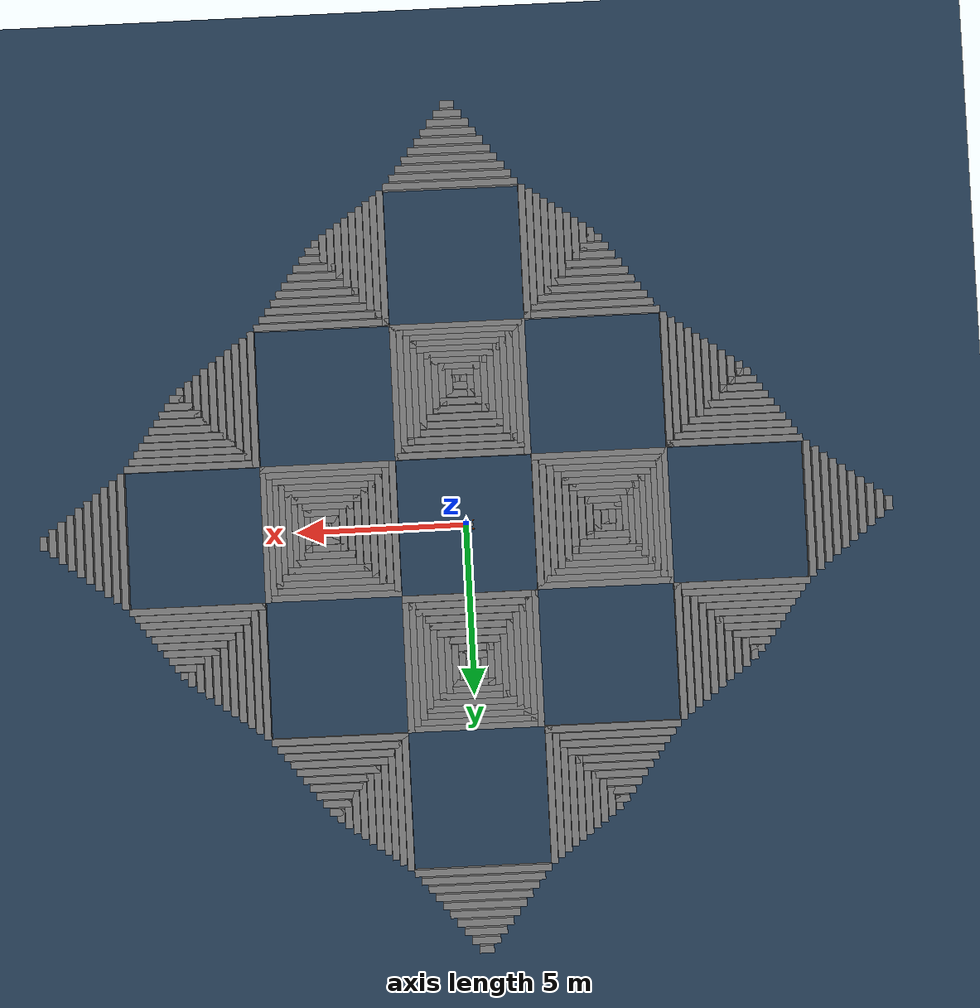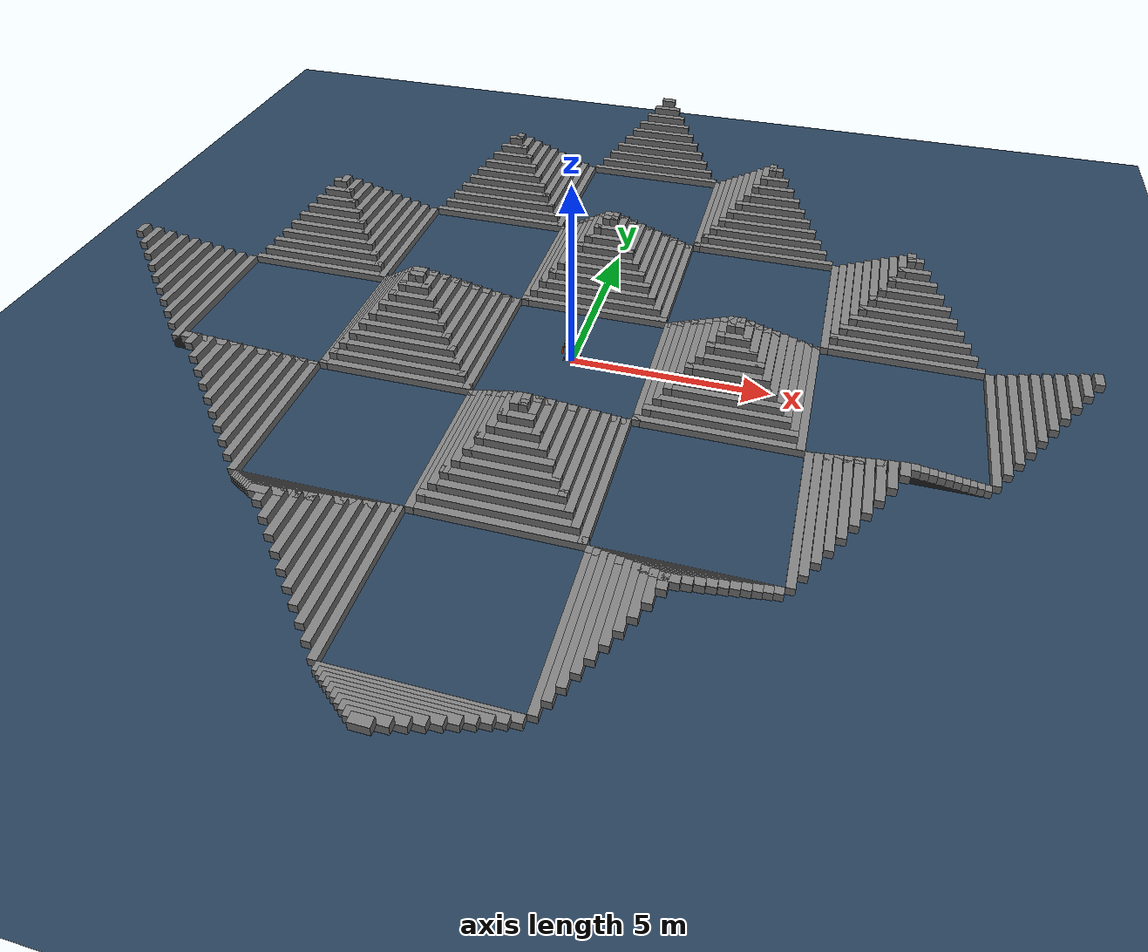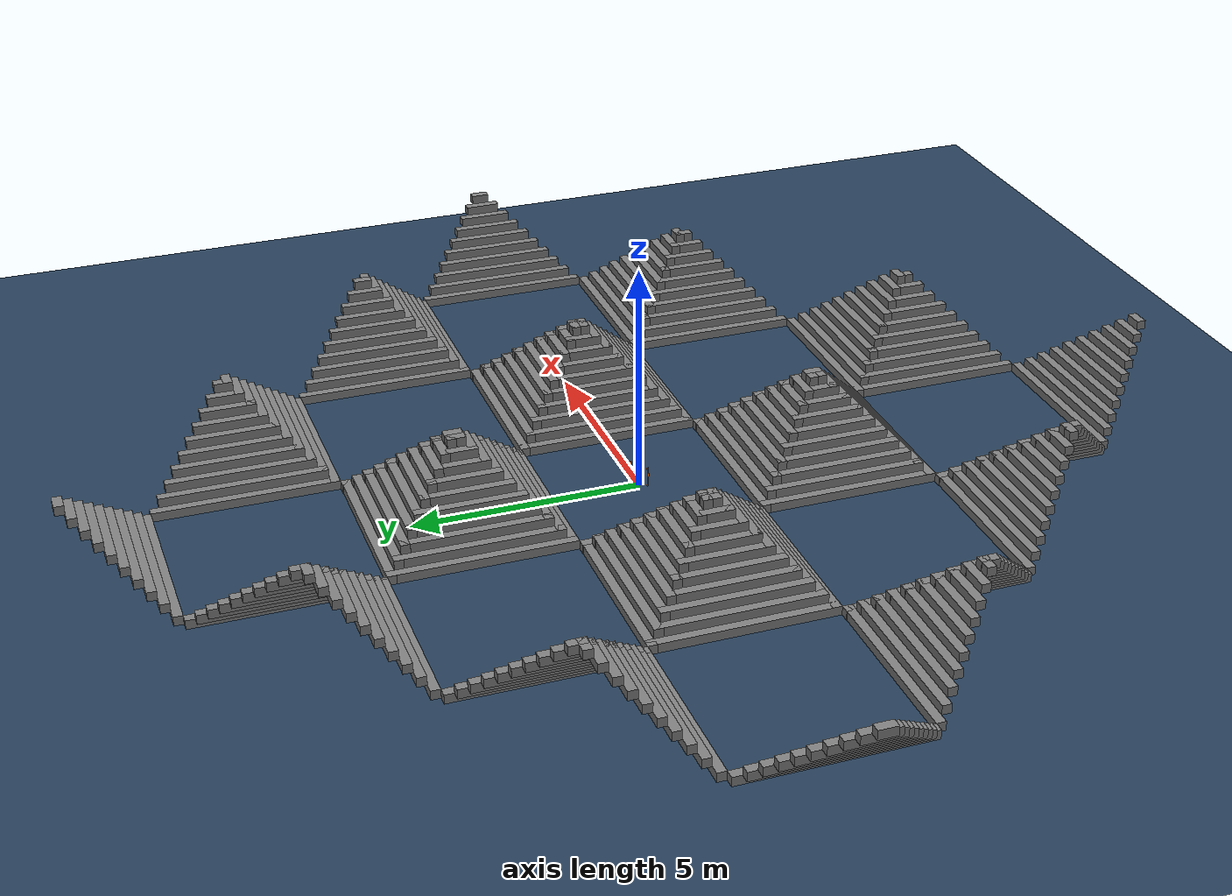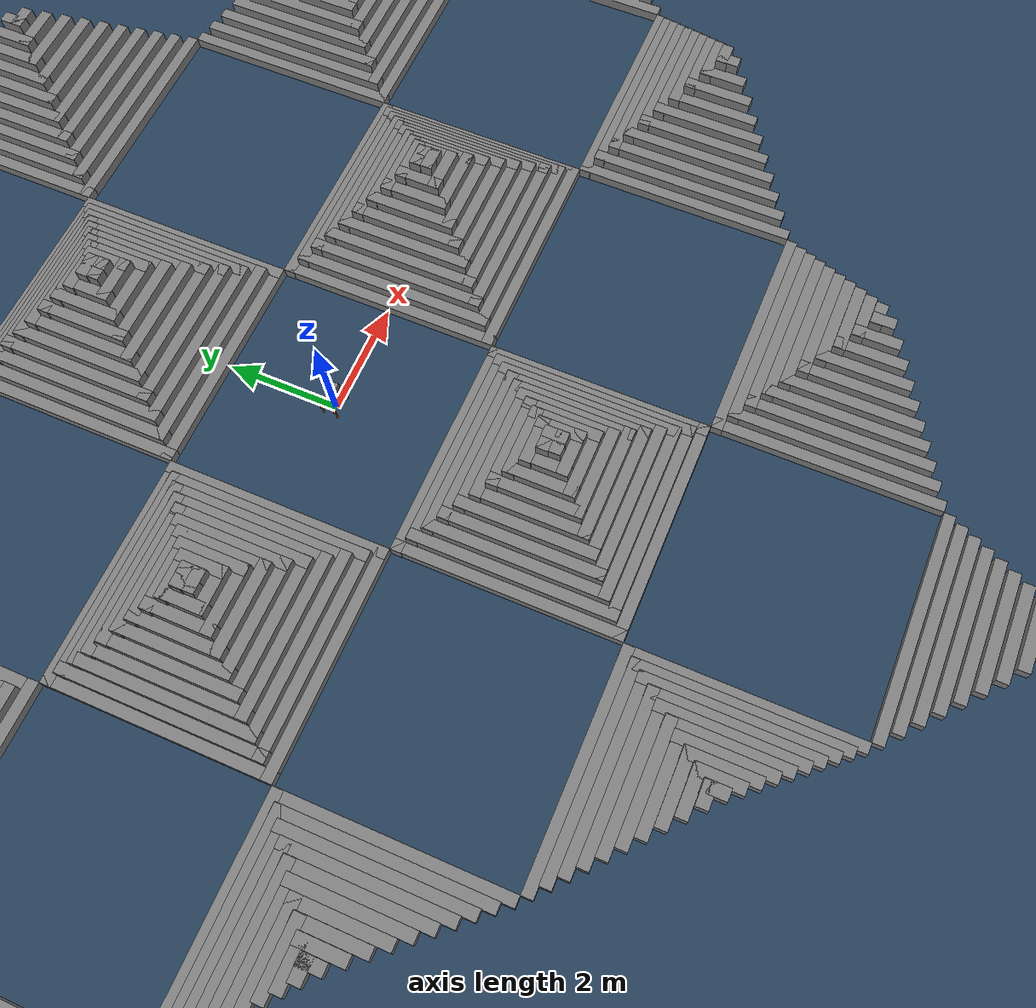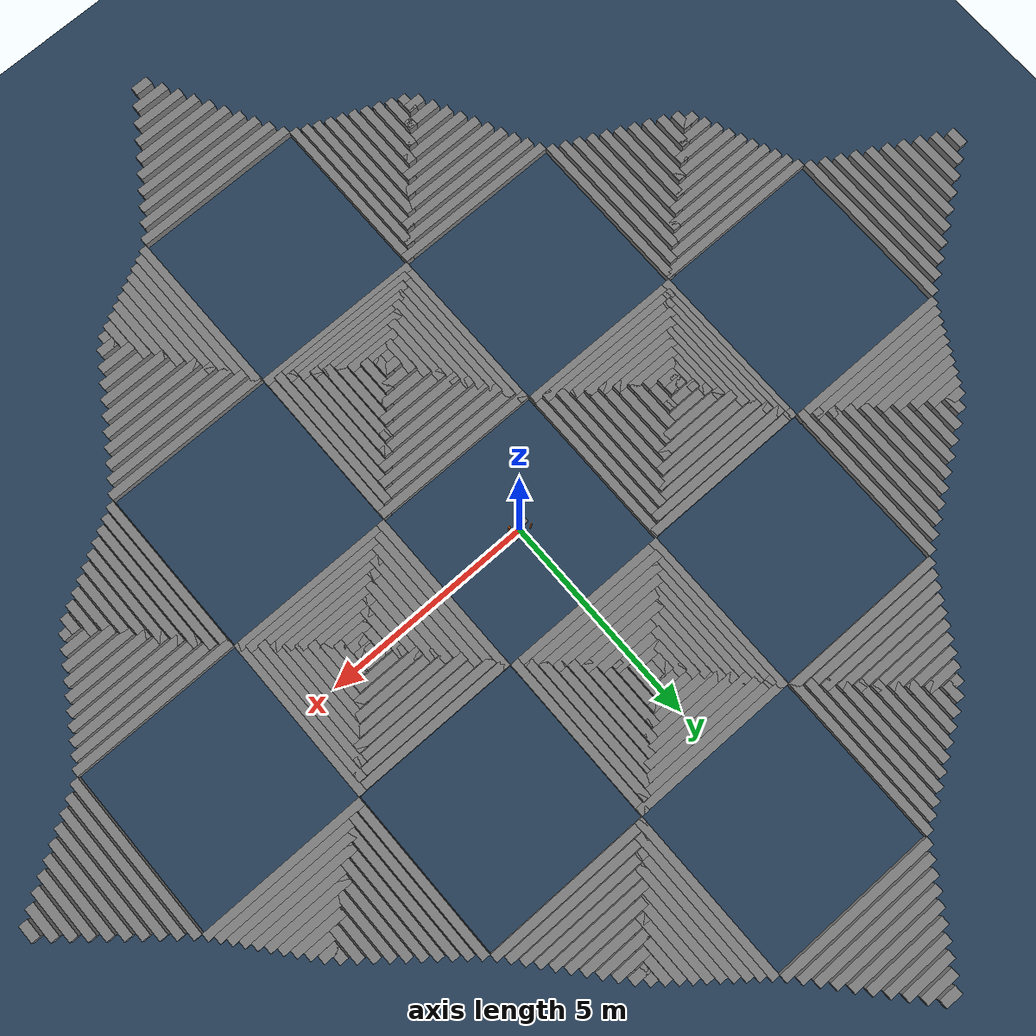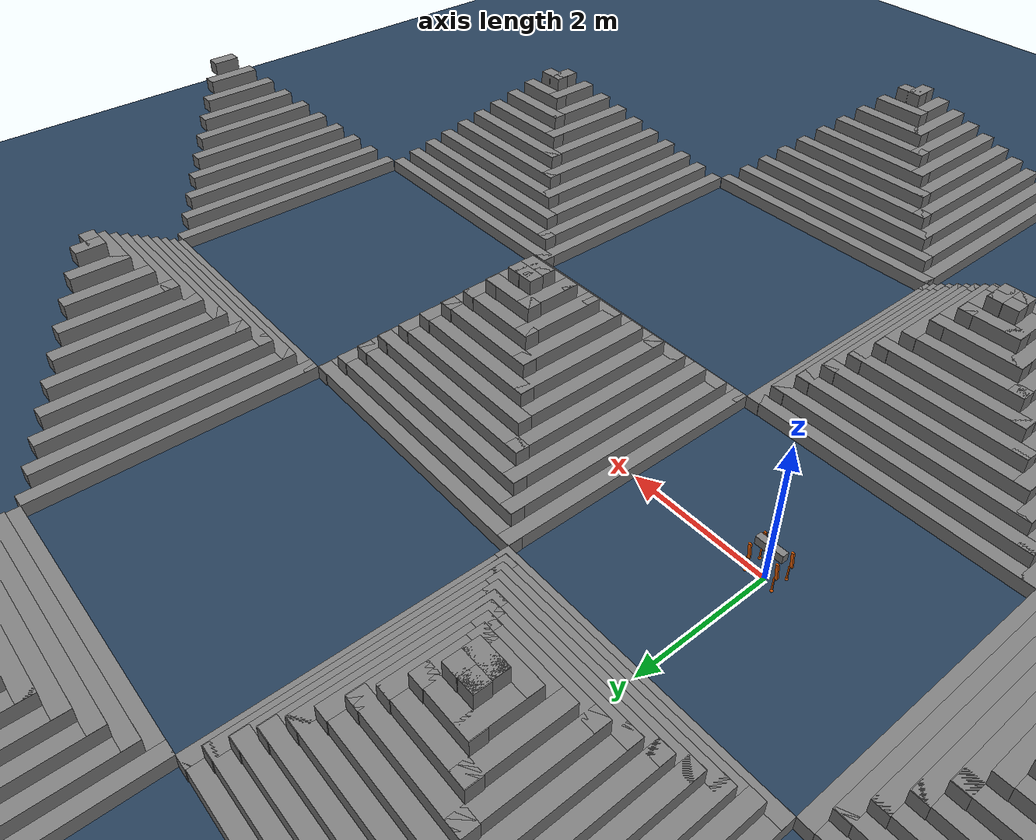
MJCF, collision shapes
<mujoco>
	<include file="go1.xml" />

	<statistic center="0 0 0.1" extent="0.8" />
	<visual>
		<headlight diffuse="0.6 0.6 0.6" ambient="0.3 0.3 0.3" specular="0 0 0" />
		<rgba haze="0.15 0.25 0.35 1" />
		<global azimuth="-130" elevation="-20" />
	</visual>
	<asset>
		<texture type="skybox" builtin="gradient" rgb1="0.3 0.5 0.7" rgb2="0 0 0" width="512" height="3072" />
		<texture type="2d" name="groundplane" builtin="checker" mark="edge" rgb1="0.2 0.3 0.4" rgb2="0.1 0.2 0.3" markrgb="0.8 0.8 0.8" width="300" height="300" />
		<material name="groundplane" texture="groundplane" texuniform="true" texrepeat="5 5" reflectance="0.2" />
	</asset>

	<worldbody>
    <light pos="0 0 1.5" dir="0 0 -1" directional="true" />
    <geom name="floor" size="0 0 0.05" type="plane" material="groundplane" />
	<geom pos="2.1 0.0 0.1" type="box" size="0.1 2.0 0.1" quat="1.0 0.0 0.0 0.0" /><geom pos="2.3000000000000003 0.0 0.30000000000000004" type="box" size="0.1 1.8 0.1" quat="1.0 0.0 0.0 0.0" /><geom pos="2.5000000000000004 0.0 0.5" type="box" size="0.1 1.6 0.1" quat="1.0 0.0 0.0 0.0" /><geom pos="2.7000000000000006 0.0 0.7" type="box" size="0.1 1.4 0.1" quat="1.0 0.0 0.0 0.0" /><geom pos="2.900000000000001 0.0 0.8999999999999999" type="box" size="0.1 1.2 0.1" quat="1.0 0.0 0.0 0.0" /><geom pos="3.100000000000001 0.0 1.0999999999999999" type="box" size="0.1 1.0 0.1" quat="1.0 0.0 0.0 0.0" /><geom pos="3.300000000000001 0.0 1.2999999999999998" type="box" size="0.1 0.8 0.1" quat="1.0 0.0 0.0 0.0" /><geom pos="3.5000000000000013 0.0 1.4999999999999998" type="box" size="0.1 0.6 0.1" quat="1.0 0.0 0.0 0.0" /><geom pos="3.7000000000000015 0.0 1.6999999999999997" type="box" size="0.1 0.4 0.1" quat="1.0 0.0 0.0 0.0" /><geom pos="3.9000000000000017 0.0 1.8999999999999997" type="box" size="0.1 0.2 0.1" quat="1.0 0.0 0.0 0.0" /><geom pos="0.001672286092539853 2.099999334156853 0.1" type="box" size="0.1 2.0 0.1" quat="0.7073882691671998 0.0 0.0 0.706825181105366" /><geom pos="0.0018315514346865058 2.29999927074322 0.30000000000000004" type="box" size="0.1 1.8 0.1" quat="0.7073882691671998 0.0 0.0 0.706825181105366" /><geom pos="0.001990816776833159 2.499999207329587 0.5" type="box" size="0.1 1.6 0.1" quat="0.7073882691671998 0.0 0.0 0.706825181105366" /><geom pos="0.0021500821189798115 2.699999143915954 0.7" type="box" size="0.1 1.4 0.1" quat="0.7073882691671998 0.0 0.0 0.706825181105366" /><geom pos="0.0023093474611264645 2.899999080502321 0.8999999999999999" type="box" size="0.1 1.2 0.1" quat="0.7073882691671998 0.0 0.0 0.706825181105366" /><geom pos="0.002468612803273117 3.099999017088688 1.0999999999999999" type="box" size="0.1 1.0 0.1" quat="0.7073882691671998 0.0 0.0 0.706825181105366" /><geom pos="0.00262787814541977 3.2999989536750554 1.2999999999999998" type="box" size="0.1 0.8 0.1" quat="0.7073882691671998 0.0 0.0 0.706825181105366" /><geom pos="0.0027871434875664227 3.4999988902614225 1.4999999999999998" type="box" size="0.1 0.6 0.1" quat="0.7073882691671998 0.0 0.0 0.706825181105366" /><geom pos="0.0029464088297130758 3.6999988268477897 1.6999999999999997" type="box" size="0.1 0.4 0.1" quat="0.7073882691671998 0.0 0.0 0.706825181105366" /><geom pos="0.0031056741718597284 3.899998763434157 1.8999999999999997" type="box" size="0.1 0.2 0.1" quat="0.7073882691671998 0.0 0.0 0.706825181105366" /><geom pos="-2.099997336627833 0.0033445711246223395 0.1" type="box" size="0.1 2.0 0.1" quat="0.0007963267107332633 0.0 0.0 0.9999996829318346" /><geom pos="-2.299997082973341 0.0036631017079197053 0.30000000000000004" type="box" size="0.1 1.8 0.1" quat="0.0007963267107332633 0.0 0.0 0.9999996829318346" /><geom pos="-2.499996829318849 0.003981632291217071 0.5" type="box" size="0.1 1.6 0.1" quat="0.0007963267107332633 0.0 0.0 0.9999996829318346" /><geom pos="-2.699996575664357 0.004300162874514437 0.7" type="box" size="0.1 1.4 0.1" quat="0.0007963267107332633 0.0 0.0 0.9999996829318346" /><geom pos="-2.8999963220098652 0.004618693457811803 0.8999999999999999" type="box" size="0.1 1.2 0.1" quat="0.0007963267107332633 0.0 0.0 0.9999996829318346" /><geom pos="-3.0999960683553733 0.004937224041109169 1.0999999999999999" type="box" size="0.1 1.0 0.1" quat="0.0007963267107332633 0.0 0.0 0.9999996829318346" /><geom pos="-3.2999958147008814 0.005255754624406535 1.2999999999999998" type="box" size="0.1 0.8 0.1" quat="0.0007963267107332633 0.0 0.0 0.9999996829318346" /><geom pos="-3.4999955610463895 0.005574285207703901 1.4999999999999998" type="box" size="0.1 0.6 0.1" quat="0.0007963267107332633 0.0 0.0 0.9999996829318346" /><geom pos="-3.6999953073918976 0.005892815791001267 1.6999999999999997" type="box" size="0.1 0.4 0.1" quat="0.0007963267107332633 0.0 0.0 0.9999996829318346" /><geom pos="-3.8999950537374057 0.006211346374298632 1.8999999999999997" type="box" size="0.1 0.2 0.1" quat="0.0007963267107332633 0.0 0.0 0.9999996829318346" /><geom pos="-0.005016854035791231 -2.0999940074142076 0.1" type="box" size="0.1 2.0 0.1" quat="-0.7062616448200052 -0.0 0.0 0.7079509086484321" /><geom pos="-0.00549464965824754 -2.2999934366917514 0.30000000000000004" type="box" size="0.1 1.8 0.1" quat="-0.7062616448200052 -0.0 0.0 0.7079509086484321" /><geom pos="-0.005972445280703847 -2.499992865969295 0.5" type="box" size="0.1 1.6 0.1" quat="-0.7062616448200052 -0.0 0.0 0.7079509086484321" /><geom pos="-0.0064502409031601555 -2.699992295246839 0.7" type="box" size="0.1 1.4 0.1" quat="-0.7062616448200052 -0.0 0.0 0.7079509086484321" /><geom pos="-0.006928036525616464 -2.8999917245243827 0.8999999999999999" type="box" size="0.1 1.2 0.1" quat="-0.7062616448200052 -0.0 0.0 0.7079509086484321" /><geom pos="-0.007405832148072772 -3.0999911538019265 1.0999999999999999" type="box" size="0.1 1.0 0.1" quat="-0.7062616448200052 -0.0 0.0 0.7079509086484321" /><geom pos="-0.00788362777052908 -3.2999905830794702 1.2999999999999998" type="box" size="0.1 0.8 0.1" quat="-0.7062616448200052 -0.0 0.0 0.7079509086484321" /><geom pos="-0.008361423392985389 -3.499990012357014 1.4999999999999998" type="box" size="0.1 0.6 0.1" quat="-0.7062616448200052 -0.0 0.0 0.7079509086484321" /><geom pos="-0.008839219015441697 -3.699989441634558 1.6999999999999997" type="box" size="0.1 0.4 0.1" quat="-0.7062616448200052 -0.0 0.0 0.7079509086484321" /><geom pos="-0.009317014637898004 -3.8999888709121016 1.8999999999999997" type="box" size="0.1 0.2 0.1" quat="-0.7062616448200052 -0.0 0.0 0.7079509086484321" /><geom pos="6.1 4.0 0.1" type="box" size="0.1 2.0 0.1" quat="1.0 0.0 0.0 0.0" /><geom pos="6.300000000000001 4.0 0.30000000000000004" type="box" size="0.1 1.8 0.1" quat="1.0 0.0 0.0 0.0" /><geom pos="6.5 4.0 0.5" type="box" size="0.1 1.6 0.1" quat="1.0 0.0 0.0 0.0" /><geom pos="6.700000000000001 4.0 0.7" type="box" size="0.1 1.4 0.1" quat="1.0 0.0 0.0 0.0" /><geom pos="6.9 4.0 0.8999999999999999" type="box" size="0.1 1.2 0.1" quat="1.0 0.0 0.0 0.0" /><geom pos="7.100000000000001 4.0 1.0999999999999999" type="box" size="0.1 1.0 0.1" quat="1.0 0.0 0.0 0.0" /><geom pos="7.300000000000001 4.0 1.2999999999999998" type="box" size="0.1 0.8 0.1" quat="1.0 0.0 0.0 0.0" /><geom pos="7.500000000000002 4.0 1.4999999999999998" type="box" size="0.1 0.6 0.1" quat="1.0 0.0 0.0 0.0" /><geom pos="7.700000000000001 4.0 1.6999999999999997" type="box" size="0.1 0.4 0.1" quat="1.0 0.0 0.0 0.0" /><geom pos="7.900000000000002 4.0 1.8999999999999997" type="box" size="0.1 0.2 0.1" quat="1.0 0.0 0.0 0.0" /><geom pos="4.00167228609254 6.099999334156853 0.1" type="box" size="0.1 2.0 0.1" quat="0.7073882691671998 0.0 0.0 0.706825181105366" /><geom pos="4.0018315514346865 6.2999992707432195 0.30000000000000004" type="box" size="0.1 1.8 0.1" quat="0.7073882691671998 0.0 0.0 0.706825181105366" /><geom pos="4.001990816776833 6.499999207329587 0.5" type="box" size="0.1 1.6 0.1" quat="0.7073882691671998 0.0 0.0 0.706825181105366" /><geom pos="4.0021500821189795 6.699999143915954 0.7" type="box" size="0.1 1.4 0.1" quat="0.7073882691671998 0.0 0.0 0.706825181105366" /><geom pos="4.002309347461127 6.899999080502321 0.8999999999999999" type="box" size="0.1 1.2 0.1" quat="0.7073882691671998 0.0 0.0 0.706825181105366" /><geom pos="4.002468612803273 7.099999017088688 1.0999999999999999" type="box" size="0.1 1.0 0.1" quat="0.7073882691671998 0.0 0.0 0.706825181105366" /><geom pos="4.00262787814542 7.299998953675056 1.2999999999999998" type="box" size="0.1 0.8 0.1" quat="0.7073882691671998 0.0 0.0 0.706825181105366" /><geom pos="4.002787143487566 7.4999988902614225 1.4999999999999998" type="box" size="0.1 0.6 0.1" quat="0.7073882691671998 0.0 0.0 0.706825181105366" /><geom pos="4.002946408829713 7.699998826847789 1.6999999999999997" type="box" size="0.1 0.4 0.1" quat="0.7073882691671998 0.0 0.0 0.706825181105366" /><geom pos="4.003105674171859 7.899998763434157 1.8999999999999997" type="box" size="0.1 0.2 0.1" quat="0.7073882691671998 0.0 0.0 0.706825181105366" /><geom pos="1.9000026633721672 4.0033445711246225 0.1" type="box" size="0.1 2.0 0.1" quat="0.0007963267107332633 0.0 0.0 0.9999996829318346" /><geom pos="1.700002917026659 4.00366310170792 0.30000000000000004" type="box" size="0.1 1.8 0.1" quat="0.0007963267107332633 0.0 0.0 0.9999996829318346" /><geom pos="1.500003170681151 4.003981632291217 0.5" type="box" size="0.1 1.6 0.1" quat="0.0007963267107332633 0.0 0.0 0.9999996829318346" /><geom pos="1.3000034243356429 4.0043001628745145 0.7" type="box" size="0.1 1.4 0.1" quat="0.0007963267107332633 0.0 0.0 0.9999996829318346" /><geom pos="1.1000036779901348 4.004618693457812 0.8999999999999999" type="box" size="0.1 1.2 0.1" quat="0.0007963267107332633 0.0 0.0 0.9999996829318346" /><geom pos="0.9000039316446267 4.004937224041109 1.0999999999999999" type="box" size="0.1 1.0 0.1" quat="0.0007963267107332633 0.0 0.0 0.9999996829318346" /><geom pos="0.7000041852991186 4.0052557546244065 1.2999999999999998" type="box" size="0.1 0.8 0.1" quat="0.0007963267107332633 0.0 0.0 0.9999996829318346" /><geom pos="0.5000044389536105 4.005574285207704 1.4999999999999998" type="box" size="0.1 0.6 0.1" quat="0.0007963267107332633 0.0 0.0 0.9999996829318346" /><geom pos="0.30000469260810236 4.005892815791001 1.6999999999999997" type="box" size="0.1 0.4 0.1" quat="0.0007963267107332633 0.0 0.0 0.9999996829318346" /><geom pos="0.10000494626259426 4.0062113463742985 1.8999999999999997" type="box" size="0.1 0.2 0.1" quat="0.0007963267107332633 0.0 0.0 0.9999996829318346" /><geom pos="3.9949831459642087 1.9000059925857924 0.1" type="box" size="0.1 2.0 0.1" quat="-0.7062616448200052 -0.0 0.0 0.7079509086484321" /><geom pos="3.9945053503417522 1.7000065633082486 0.30000000000000004" type="box" size="0.1 1.8 0.1" quat="-0.7062616448200052 -0.0 0.0 0.7079509086484321" /><geom pos="3.9940275547192963 1.5000071340307048 0.5" type="box" size="0.1 1.6 0.1" quat="-0.7062616448200052 -0.0 0.0 0.7079509086484321" /><geom pos="3.99354975909684 1.300007704753161 0.7" type="box" size="0.1 1.4 0.1" quat="-0.7062616448200052 -0.0 0.0 0.7079509086484321" /><geom pos="3.9930719634743834 1.1000082754756173 0.8999999999999999" type="box" size="0.1 1.2 0.1" quat="-0.7062616448200052 -0.0 0.0 0.7079509086484321" /><geom pos="3.9925941678519274 0.9000088461980735 1.0999999999999999" type="box" size="0.1 1.0 0.1" quat="-0.7062616448200052 -0.0 0.0 0.7079509086484321" /><geom pos="3.992116372229471 0.7000094169205298 1.2999999999999998" type="box" size="0.1 0.8 0.1" quat="-0.7062616448200052 -0.0 0.0 0.7079509086484321" /><geom pos="3.9916385766070146 0.500009987642986 1.4999999999999998" type="box" size="0.1 0.6 0.1" quat="-0.7062616448200052 -0.0 0.0 0.7079509086484321" /><geom pos="3.991160780984558 0.3000105583654422 1.6999999999999997" type="box" size="0.1 0.4 0.1" quat="-0.7062616448200052 -0.0 0.0 0.7079509086484321" /><geom pos="3.990682985362102 0.10001112908789844 1.8999999999999997" type="box" size="0.1 0.2 0.1" quat="-0.7062616448200052 -0.0 0.0 0.7079509086484321" /><geom pos="6.1 -4.0 0.1" type="box" size="0.1 2.0 0.1" quat="1.0 0.0 0.0 0.0" /><geom pos="6.300000000000001 -4.0 0.30000000000000004" type="box" size="0.1 1.8 0.1" quat="1.0 0.0 0.0 0.0" /><geom pos="6.5 -4.0 0.5" type="box" size="0.1 1.6 0.1" quat="1.0 0.0 0.0 0.0" /><geom pos="6.700000000000001 -4.0 0.7" type="box" size="0.1 1.4 0.1" quat="1.0 0.0 0.0 0.0" /><geom pos="6.9 -4.0 0.8999999999999999" type="box" size="0.1 1.2 0.1" quat="1.0 0.0 0.0 0.0" /><geom pos="7.100000000000001 -4.0 1.0999999999999999" type="box" size="0.1 1.0 0.1" quat="1.0 0.0 0.0 0.0" /><geom pos="7.300000000000001 -4.0 1.2999999999999998" type="box" size="0.1 0.8 0.1" quat="1.0 0.0 0.0 0.0" /><geom pos="7.500000000000002 -4.0 1.4999999999999998" type="box" size="0.1 0.6 0.1" quat="1.0 0.0 0.0 0.0" /><geom pos="7.700000000000001 -4.0 1.6999999999999997" type="box" size="0.1 0.4 0.1" quat="1.0 0.0 0.0 0.0" /><geom pos="7.900000000000002 -4.0 1.8999999999999997" type="box" size="0.1 0.2 0.1" quat="1.0 0.0 0.0 0.0" /><geom pos="4.00167228609254 -1.9000006658431472 0.1" type="box" size="0.1 2.0 0.1" quat="0.7073882691671998 0.0 0.0 0.706825181105366" /><geom pos="4.0018315514346865 -1.70000072925678 0.30000000000000004" type="box" size="0.1 1.8 0.1" quat="0.7073882691671998 0.0 0.0 0.706825181105366" /><geom pos="4.001990816776833 -1.5000007926704129 0.5" type="box" size="0.1 1.6 0.1" quat="0.7073882691671998 0.0 0.0 0.706825181105366" /><geom pos="4.0021500821189795 -1.3000008560840461 0.7" type="box" size="0.1 1.4 0.1" quat="0.7073882691671998 0.0 0.0 0.706825181105366" /><geom pos="4.002309347461127 -1.100000919497679 0.8999999999999999" type="box" size="0.1 1.2 0.1" quat="0.7073882691671998 0.0 0.0 0.706825181105366" /><geom pos="4.002468612803273 -0.9000009829113118 1.0999999999999999" type="box" size="0.1 1.0 0.1" quat="0.7073882691671998 0.0 0.0 0.706825181105366" /><geom pos="4.00262787814542 -0.7000010463249446 1.2999999999999998" type="box" size="0.1 0.8 0.1" quat="0.7073882691671998 0.0 0.0 0.706825181105366" /><geom pos="4.002787143487566 -0.5000011097385775 1.4999999999999998" type="box" size="0.1 0.6 0.1" quat="0.7073882691671998 0.0 0.0 0.706825181105366" /><geom pos="4.002946408829713 -0.3000011731522103 1.6999999999999997" type="box" size="0.1 0.4 0.1" quat="0.7073882691671998 0.0 0.0 0.706825181105366" /><geom pos="4.003105674171859 -0.10000123656584314 1.8999999999999997" type="box" size="0.1 0.2 0.1" quat="0.7073882691671998 0.0 0.0 0.706825181105366" /><geom pos="1.9000026633721672 -3.9966554288753775 0.1" type="box" size="0.1 2.0 0.1" quat="0.0007963267107332633 0.0 0.0 0.9999996829318346" /><geom pos="1.700002917026659 -3.99633689829208 0.30000000000000004" type="box" size="0.1 1.8 0.1" quat="0.0007963267107332633 0.0 0.0 0.9999996829318346" /><geom pos="1.500003170681151 -3.996018367708783 0.5" type="box" size="0.1 1.6 0.1" quat="0.0007963267107332633 0.0 0.0 0.9999996829318346" /><geom pos="1.3000034243356429 -3.9956998371254855 0.7" type="box" size="0.1 1.4 0.1" quat="0.0007963267107332633 0.0 0.0 0.9999996829318346" /><geom pos="1.1000036779901348 -3.995381306542188 0.8999999999999999" type="box" size="0.1 1.2 0.1" quat="0.0007963267107332633 0.0 0.0 0.9999996829318346" /><geom pos="0.9000039316446267 -3.995062775958891 1.0999999999999999" type="box" size="0.1 1.0 0.1" quat="0.0007963267107332633 0.0 0.0 0.9999996829318346" /><geom pos="0.7000041852991186 -3.9947442453755935 1.2999999999999998" type="box" size="0.1 0.8 0.1" quat="0.0007963267107332633 0.0 0.0 0.9999996829318346" /><geom pos="0.5000044389536105 -3.994425714792296 1.4999999999999998" type="box" size="0.1 0.6 0.1" quat="0.0007963267107332633 0.0 0.0 0.9999996829318346" /><geom pos="0.30000469260810236 -3.994107184208999 1.6999999999999997" type="box" size="0.1 0.4 0.1" quat="0.0007963267107332633 0.0 0.0 0.9999996829318346" /><geom pos="0.10000494626259426 -3.9937886536257015 1.8999999999999997" type="box" size="0.1 0.2 0.1" quat="0.0007963267107332633 0.0 0.0 0.9999996829318346" /><geom pos="3.9949831459642087 -6.099994007414208 0.1" type="box" size="0.1 2.0 0.1" quat="-0.7062616448200052 -0.0 0.0 0.7079509086484321" /><geom pos="3.9945053503417522 -6.299993436691752 0.30000000000000004" type="box" size="0.1 1.8 0.1" quat="-0.7062616448200052 -0.0 0.0 0.7079509086484321" /><geom pos="3.9940275547192963 -6.499992865969295 0.5" type="box" size="0.1 1.6 0.1" quat="-0.7062616448200052 -0.0 0.0 0.7079509086484321" /><geom pos="3.99354975909684 -6.6999922952468385 0.7" type="box" size="0.1 1.4 0.1" quat="-0.7062616448200052 -0.0 0.0 0.7079509086484321" /><geom pos="3.9930719634743834 -6.899991724524383 0.8999999999999999" type="box" size="0.1 1.2 0.1" quat="-0.7062616448200052 -0.0 0.0 0.7079509086484321" /><geom pos="3.9925941678519274 -7.099991153801927 1.0999999999999999" type="box" size="0.1 1.0 0.1" quat="-0.7062616448200052 -0.0 0.0 0.7079509086484321" /><geom pos="3.992116372229471 -7.29999058307947 1.2999999999999998" type="box" size="0.1 0.8 0.1" quat="-0.7062616448200052 -0.0 0.0 0.7079509086484321" /><geom pos="3.9916385766070146 -7.499990012357014 1.4999999999999998" type="box" size="0.1 0.6 0.1" quat="-0.7062616448200052 -0.0 0.0 0.7079509086484321" /><geom pos="3.991160780984558 -7.699989441634558 1.6999999999999997" type="box" size="0.1 0.4 0.1" quat="-0.7062616448200052 -0.0 0.0 0.7079509086484321" /><geom pos="3.990682985362102 -7.899988870912102 1.8999999999999997" type="box" size="0.1 0.2 0.1" quat="-0.7062616448200052 -0.0 0.0 0.7079509086484321" /><geom pos="-1.9 4.0 0.1" type="box" size="0.1 2.0 0.1" quat="1.0 0.0 0.0 0.0" /><geom pos="-1.6999999999999997 4.0 0.30000000000000004" type="box" size="0.1 1.8 0.1" quat="1.0 0.0 0.0 0.0" /><geom pos="-1.4999999999999996 4.0 0.5" type="box" size="0.1 1.6 0.1" quat="1.0 0.0 0.0 0.0" /><geom pos="-1.2999999999999994 4.0 0.7" type="box" size="0.1 1.4 0.1" quat="1.0 0.0 0.0 0.0" /><geom pos="-1.0999999999999992 4.0 0.8999999999999999" type="box" size="0.1 1.2 0.1" quat="1.0 0.0 0.0 0.0" /><geom pos="-0.899999999999999 4.0 1.0999999999999999" type="box" size="0.1 1.0 0.1" quat="1.0 0.0 0.0 0.0" /><geom pos="-0.6999999999999988 4.0 1.2999999999999998" type="box" size="0.1 0.8 0.1" quat="1.0 0.0 0.0 0.0" /><geom pos="-0.49999999999999867 4.0 1.4999999999999998" type="box" size="0.1 0.6 0.1" quat="1.0 0.0 0.0 0.0" /><geom pos="-0.2999999999999985 4.0 1.6999999999999997" type="box" size="0.1 0.4 0.1" quat="1.0 0.0 0.0 0.0" /><geom pos="-0.09999999999999831 4.0 1.8999999999999997" type="box" size="0.1 0.2 0.1" quat="1.0 0.0 0.0 0.0" /><geom pos="-3.99832771390746 6.099999334156853 0.1" type="box" size="0.1 2.0 0.1" quat="0.7073882691671998 0.0 0.0 0.706825181105366" /><geom pos="-3.9981684485653135 6.2999992707432195 0.30000000000000004" type="box" size="0.1 1.8 0.1" quat="0.7073882691671998 0.0 0.0 0.706825181105366" /><geom pos="-3.998009183223167 6.499999207329587 0.5" type="box" size="0.1 1.6 0.1" quat="0.7073882691671998 0.0 0.0 0.706825181105366" /><geom pos="-3.99784991788102 6.699999143915954 0.7" type="box" size="0.1 1.4 0.1" quat="0.7073882691671998 0.0 0.0 0.706825181105366" /><geom pos="-3.9976906525388736 6.899999080502321 0.8999999999999999" type="box" size="0.1 1.2 0.1" quat="0.7073882691671998 0.0 0.0 0.706825181105366" /><geom pos="-3.997531387196727 7.099999017088688 1.0999999999999999" type="box" size="0.1 1.0 0.1" quat="0.7073882691671998 0.0 0.0 0.706825181105366" /><geom pos="-3.99737212185458 7.299998953675056 1.2999999999999998" type="box" size="0.1 0.8 0.1" quat="0.7073882691671998 0.0 0.0 0.706825181105366" /><geom pos="-3.9972128565124336 7.4999988902614225 1.4999999999999998" type="box" size="0.1 0.6 0.1" quat="0.7073882691671998 0.0 0.0 0.706825181105366" /><geom pos="-3.997053591170287 7.699998826847789 1.6999999999999997" type="box" size="0.1 0.4 0.1" quat="0.7073882691671998 0.0 0.0 0.706825181105366" /><geom pos="-3.99689432582814 7.899998763434157 1.8999999999999997" type="box" size="0.1 0.2 0.1" quat="0.7073882691671998 0.0 0.0 0.706825181105366" /><geom pos="-6.099997336627833 4.0033445711246225 0.1" type="box" size="0.1 2.0 0.1" quat="0.0007963267107332633 0.0 0.0 0.9999996829318346" /><geom pos="-6.299997082973341 4.00366310170792 0.30000000000000004" type="box" size="0.1 1.8 0.1" quat="0.0007963267107332633 0.0 0.0 0.9999996829318346" /><geom pos="-6.4999968293188495 4.003981632291217 0.5" type="box" size="0.1 1.6 0.1" quat="0.0007963267107332633 0.0 0.0 0.9999996829318346" /><geom pos="-6.699996575664358 4.0043001628745145 0.7" type="box" size="0.1 1.4 0.1" quat="0.0007963267107332633 0.0 0.0 0.9999996829318346" /><geom pos="-6.899996322009866 4.004618693457812 0.8999999999999999" type="box" size="0.1 1.2 0.1" quat="0.0007963267107332633 0.0 0.0 0.9999996829318346" /><geom pos="-7.099996068355374 4.004937224041109 1.0999999999999999" type="box" size="0.1 1.0 0.1" quat="0.0007963267107332633 0.0 0.0 0.9999996829318346" /><geom pos="-7.299995814700882 4.0052557546244065 1.2999999999999998" type="box" size="0.1 0.8 0.1" quat="0.0007963267107332633 0.0 0.0 0.9999996829318346" /><geom pos="-7.49999556104639 4.005574285207704 1.4999999999999998" type="box" size="0.1 0.6 0.1" quat="0.0007963267107332633 0.0 0.0 0.9999996829318346" /><geom pos="-7.699995307391898 4.005892815791001 1.6999999999999997" type="box" size="0.1 0.4 0.1" quat="0.0007963267107332633 0.0 0.0 0.9999996829318346" /><geom pos="-7.899995053737406 4.0062113463742985 1.8999999999999997" type="box" size="0.1 0.2 0.1" quat="0.0007963267107332633 0.0 0.0 0.9999996829318346" /><geom pos="-4.005016854035791 1.9000059925857924 0.1" type="box" size="0.1 2.0 0.1" quat="-0.7062616448200052 -0.0 0.0 0.7079509086484321" /><geom pos="-4.005494649658248 1.7000065633082486 0.30000000000000004" type="box" size="0.1 1.8 0.1" quat="-0.7062616448200052 -0.0 0.0 0.7079509086484321" /><geom pos="-4.005972445280704 1.5000071340307048 0.5" type="box" size="0.1 1.6 0.1" quat="-0.7062616448200052 -0.0 0.0 0.7079509086484321" /><geom pos="-4.006450240903161 1.300007704753161 0.7" type="box" size="0.1 1.4 0.1" quat="-0.7062616448200052 -0.0 0.0 0.7079509086484321" /><geom pos="-4.006928036525617 1.1000082754756173 0.8999999999999999" type="box" size="0.1 1.2 0.1" quat="-0.7062616448200052 -0.0 0.0 0.7079509086484321" /><geom pos="-4.0074058321480726 0.9000088461980735 1.0999999999999999" type="box" size="0.1 1.0 0.1" quat="-0.7062616448200052 -0.0 0.0 0.7079509086484321" /><geom pos="-4.007883627770529 0.7000094169205298 1.2999999999999998" type="box" size="0.1 0.8 0.1" quat="-0.7062616448200052 -0.0 0.0 0.7079509086484321" /><geom pos="-4.008361423392985 0.500009987642986 1.4999999999999998" type="box" size="0.1 0.6 0.1" quat="-0.7062616448200052 -0.0 0.0 0.7079509086484321" /><geom pos="-4.008839219015441 0.3000105583654422 1.6999999999999997" type="box" size="0.1 0.4 0.1" quat="-0.7062616448200052 -0.0 0.0 0.7079509086484321" /><geom pos="-4.009317014637898 0.10001112908789844 1.8999999999999997" type="box" size="0.1 0.2 0.1" quat="-0.7062616448200052 -0.0 0.0 0.7079509086484321" /><geom pos="-1.9 -4.0 0.1" type="box" size="0.1 2.0 0.1" quat="1.0 0.0 0.0 0.0" /><geom pos="-1.6999999999999997 -4.0 0.30000000000000004" type="box" size="0.1 1.8 0.1" quat="1.0 0.0 0.0 0.0" /><geom pos="-1.4999999999999996 -4.0 0.5" type="box" size="0.1 1.6 0.1" quat="1.0 0.0 0.0 0.0" /><geom pos="-1.2999999999999994 -4.0 0.7" type="box" size="0.1 1.4 0.1" quat="1.0 0.0 0.0 0.0" /><geom pos="-1.0999999999999992 -4.0 0.8999999999999999" type="box" size="0.1 1.2 0.1" quat="1.0 0.0 0.0 0.0" /><geom pos="-0.899999999999999 -4.0 1.0999999999999999" type="box" size="0.1 1.0 0.1" quat="1.0 0.0 0.0 0.0" /><geom pos="-0.6999999999999988 -4.0 1.2999999999999998" type="box" size="0.1 0.8 0.1" quat="1.0 0.0 0.0 0.0" /><geom pos="-0.49999999999999867 -4.0 1.4999999999999998" type="box" size="0.1 0.6 0.1" quat="1.0 0.0 0.0 0.0" /><geom pos="-0.2999999999999985 -4.0 1.6999999999999997" type="box" size="0.1 0.4 0.1" quat="1.0 0.0 0.0 0.0" /><geom pos="-0.09999999999999831 -4.0 1.8999999999999997" type="box" size="0.1 0.2 0.1" quat="1.0 0.0 0.0 0.0" /><geom pos="-3.99832771390746 -1.9000006658431472 0.1" type="box" size="0.1 2.0 0.1" quat="0.7073882691671998 0.0 0.0 0.706825181105366" /><geom pos="-3.9981684485653135 -1.70000072925678 0.30000000000000004" type="box" size="0.1 1.8 0.1" quat="0.7073882691671998 0.0 0.0 0.706825181105366" /><geom pos="-3.998009183223167 -1.5000007926704129 0.5" type="box" size="0.1 1.6 0.1" quat="0.7073882691671998 0.0 0.0 0.706825181105366" /><geom pos="-3.99784991788102 -1.3000008560840461 0.7" type="box" size="0.1 1.4 0.1" quat="0.7073882691671998 0.0 0.0 0.706825181105366" /><geom pos="-3.9976906525388736 -1.100000919497679 0.8999999999999999" type="box" size="0.1 1.2 0.1" quat="0.7073882691671998 0.0 0.0 0.706825181105366" /><geom pos="-3.997531387196727 -0.9000009829113118 1.0999999999999999" type="box" size="0.1 1.0 0.1" quat="0.7073882691671998 0.0 0.0 0.706825181105366" /><geom pos="-3.99737212185458 -0.7000010463249446 1.2999999999999998" type="box" size="0.1 0.8 0.1" quat="0.7073882691671998 0.0 0.0 0.706825181105366" /><geom pos="-3.9972128565124336 -0.5000011097385775 1.4999999999999998" type="box" size="0.1 0.6 0.1" quat="0.7073882691671998 0.0 0.0 0.706825181105366" /><geom pos="-3.997053591170287 -0.3000011731522103 1.6999999999999997" type="box" size="0.1 0.4 0.1" quat="0.7073882691671998 0.0 0.0 0.706825181105366" /><geom pos="-3.99689432582814 -0.10000123656584314 1.8999999999999997" type="box" size="0.1 0.2 0.1" quat="0.7073882691671998 0.0 0.0 0.706825181105366" /><geom pos="-6.099997336627833 -3.9966554288753775 0.1" type="box" size="0.1 2.0 0.1" quat="0.0007963267107332633 0.0 0.0 0.9999996829318346" /><geom pos="-6.299997082973341 -3.99633689829208 0.30000000000000004" type="box" size="0.1 1.8 0.1" quat="0.0007963267107332633 0.0 0.0 0.9999996829318346" /><geom pos="-6.4999968293188495 -3.996018367708783 0.5" type="box" size="0.1 1.6 0.1" quat="0.0007963267107332633 0.0 0.0 0.9999996829318346" /><geom pos="-6.699996575664358 -3.9956998371254855 0.7" type="box" size="0.1 1.4 0.1" quat="0.0007963267107332633 0.0 0.0 0.9999996829318346" /><geom pos="-6.899996322009866 -3.995381306542188 0.8999999999999999" type="box" size="0.1 1.2 0.1" quat="0.0007963267107332633 0.0 0.0 0.9999996829318346" /><geom pos="-7.099996068355374 -3.995062775958891 1.0999999999999999" type="box" size="0.1 1.0 0.1" quat="0.0007963267107332633 0.0 0.0 0.9999996829318346" /><geom pos="-7.299995814700882 -3.9947442453755935 1.2999999999999998" type="box" size="0.1 0.8 0.1" quat="0.0007963267107332633 0.0 0.0 0.9999996829318346" /><geom pos="-7.49999556104639 -3.994425714792296 1.4999999999999998" type="box" size="0.1 0.6 0.1" quat="0.0007963267107332633 0.0 0.0 0.9999996829318346" /><geom pos="-7.699995307391898 -3.994107184208999 1.6999999999999997" type="box" size="0.1 0.4 0.1" quat="0.0007963267107332633 0.0 0.0 0.9999996829318346" /><geom pos="-7.899995053737406 -3.9937886536257015 1.8999999999999997" type="box" size="0.1 0.2 0.1" quat="0.0007963267107332633 0.0 0.0 0.9999996829318346" /><geom pos="-4.005016854035791 -6.099994007414208 0.1" type="box" size="0.1 2.0 0.1" quat="-0.7062616448200052 -0.0 0.0 0.7079509086484321" /><geom pos="-4.005494649658248 -6.299993436691752 0.30000000000000004" type="box" size="0.1 1.8 0.1" quat="-0.7062616448200052 -0.0 0.0 0.7079509086484321" /><geom pos="-4.005972445280704 -6.499992865969295 0.5" type="box" size="0.1 1.6 0.1" quat="-0.7062616448200052 -0.0 0.0 0.7079509086484321" /><geom pos="-4.006450240903161 -6.6999922952468385 0.7" type="box" size="0.1 1.4 0.1" quat="-0.7062616448200052 -0.0 0.0 0.7079509086484321" /><geom pos="-4.006928036525617 -6.899991724524383 0.8999999999999999" type="box" size="0.1 1.2 0.1" quat="-0.7062616448200052 -0.0 0.0 0.7079509086484321" /><geom pos="-4.0074058321480726 -7.099991153801927 1.0999999999999999" type="box" size="0.1 1.0 0.1" quat="-0.7062616448200052 -0.0 0.0 0.7079509086484321" /><geom pos="-4.007883627770529 -7.29999058307947 1.2999999999999998" type="box" size="0.1 0.8 0.1" quat="-0.7062616448200052 -0.0 0.0 0.7079509086484321" /><geom pos="-4.008361423392985 -7.499990012357014 1.4999999999999998" type="box" size="0.1 0.6 0.1" quat="-0.7062616448200052 -0.0 0.0 0.7079509086484321" /><geom pos="-4.008839219015441 -7.699989441634558 1.6999999999999997" type="box" size="0.1 0.4 0.1" quat="-0.7062616448200052 -0.0 0.0 0.7079509086484321" /><geom pos="-4.009317014637898 -7.899988870912102 1.8999999999999997" type="box" size="0.1 0.2 0.1" quat="-0.7062616448200052 -0.0 0.0 0.7079509086484321" /><geom pos="10.1 0.0 0.1" type="box" size="0.1 2.0 0.1" quat="1.0 0.0 0.0 0.0" /><geom pos="10.3 0.0 0.30000000000000004" type="box" size="0.1 1.8 0.1" quat="1.0 0.0 0.0 0.0" /><geom pos="10.5 0.0 0.5" type="box" size="0.1 1.6 0.1" quat="1.0 0.0 0.0 0.0" /><geom pos="10.700000000000001 0.0 0.7" type="box" size="0.1 1.4 0.1" quat="1.0 0.0 0.0 0.0" /><geom pos="10.9 0.0 0.8999999999999999" type="box" size="0.1 1.2 0.1" quat="1.0 0.0 0.0 0.0" /><geom pos="11.100000000000001 0.0 1.0999999999999999" type="box" size="0.1 1.0 0.1" quat="1.0 0.0 0.0 0.0" /><geom pos="11.3 0.0 1.2999999999999998" type="box" size="0.1 0.8 0.1" quat="1.0 0.0 0.0 0.0" /><geom pos="11.500000000000002 0.0 1.4999999999999998" type="box" size="0.1 0.6 0.1" quat="1.0 0.0 0.0 0.0" /><geom pos="11.700000000000001 0.0 1.6999999999999997" type="box" size="0.1 0.4 0.1" quat="1.0 0.0 0.0 0.0" /><geom pos="11.900000000000002 0.0 1.8999999999999997" type="box" size="0.1 0.2 0.1" quat="1.0 0.0 0.0 0.0" /><geom pos="8.001672286092539 2.099999334156853 0.1" type="box" size="0.1 2.0 0.1" quat="0.7073882691671998 0.0 0.0 0.706825181105366" /><geom pos="8.001831551434687 2.29999927074322 0.30000000000000004" type="box" size="0.1 1.8 0.1" quat="0.7073882691671998 0.0 0.0 0.706825181105366" /><geom pos="8.001990816776834 2.499999207329587 0.5" type="box" size="0.1 1.6 0.1" quat="0.7073882691671998 0.0 0.0 0.706825181105366" /><geom pos="8.00215008211898 2.699999143915954 0.7" type="box" size="0.1 1.4 0.1" quat="0.7073882691671998 0.0 0.0 0.706825181105366" /><geom pos="8.002309347461127 2.899999080502321 0.8999999999999999" type="box" size="0.1 1.2 0.1" quat="0.7073882691671998 0.0 0.0 0.706825181105366" /><geom pos="8.002468612803273 3.099999017088688 1.0999999999999999" type="box" size="0.1 1.0 0.1" quat="0.7073882691671998 0.0 0.0 0.706825181105366" /><geom pos="8.00262787814542 3.2999989536750554 1.2999999999999998" type="box" size="0.1 0.8 0.1" quat="0.7073882691671998 0.0 0.0 0.706825181105366" /><geom pos="8.002787143487566 3.4999988902614225 1.4999999999999998" type="box" size="0.1 0.6 0.1" quat="0.7073882691671998 0.0 0.0 0.706825181105366" /><geom pos="8.002946408829713 3.6999988268477897 1.6999999999999997" type="box" size="0.1 0.4 0.1" quat="0.7073882691671998 0.0 0.0 0.706825181105366" /><geom pos="8.00310567417186 3.899998763434157 1.8999999999999997" type="box" size="0.1 0.2 0.1" quat="0.7073882691671998 0.0 0.0 0.706825181105366" /><geom pos="5.900002663372167 0.0033445711246223395 0.1" type="box" size="0.1 2.0 0.1" quat="0.0007963267107332633 0.0 0.0 0.9999996829318346" /><geom pos="5.700002917026659 0.0036631017079197053 0.30000000000000004" type="box" size="0.1 1.8 0.1" quat="0.0007963267107332633 0.0 0.0 0.9999996829318346" /><geom pos="5.5000031706811505 0.003981632291217071 0.5" type="box" size="0.1 1.6 0.1" quat="0.0007963267107332633 0.0 0.0 0.9999996829318346" /><geom pos="5.300003424335642 0.004300162874514437 0.7" type="box" size="0.1 1.4 0.1" quat="0.0007963267107332633 0.0 0.0 0.9999996829318346" /><geom pos="5.100003677990134 0.004618693457811803 0.8999999999999999" type="box" size="0.1 1.2 0.1" quat="0.0007963267107332633 0.0 0.0 0.9999996829318346" /><geom pos="4.900003931644626 0.004937224041109169 1.0999999999999999" type="box" size="0.1 1.0 0.1" quat="0.0007963267107332633 0.0 0.0 0.9999996829318346" /><geom pos="4.700004185299118 0.005255754624406535 1.2999999999999998" type="box" size="0.1 0.8 0.1" quat="0.0007963267107332633 0.0 0.0 0.9999996829318346" /><geom pos="4.50000443895361 0.005574285207703901 1.4999999999999998" type="box" size="0.1 0.6 0.1" quat="0.0007963267107332633 0.0 0.0 0.9999996829318346" /><geom pos="4.300004692608102 0.005892815791001267 1.6999999999999997" type="box" size="0.1 0.4 0.1" quat="0.0007963267107332633 0.0 0.0 0.9999996829318346" /><geom pos="4.100004946262594 0.006211346374298632 1.8999999999999997" type="box" size="0.1 0.2 0.1" quat="0.0007963267107332633 0.0 0.0 0.9999996829318346" /><geom pos="7.994983145964209 -2.0999940074142076 0.1" type="box" size="0.1 2.0 0.1" quat="-0.7062616448200052 -0.0 0.0 0.7079509086484321" /><geom pos="7.994505350341752 -2.2999934366917514 0.30000000000000004" type="box" size="0.1 1.8 0.1" quat="-0.7062616448200052 -0.0 0.0 0.7079509086484321" /><geom pos="7.994027554719296 -2.499992865969295 0.5" type="box" size="0.1 1.6 0.1" quat="-0.7062616448200052 -0.0 0.0 0.7079509086484321" /><geom pos="7.993549759096839 -2.699992295246839 0.7" type="box" size="0.1 1.4 0.1" quat="-0.7062616448200052 -0.0 0.0 0.7079509086484321" /><geom pos="7.993071963474383 -2.8999917245243827 0.8999999999999999" type="box" size="0.1 1.2 0.1" quat="-0.7062616448200052 -0.0 0.0 0.7079509086484321" /><geom pos="7.9925941678519274 -3.0999911538019265 1.0999999999999999" type="box" size="0.1 1.0 0.1" quat="-0.7062616448200052 -0.0 0.0 0.7079509086484321" /><geom pos="7.992116372229471 -3.2999905830794702 1.2999999999999998" type="box" size="0.1 0.8 0.1" quat="-0.7062616448200052 -0.0 0.0 0.7079509086484321" /><geom pos="7.991638576607015 -3.499990012357014 1.4999999999999998" type="box" size="0.1 0.6 0.1" quat="-0.7062616448200052 -0.0 0.0 0.7079509086484321" /><geom pos="7.991160780984559 -3.699989441634558 1.6999999999999997" type="box" size="0.1 0.4 0.1" quat="-0.7062616448200052 -0.0 0.0 0.7079509086484321" /><geom pos="7.990682985362102 -3.8999888709121016 1.8999999999999997" type="box" size="0.1 0.2 0.1" quat="-0.7062616448200052 -0.0 0.0 0.7079509086484321" /><geom pos="2.1 -8.0 0.1" type="box" size="0.1 2.0 0.1" quat="1.0 0.0 0.0 0.0" /><geom pos="2.3000000000000003 -8.0 0.30000000000000004" type="box" size="0.1 1.8 0.1" quat="1.0 0.0 0.0 0.0" /><geom pos="2.5000000000000004 -8.0 0.5" type="box" size="0.1 1.6 0.1" quat="1.0 0.0 0.0 0.0" /><geom pos="2.7000000000000006 -8.0 0.7" type="box" size="0.1 1.4 0.1" quat="1.0 0.0 0.0 0.0" /><geom pos="2.900000000000001 -8.0 0.8999999999999999" type="box" size="0.1 1.2 0.1" quat="1.0 0.0 0.0 0.0" /><geom pos="3.100000000000001 -8.0 1.0999999999999999" type="box" size="0.1 1.0 0.1" quat="1.0 0.0 0.0 0.0" /><geom pos="3.300000000000001 -8.0 1.2999999999999998" type="box" size="0.1 0.8 0.1" quat="1.0 0.0 0.0 0.0" /><geom pos="3.5000000000000013 -8.0 1.4999999999999998" type="box" size="0.1 0.6 0.1" quat="1.0 0.0 0.0 0.0" /><geom pos="3.7000000000000015 -8.0 1.6999999999999997" type="box" size="0.1 0.4 0.1" quat="1.0 0.0 0.0 0.0" /><geom pos="3.9000000000000017 -8.0 1.8999999999999997" type="box" size="0.1 0.2 0.1" quat="1.0 0.0 0.0 0.0" /><geom pos="0.001672286092539853 -5.900000665843147 0.1" type="box" size="0.1 2.0 0.1" quat="0.7073882691671998 0.0 0.0 0.706825181105366" /><geom pos="0.0018315514346865058 -5.7000007292567805 0.30000000000000004" type="box" size="0.1 1.8 0.1" quat="0.7073882691671998 0.0 0.0 0.706825181105366" /><geom pos="0.001990816776833159 -5.500000792670413 0.5" type="box" size="0.1 1.6 0.1" quat="0.7073882691671998 0.0 0.0 0.706825181105366" /><geom pos="0.0021500821189798115 -5.300000856084046 0.7" type="box" size="0.1 1.4 0.1" quat="0.7073882691671998 0.0 0.0 0.706825181105366" /><geom pos="0.0023093474611264645 -5.100000919497679 0.8999999999999999" type="box" size="0.1 1.2 0.1" quat="0.7073882691671998 0.0 0.0 0.706825181105366" /><geom pos="0.002468612803273117 -4.900000982911312 1.0999999999999999" type="box" size="0.1 1.0 0.1" quat="0.7073882691671998 0.0 0.0 0.706825181105366" /><geom pos="0.00262787814541977 -4.700001046324944 1.2999999999999998" type="box" size="0.1 0.8 0.1" quat="0.7073882691671998 0.0 0.0 0.706825181105366" /><geom pos="0.0027871434875664227 -4.5000011097385775 1.4999999999999998" type="box" size="0.1 0.6 0.1" quat="0.7073882691671998 0.0 0.0 0.706825181105366" /><geom pos="0.0029464088297130758 -4.300001173152211 1.6999999999999997" type="box" size="0.1 0.4 0.1" quat="0.7073882691671998 0.0 0.0 0.706825181105366" /><geom pos="0.0031056741718597284 -4.100001236565843 1.8999999999999997" type="box" size="0.1 0.2 0.1" quat="0.7073882691671998 0.0 0.0 0.706825181105366" /><geom pos="-2.099997336627833 -7.9966554288753775 0.1" type="box" size="0.1 2.0 0.1" quat="0.0007963267107332633 0.0 0.0 0.9999996829318346" /><geom pos="-2.299997082973341 -7.99633689829208 0.30000000000000004" type="box" size="0.1 1.8 0.1" quat="0.0007963267107332633 0.0 0.0 0.9999996829318346" /><geom pos="-2.499996829318849 -7.996018367708783 0.5" type="box" size="0.1 1.6 0.1" quat="0.0007963267107332633 0.0 0.0 0.9999996829318346" /><geom pos="-2.699996575664357 -7.9956998371254855 0.7" type="box" size="0.1 1.4 0.1" quat="0.0007963267107332633 0.0 0.0 0.9999996829318346" /><geom pos="-2.8999963220098652 -7.995381306542188 0.8999999999999999" type="box" size="0.1 1.2 0.1" quat="0.0007963267107332633 0.0 0.0 0.9999996829318346" /><geom pos="-3.0999960683553733 -7.995062775958891 1.0999999999999999" type="box" size="0.1 1.0 0.1" quat="0.0007963267107332633 0.0 0.0 0.9999996829318346" /><geom pos="-3.2999958147008814 -7.9947442453755935 1.2999999999999998" type="box" size="0.1 0.8 0.1" quat="0.0007963267107332633 0.0 0.0 0.9999996829318346" /><geom pos="-3.4999955610463895 -7.994425714792296 1.4999999999999998" type="box" size="0.1 0.6 0.1" quat="0.0007963267107332633 0.0 0.0 0.9999996829318346" /><geom pos="-3.6999953073918976 -7.994107184208999 1.6999999999999997" type="box" size="0.1 0.4 0.1" quat="0.0007963267107332633 0.0 0.0 0.9999996829318346" /><geom pos="-3.8999950537374057 -7.9937886536257015 1.8999999999999997" type="box" size="0.1 0.2 0.1" quat="0.0007963267107332633 0.0 0.0 0.9999996829318346" /><geom pos="-0.005016854035791231 -10.099994007414207 0.1" type="box" size="0.1 2.0 0.1" quat="-0.7062616448200052 -0.0 0.0 0.7079509086484321" /><geom pos="-0.00549464965824754 -10.299993436691752 0.30000000000000004" type="box" size="0.1 1.8 0.1" quat="-0.7062616448200052 -0.0 0.0 0.7079509086484321" /><geom pos="-0.005972445280703847 -10.499992865969295 0.5" type="box" size="0.1 1.6 0.1" quat="-0.7062616448200052 -0.0 0.0 0.7079509086484321" /><geom pos="-0.0064502409031601555 -10.699992295246838 0.7" type="box" size="0.1 1.4 0.1" quat="-0.7062616448200052 -0.0 0.0 0.7079509086484321" /><geom pos="-0.006928036525616464 -10.899991724524384 0.8999999999999999" type="box" size="0.1 1.2 0.1" quat="-0.7062616448200052 -0.0 0.0 0.7079509086484321" /><geom pos="-0.007405832148072772 -11.099991153801927 1.0999999999999999" type="box" size="0.1 1.0 0.1" quat="-0.7062616448200052 -0.0 0.0 0.7079509086484321" /><geom pos="-0.00788362777052908 -11.29999058307947 1.2999999999999998" type="box" size="0.1 0.8 0.1" quat="-0.7062616448200052 -0.0 0.0 0.7079509086484321" /><geom pos="-0.008361423392985389 -11.499990012357014 1.4999999999999998" type="box" size="0.1 0.6 0.1" quat="-0.7062616448200052 -0.0 0.0 0.7079509086484321" /><geom pos="-0.008839219015441697 -11.699989441634557 1.6999999999999997" type="box" size="0.1 0.4 0.1" quat="-0.7062616448200052 -0.0 0.0 0.7079509086484321" /><geom pos="-0.009317014637898004 -11.899988870912102 1.8999999999999997" type="box" size="0.1 0.2 0.1" quat="-0.7062616448200052 -0.0 0.0 0.7079509086484321" /><geom pos="2.1 8.0 0.1" type="box" size="0.1 2.0 0.1" quat="1.0 0.0 0.0 0.0" /><geom pos="2.3000000000000003 8.0 0.30000000000000004" type="box" size="0.1 1.8 0.1" quat="1.0 0.0 0.0 0.0" /><geom pos="2.5000000000000004 8.0 0.5" type="box" size="0.1 1.6 0.1" quat="1.0 0.0 0.0 0.0" /><geom pos="2.7000000000000006 8.0 0.7" type="box" size="0.1 1.4 0.1" quat="1.0 0.0 0.0 0.0" /><geom pos="2.900000000000001 8.0 0.8999999999999999" type="box" size="0.1 1.2 0.1" quat="1.0 0.0 0.0 0.0" /><geom pos="3.100000000000001 8.0 1.0999999999999999" type="box" size="0.1 1.0 0.1" quat="1.0 0.0 0.0 0.0" /><geom pos="3.300000000000001 8.0 1.2999999999999998" type="box" size="0.1 0.8 0.1" quat="1.0 0.0 0.0 0.0" /><geom pos="3.5000000000000013 8.0 1.4999999999999998" type="box" size="0.1 0.6 0.1" quat="1.0 0.0 0.0 0.0" /><geom pos="3.7000000000000015 8.0 1.6999999999999997" type="box" size="0.1 0.4 0.1" quat="1.0 0.0 0.0 0.0" /><geom pos="3.9000000000000017 8.0 1.8999999999999997" type="box" size="0.1 0.2 0.1" quat="1.0 0.0 0.0 0.0" /><geom pos="0.001672286092539853 10.099999334156852 0.1" type="box" size="0.1 2.0 0.1" quat="0.7073882691671998 0.0 0.0 0.706825181105366" /><geom pos="0.0018315514346865058 10.29999927074322 0.30000000000000004" type="box" size="0.1 1.8 0.1" quat="0.7073882691671998 0.0 0.0 0.706825181105366" /><geom pos="0.001990816776833159 10.499999207329587 0.5" type="box" size="0.1 1.6 0.1" quat="0.7073882691671998 0.0 0.0 0.706825181105366" /><geom pos="0.0021500821189798115 10.699999143915953 0.7" type="box" size="0.1 1.4 0.1" quat="0.7073882691671998 0.0 0.0 0.706825181105366" /><geom pos="0.0023093474611264645 10.89999908050232 0.8999999999999999" type="box" size="0.1 1.2 0.1" quat="0.7073882691671998 0.0 0.0 0.706825181105366" /><geom pos="0.002468612803273117 11.099999017088688 1.0999999999999999" type="box" size="0.1 1.0 0.1" quat="0.7073882691671998 0.0 0.0 0.706825181105366" /><geom pos="0.00262787814541977 11.299998953675056 1.2999999999999998" type="box" size="0.1 0.8 0.1" quat="0.7073882691671998 0.0 0.0 0.706825181105366" /><geom pos="0.0027871434875664227 11.499998890261423 1.4999999999999998" type="box" size="0.1 0.6 0.1" quat="0.7073882691671998 0.0 0.0 0.706825181105366" /><geom pos="0.0029464088297130758 11.69999882684779 1.6999999999999997" type="box" size="0.1 0.4 0.1" quat="0.7073882691671998 0.0 0.0 0.706825181105366" /><geom pos="0.0031056741718597284 11.899998763434157 1.8999999999999997" type="box" size="0.1 0.2 0.1" quat="0.7073882691671998 0.0 0.0 0.706825181105366" /><geom pos="-2.099997336627833 8.003344571124622 0.1" type="box" size="0.1 2.0 0.1" quat="0.0007963267107332633 0.0 0.0 0.9999996829318346" /><geom pos="-2.299997082973341 8.00366310170792 0.30000000000000004" type="box" size="0.1 1.8 0.1" quat="0.0007963267107332633 0.0 0.0 0.9999996829318346" /><geom pos="-2.499996829318849 8.003981632291216 0.5" type="box" size="0.1 1.6 0.1" quat="0.0007963267107332633 0.0 0.0 0.9999996829318346" /><geom pos="-2.699996575664357 8.004300162874515 0.7" type="box" size="0.1 1.4 0.1" quat="0.0007963267107332633 0.0 0.0 0.9999996829318346" /><geom pos="-2.8999963220098652 8.004618693457811 0.8999999999999999" type="box" size="0.1 1.2 0.1" quat="0.0007963267107332633 0.0 0.0 0.9999996829318346" /><geom pos="-3.0999960683553733 8.00493722404111 1.0999999999999999" type="box" size="0.1 1.0 0.1" quat="0.0007963267107332633 0.0 0.0 0.9999996829318346" /><geom pos="-3.2999958147008814 8.005255754624407 1.2999999999999998" type="box" size="0.1 0.8 0.1" quat="0.0007963267107332633 0.0 0.0 0.9999996829318346" /><geom pos="-3.4999955610463895 8.005574285207704 1.4999999999999998" type="box" size="0.1 0.6 0.1" quat="0.0007963267107332633 0.0 0.0 0.9999996829318346" /><geom pos="-3.6999953073918976 8.005892815791002 1.6999999999999997" type="box" size="0.1 0.4 0.1" quat="0.0007963267107332633 0.0 0.0 0.9999996829318346" /><geom pos="-3.8999950537374057 8.006211346374299 1.8999999999999997" type="box" size="0.1 0.2 0.1" quat="0.0007963267107332633 0.0 0.0 0.9999996829318346" /><geom pos="-0.005016854035791231 5.900005992585792 0.1" type="box" size="0.1 2.0 0.1" quat="-0.7062616448200052 -0.0 0.0 0.7079509086484321" /><geom pos="-0.00549464965824754 5.700006563308248 0.30000000000000004" type="box" size="0.1 1.8 0.1" quat="-0.7062616448200052 -0.0 0.0 0.7079509086484321" /><geom pos="-0.005972445280703847 5.500007134030705 0.5" type="box" size="0.1 1.6 0.1" quat="-0.7062616448200052 -0.0 0.0 0.7079509086484321" /><geom pos="-0.0064502409031601555 5.3000077047531615 0.7" type="box" size="0.1 1.4 0.1" quat="-0.7062616448200052 -0.0 0.0 0.7079509086484321" /><geom pos="-0.006928036525616464 5.100008275475617 0.8999999999999999" type="box" size="0.1 1.2 0.1" quat="-0.7062616448200052 -0.0 0.0 0.7079509086484321" /><geom pos="-0.007405832148072772 4.900008846198073 1.0999999999999999" type="box" size="0.1 1.0 0.1" quat="-0.7062616448200052 -0.0 0.0 0.7079509086484321" /><geom pos="-0.00788362777052908 4.70000941692053 1.2999999999999998" type="box" size="0.1 0.8 0.1" quat="-0.7062616448200052 -0.0 0.0 0.7079509086484321" /><geom pos="-0.008361423392985389 4.500009987642986 1.4999999999999998" type="box" size="0.1 0.6 0.1" quat="-0.7062616448200052 -0.0 0.0 0.7079509086484321" /><geom pos="-0.008839219015441697 4.300010558365442 1.6999999999999997" type="box" size="0.1 0.4 0.1" quat="-0.7062616448200052 -0.0 0.0 0.7079509086484321" /><geom pos="-0.009317014637898004 4.100011129087898 1.8999999999999997" type="box" size="0.1 0.2 0.1" quat="-0.7062616448200052 -0.0 0.0 0.7079509086484321" /><geom pos="-5.9 0.0 0.1" type="box" size="0.1 2.0 0.1" quat="1.0 0.0 0.0 0.0" /><geom pos="-5.699999999999999 0.0 0.30000000000000004" type="box" size="0.1 1.8 0.1" quat="1.0 0.0 0.0 0.0" /><geom pos="-5.5 0.0 0.5" type="box" size="0.1 1.6 0.1" quat="1.0 0.0 0.0 0.0" /><geom pos="-5.299999999999999 0.0 0.7" type="box" size="0.1 1.4 0.1" quat="1.0 0.0 0.0 0.0" /><geom pos="-5.1 0.0 0.8999999999999999" type="box" size="0.1 1.2 0.1" quat="1.0 0.0 0.0 0.0" /><geom pos="-4.899999999999999 0.0 1.0999999999999999" type="box" size="0.1 1.0 0.1" quat="1.0 0.0 0.0 0.0" /><geom pos="-4.699999999999999 0.0 1.2999999999999998" type="box" size="0.1 0.8 0.1" quat="1.0 0.0 0.0 0.0" /><geom pos="-4.499999999999998 0.0 1.4999999999999998" type="box" size="0.1 0.6 0.1" quat="1.0 0.0 0.0 0.0" /><geom pos="-4.299999999999999 0.0 1.6999999999999997" type="box" size="0.1 0.4 0.1" quat="1.0 0.0 0.0 0.0" /><geom pos="-4.099999999999998 0.0 1.8999999999999997" type="box" size="0.1 0.2 0.1" quat="1.0 0.0 0.0 0.0" /><geom pos="-7.99832771390746 2.099999334156853 0.1" type="box" size="0.1 2.0 0.1" quat="0.7073882691671998 0.0 0.0 0.706825181105366" /><geom pos="-7.9981684485653135 2.29999927074322 0.30000000000000004" type="box" size="0.1 1.8 0.1" quat="0.7073882691671998 0.0 0.0 0.706825181105366" /><geom pos="-7.998009183223167 2.499999207329587 0.5" type="box" size="0.1 1.6 0.1" quat="0.7073882691671998 0.0 0.0 0.706825181105366" /><geom pos="-7.9978499178810205 2.699999143915954 0.7" type="box" size="0.1 1.4 0.1" quat="0.7073882691671998 0.0 0.0 0.706825181105366" /><geom pos="-7.997690652538873 2.899999080502321 0.8999999999999999" type="box" size="0.1 1.2 0.1" quat="0.7073882691671998 0.0 0.0 0.706825181105366" /><geom pos="-7.997531387196727 3.099999017088688 1.0999999999999999" type="box" size="0.1 1.0 0.1" quat="0.7073882691671998 0.0 0.0 0.706825181105366" /><geom pos="-7.99737212185458 3.2999989536750554 1.2999999999999998" type="box" size="0.1 0.8 0.1" quat="0.7073882691671998 0.0 0.0 0.706825181105366" /><geom pos="-7.997212856512434 3.4999988902614225 1.4999999999999998" type="box" size="0.1 0.6 0.1" quat="0.7073882691671998 0.0 0.0 0.706825181105366" /><geom pos="-7.997053591170287 3.6999988268477897 1.6999999999999997" type="box" size="0.1 0.4 0.1" quat="0.7073882691671998 0.0 0.0 0.706825181105366" /><geom pos="-7.996894325828141 3.899998763434157 1.8999999999999997" type="box" size="0.1 0.2 0.1" quat="0.7073882691671998 0.0 0.0 0.706825181105366" /><geom pos="-10.099997336627833 0.0033445711246223395 0.1" type="box" size="0.1 2.0 0.1" quat="0.0007963267107332633 0.0 0.0 0.9999996829318346" /><geom pos="-10.299997082973341 0.0036631017079197053 0.30000000000000004" type="box" size="0.1 1.8 0.1" quat="0.0007963267107332633 0.0 0.0 0.9999996829318346" /><geom pos="-10.49999682931885 0.003981632291217071 0.5" type="box" size="0.1 1.6 0.1" quat="0.0007963267107332633 0.0 0.0 0.9999996829318346" /><geom pos="-10.699996575664358 0.004300162874514437 0.7" type="box" size="0.1 1.4 0.1" quat="0.0007963267107332633 0.0 0.0 0.9999996829318346" /><geom pos="-10.899996322009866 0.004618693457811803 0.8999999999999999" type="box" size="0.1 1.2 0.1" quat="0.0007963267107332633 0.0 0.0 0.9999996829318346" /><geom pos="-11.099996068355374 0.004937224041109169 1.0999999999999999" type="box" size="0.1 1.0 0.1" quat="0.0007963267107332633 0.0 0.0 0.9999996829318346" /><geom pos="-11.299995814700882 0.005255754624406535 1.2999999999999998" type="box" size="0.1 0.8 0.1" quat="0.0007963267107332633 0.0 0.0 0.9999996829318346" /><geom pos="-11.49999556104639 0.005574285207703901 1.4999999999999998" type="box" size="0.1 0.6 0.1" quat="0.0007963267107332633 0.0 0.0 0.9999996829318346" /><geom pos="-11.699995307391898 0.005892815791001267 1.6999999999999997" type="box" size="0.1 0.4 0.1" quat="0.0007963267107332633 0.0 0.0 0.9999996829318346" /><geom pos="-11.899995053737406 0.006211346374298632 1.8999999999999997" type="box" size="0.1 0.2 0.1" quat="0.0007963267107332633 0.0 0.0 0.9999996829318346" /><geom pos="-8.00501685403579 -2.0999940074142076 0.1" type="box" size="0.1 2.0 0.1" quat="-0.7062616448200052 -0.0 0.0 0.7079509086484321" /><geom pos="-8.005494649658248 -2.2999934366917514 0.30000000000000004" type="box" size="0.1 1.8 0.1" quat="-0.7062616448200052 -0.0 0.0 0.7079509086484321" /><geom pos="-8.005972445280705 -2.499992865969295 0.5" type="box" size="0.1 1.6 0.1" quat="-0.7062616448200052 -0.0 0.0 0.7079509086484321" /><geom pos="-8.00645024090316 -2.699992295246839 0.7" type="box" size="0.1 1.4 0.1" quat="-0.7062616448200052 -0.0 0.0 0.7079509086484321" /><geom pos="-8.006928036525617 -2.8999917245243827 0.8999999999999999" type="box" size="0.1 1.2 0.1" quat="-0.7062616448200052 -0.0 0.0 0.7079509086484321" /><geom pos="-8.007405832148073 -3.0999911538019265 1.0999999999999999" type="box" size="0.1 1.0 0.1" quat="-0.7062616448200052 -0.0 0.0 0.7079509086484321" /><geom pos="-8.007883627770529 -3.2999905830794702 1.2999999999999998" type="box" size="0.1 0.8 0.1" quat="-0.7062616448200052 -0.0 0.0 0.7079509086484321" /><geom pos="-8.008361423392985 -3.499990012357014 1.4999999999999998" type="box" size="0.1 0.6 0.1" quat="-0.7062616448200052 -0.0 0.0 0.7079509086484321" /><geom pos="-8.008839219015442 -3.699989441634558 1.6999999999999997" type="box" size="0.1 0.4 0.1" quat="-0.7062616448200052 -0.0 0.0 0.7079509086484321" /><geom pos="-8.009317014637897 -3.8999888709121016 1.8999999999999997" type="box" size="0.1 0.2 0.1" quat="-0.7062616448200052 -0.0 0.0 0.7079509086484321" /><geom pos="2.1 0.0 0.1" type="box" size="0.1 2.0 0.1" quat="1.0 0.0 0.0 0.0" /><geom pos="2.3000000000000003 0.0 0.30000000000000004" type="box" size="0.1 1.8 0.1" quat="1.0 0.0 0.0 0.0" /><geom pos="2.5000000000000004 0.0 0.5" type="box" size="0.1 1.6 0.1" quat="1.0 0.0 0.0 0.0" /><geom pos="2.7000000000000006 0.0 0.7" type="box" size="0.1 1.4 0.1" quat="1.0 0.0 0.0 0.0" /><geom pos="2.900000000000001 0.0 0.8999999999999999" type="box" size="0.1 1.2 0.1" quat="1.0 0.0 0.0 0.0" /><geom pos="3.100000000000001 0.0 1.0999999999999999" type="box" size="0.1 1.0 0.1" quat="1.0 0.0 0.0 0.0" /><geom pos="3.300000000000001 0.0 1.2999999999999998" type="box" size="0.1 0.8 0.1" quat="1.0 0.0 0.0 0.0" /><geom pos="3.5000000000000013 0.0 1.4999999999999998" type="box" size="0.1 0.6 0.1" quat="1.0 0.0 0.0 0.0" /><geom pos="3.7000000000000015 0.0 1.6999999999999997" type="box" size="0.1 0.4 0.1" quat="1.0 0.0 0.0 0.0" /><geom pos="3.9000000000000017 0.0 1.8999999999999997" type="box" size="0.1 0.2 0.1" quat="1.0 0.0 0.0 0.0" /><geom pos="0.001672286092539853 2.099999334156853 0.1" type="box" size="0.1 2.0 0.1" quat="0.7073882691671998 0.0 0.0 0.706825181105366" /><geom pos="0.0018315514346865058 2.29999927074322 0.30000000000000004" type="box" size="0.1 1.8 0.1" quat="0.7073882691671998 0.0 0.0 0.706825181105366" /><geom pos="0.001990816776833159 2.499999207329587 0.5" type="box" size="0.1 1.6 0.1" quat="0.7073882691671998 0.0 0.0 0.706825181105366" /><geom pos="0.0021500821189798115 2.699999143915954 0.7" type="box" size="0.1 1.4 0.1" quat="0.7073882691671998 0.0 0.0 0.706825181105366" /><geom pos="0.0023093474611264645 2.899999080502321 0.8999999999999999" type="box" size="0.1 1.2 0.1" quat="0.7073882691671998 0.0 0.0 0.706825181105366" /><geom pos="0.002468612803273117 3.099999017088688 1.0999999999999999" type="box" size="0.1 1.0 0.1" quat="0.7073882691671998 0.0 0.0 0.706825181105366" /><geom pos="0.00262787814541977 3.2999989536750554 1.2999999999999998" type="box" size="0.1 0.8 0.1" quat="0.7073882691671998 0.0 0.0 0.706825181105366" /><geom pos="0.0027871434875664227 3.4999988902614225 1.4999999999999998" type="box" size="0.1 0.6 0.1" quat="0.7073882691671998 0.0 0.0 0.706825181105366" /><geom pos="0.0029464088297130758 3.6999988268477897 1.6999999999999997" type="box" size="0.1 0.4 0.1" quat="0.7073882691671998 0.0 0.0 0.706825181105366" /><geom pos="0.0031056741718597284 3.899998763434157 1.8999999999999997" type="box" size="0.1 0.2 0.1" quat="0.7073882691671998 0.0 0.0 0.706825181105366" /><geom pos="-2.099997336627833 0.0033445711246223395 0.1" type="box" size="0.1 2.0 0.1" quat="0.0007963267107332633 0.0 0.0 0.9999996829318346" /><geom pos="-2.299997082973341 0.0036631017079197053 0.30000000000000004" type="box" size="0.1 1.8 0.1" quat="0.0007963267107332633 0.0 0.0 0.9999996829318346" /><geom pos="-2.499996829318849 0.003981632291217071 0.5" type="box" size="0.1 1.6 0.1" quat="0.0007963267107332633 0.0 0.0 0.9999996829318346" /><geom pos="-2.699996575664357 0.004300162874514437 0.7" type="box" size="0.1 1.4 0.1" quat="0.0007963267107332633 0.0 0.0 0.9999996829318346" /><geom pos="-2.8999963220098652 0.004618693457811803 0.8999999999999999" type="box" size="0.1 1.2 0.1" quat="0.0007963267107332633 0.0 0.0 0.9999996829318346" /><geom pos="-3.0999960683553733 0.004937224041109169 1.0999999999999999" type="box" size="0.1 1.0 0.1" quat="0.0007963267107332633 0.0 0.0 0.9999996829318346" /><geom pos="-3.2999958147008814 0.005255754624406535 1.2999999999999998" type="box" size="0.1 0.8 0.1" quat="0.0007963267107332633 0.0 0.0 0.9999996829318346" /><geom pos="-3.4999955610463895 0.005574285207703901 1.4999999999999998" type="box" size="0.1 0.6 0.1" quat="0.0007963267107332633 0.0 0.0 0.9999996829318346" /><geom pos="-3.6999953073918976 0.005892815791001267 1.6999999999999997" type="box" size="0.1 0.4 0.1" quat="0.0007963267107332633 0.0 0.0 0.9999996829318346" /><geom pos="-3.8999950537374057 0.006211346374298632 1.8999999999999997" type="box" size="0.1 0.2 0.1" quat="0.0007963267107332633 0.0 0.0 0.9999996829318346" /><geom pos="-0.005016854035791231 -2.0999940074142076 0.1" type="box" size="0.1 2.0 0.1" quat="-0.7062616448200052 -0.0 0.0 0.7079509086484321" /><geom pos="-0.00549464965824754 -2.2999934366917514 0.30000000000000004" type="box" size="0.1 1.8 0.1" quat="-0.7062616448200052 -0.0 0.0 0.7079509086484321" /><geom pos="-0.005972445280703847 -2.499992865969295 0.5" type="box" size="0.1 1.6 0.1" quat="-0.7062616448200052 -0.0 0.0 0.7079509086484321" /><geom pos="-0.0064502409031601555 -2.699992295246839 0.7" type="box" size="0.1 1.4 0.1" quat="-0.7062616448200052 -0.0 0.0 0.7079509086484321" /><geom pos="-0.006928036525616464 -2.8999917245243827 0.8999999999999999" type="box" size="0.1 1.2 0.1" quat="-0.7062616448200052 -0.0 0.0 0.7079509086484321" /><geom pos="-0.007405832148072772 -3.0999911538019265 1.0999999999999999" type="box" size="0.1 1.0 0.1" quat="-0.7062616448200052 -0.0 0.0 0.7079509086484321" /><geom pos="-0.00788362777052908 -3.2999905830794702 1.2999999999999998" type="box" size="0.1 0.8 0.1" quat="-0.7062616448200052 -0.0 0.0 0.7079509086484321" /><geom pos="-0.008361423392985389 -3.499990012357014 1.4999999999999998" type="box" size="0.1 0.6 0.1" quat="-0.7062616448200052 -0.0 0.0 0.7079509086484321" /><geom pos="-0.008839219015441697 -3.699989441634558 1.6999999999999997" type="box" size="0.1 0.4 0.1" quat="-0.7062616448200052 -0.0 0.0 0.7079509086484321" /><geom pos="-0.009317014637898004 -3.8999888709121016 1.8999999999999997" type="box" size="0.1 0.2 0.1" quat="-0.7062616448200052 -0.0 0.0 0.7079509086484321" /><geom pos="6.1 4.0 0.1" type="box" size="0.1 2.0 0.1" quat="1.0 0.0 0.0 0.0" /><geom pos="6.300000000000001 4.0 0.30000000000000004" type="box" size="0.1 1.8 0.1" quat="1.0 0.0 0.0 0.0" /><geom pos="6.5 4.0 0.5" type="box" size="0.1 1.6 0.1" quat="1.0 0.0 0.0 0.0" /><geom pos="6.700000000000001 4.0 0.7" type="box" size="0.1 1.4 0.1" quat="1.0 0.0 0.0 0.0" /><geom pos="6.9 4.0 0.8999999999999999" type="box" size="0.1 1.2 0.1" quat="1.0 0.0 0.0 0.0" /><geom pos="7.100000000000001 4.0 1.0999999999999999" type="box" size="0.1 1.0 0.1" quat="1.0 0.0 0.0 0.0" /><geom pos="7.300000000000001 4.0 1.2999999999999998" type="box" size="0.1 0.8 0.1" quat="1.0 0.0 0.0 0.0" /><geom pos="7.500000000000002 4.0 1.4999999999999998" type="box" size="0.1 0.6 0.1" quat="1.0 0.0 0.0 0.0" /><geom pos="7.700000000000001 4.0 1.6999999999999997" type="box" size="0.1 0.4 0.1" quat="1.0 0.0 0.0 0.0" /><geom pos="7.900000000000002 4.0 1.8999999999999997" type="box" size="0.1 0.2 0.1" quat="1.0 0.0 0.0 0.0" /><geom pos="4.00167228609254 6.099999334156853 0.1" type="box" size="0.1 2.0 0.1" quat="0.7073882691671998 0.0 0.0 0.706825181105366" /><geom pos="4.0018315514346865 6.2999992707432195 0.30000000000000004" type="box" size="0.1 1.8 0.1" quat="0.7073882691671998 0.0 0.0 0.706825181105366" /><geom pos="4.001990816776833 6.499999207329587 0.5" type="box" size="0.1 1.6 0.1" quat="0.7073882691671998 0.0 0.0 0.706825181105366" /><geom pos="4.0021500821189795 6.699999143915954 0.7" type="box" size="0.1 1.4 0.1" quat="0.7073882691671998 0.0 0.0 0.706825181105366" /><geom pos="4.002309347461127 6.899999080502321 0.8999999999999999" type="box" size="0.1 1.2 0.1" quat="0.7073882691671998 0.0 0.0 0.706825181105366" /><geom pos="4.002468612803273 7.099999017088688 1.0999999999999999" type="box" size="0.1 1.0 0.1" quat="0.7073882691671998 0.0 0.0 0.706825181105366" /><geom pos="4.00262787814542 7.299998953675056 1.2999999999999998" type="box" size="0.1 0.8 0.1" quat="0.7073882691671998 0.0 0.0 0.706825181105366" /><geom pos="4.002787143487566 7.4999988902614225 1.4999999999999998" type="box" size="0.1 0.6 0.1" quat="0.7073882691671998 0.0 0.0 0.706825181105366" /><geom pos="4.002946408829713 7.699998826847789 1.6999999999999997" type="box" size="0.1 0.4 0.1" quat="0.7073882691671998 0.0 0.0 0.706825181105366" /><geom pos="4.003105674171859 7.899998763434157 1.8999999999999997" type="box" size="0.1 0.2 0.1" quat="0.7073882691671998 0.0 0.0 0.706825181105366" /><geom pos="1.9000026633721672 4.0033445711246225 0.1" type="box" size="0.1 2.0 0.1" quat="0.0007963267107332633 0.0 0.0 0.9999996829318346" /><geom pos="1.700002917026659 4.00366310170792 0.30000000000000004" type="box" size="0.1 1.8 0.1" quat="0.0007963267107332633 0.0 0.0 0.9999996829318346" /><geom pos="1.500003170681151 4.003981632291217 0.5" type="box" size="0.1 1.6 0.1" quat="0.0007963267107332633 0.0 0.0 0.9999996829318346" /><geom pos="1.3000034243356429 4.0043001628745145 0.7" type="box" size="0.1 1.4 0.1" quat="0.0007963267107332633 0.0 0.0 0.9999996829318346" /><geom pos="1.1000036779901348 4.004618693457812 0.8999999999999999" type="box" size="0.1 1.2 0.1" quat="0.0007963267107332633 0.0 0.0 0.9999996829318346" /><geom pos="0.9000039316446267 4.004937224041109 1.0999999999999999" type="box" size="0.1 1.0 0.1" quat="0.0007963267107332633 0.0 0.0 0.9999996829318346" /><geom pos="0.7000041852991186 4.0052557546244065 1.2999999999999998" type="box" size="0.1 0.8 0.1" quat="0.0007963267107332633 0.0 0.0 0.9999996829318346" /><geom pos="0.5000044389536105 4.005574285207704 1.4999999999999998" type="box" size="0.1 0.6 0.1" quat="0.0007963267107332633 0.0 0.0 0.9999996829318346" /><geom pos="0.30000469260810236 4.005892815791001 1.6999999999999997" type="box" size="0.1 0.4 0.1" quat="0.0007963267107332633 0.0 0.0 0.9999996829318346" /><geom pos="0.10000494626259426 4.0062113463742985 1.8999999999999997" type="box" size="0.1 0.2 0.1" quat="0.0007963267107332633 0.0 0.0 0.9999996829318346" /><geom pos="3.9949831459642087 1.9000059925857924 0.1" type="box" size="0.1 2.0 0.1" quat="-0.7062616448200052 -0.0 0.0 0.7079509086484321" /><geom pos="3.9945053503417522 1.7000065633082486 0.30000000000000004" type="box" size="0.1 1.8 0.1" quat="-0.7062616448200052 -0.0 0.0 0.7079509086484321" /><geom pos="3.9940275547192963 1.5000071340307048 0.5" type="box" size="0.1 1.6 0.1" quat="-0.7062616448200052 -0.0 0.0 0.7079509086484321" /><geom pos="3.99354975909684 1.300007704753161 0.7" type="box" size="0.1 1.4 0.1" quat="-0.7062616448200052 -0.0 0.0 0.7079509086484321" /><geom pos="3.9930719634743834 1.1000082754756173 0.8999999999999999" type="box" size="0.1 1.2 0.1" quat="-0.7062616448200052 -0.0 0.0 0.7079509086484321" /><geom pos="3.9925941678519274 0.9000088461980735 1.0999999999999999" type="box" size="0.1 1.0 0.1" quat="-0.7062616448200052 -0.0 0.0 0.7079509086484321" /><geom pos="3.992116372229471 0.7000094169205298 1.2999999999999998" type="box" size="0.1 0.8 0.1" quat="-0.7062616448200052 -0.0 0.0 0.7079509086484321" /><geom pos="3.9916385766070146 0.500009987642986 1.4999999999999998" type="box" size="0.1 0.6 0.1" quat="-0.7062616448200052 -0.0 0.0 0.7079509086484321" /><geom pos="3.991160780984558 0.3000105583654422 1.6999999999999997" type="box" size="0.1 0.4 0.1" quat="-0.7062616448200052 -0.0 0.0 0.7079509086484321" /><geom pos="3.990682985362102 0.10001112908789844 1.8999999999999997" type="box" size="0.1 0.2 0.1" quat="-0.7062616448200052 -0.0 0.0 0.7079509086484321" /><geom pos="6.1 -4.0 0.1" type="box" size="0.1 2.0 0.1" quat="1.0 0.0 0.0 0.0" /><geom pos="6.300000000000001 -4.0 0.30000000000000004" type="box" size="0.1 1.8 0.1" quat="1.0 0.0 0.0 0.0" /><geom pos="6.5 -4.0 0.5" type="box" size="0.1 1.6 0.1" quat="1.0 0.0 0.0 0.0" /><geom pos="6.700000000000001 -4.0 0.7" type="box" size="0.1 1.4 0.1" quat="1.0 0.0 0.0 0.0" /><geom pos="6.9 -4.0 0.8999999999999999" type="box" size="0.1 1.2 0.1" quat="1.0 0.0 0.0 0.0" /><geom pos="7.100000000000001 -4.0 1.0999999999999999" type="box" size="0.1 1.0 0.1" quat="1.0 0.0 0.0 0.0" /><geom pos="7.300000000000001 -4.0 1.2999999999999998" type="box" size="0.1 0.8 0.1" quat="1.0 0.0 0.0 0.0" /><geom pos="7.500000000000002 -4.0 1.4999999999999998" type="box" size="0.1 0.6 0.1" quat="1.0 0.0 0.0 0.0" /><geom pos="7.700000000000001 -4.0 1.6999999999999997" type="box" size="0.1 0.4 0.1" quat="1.0 0.0 0.0 0.0" /><geom pos="7.900000000000002 -4.0 1.8999999999999997" type="box" size="0.1 0.2 0.1" quat="1.0 0.0 0.0 0.0" /><geom pos="4.00167228609254 -1.9000006658431472 0.1" type="box" size="0.1 2.0 0.1" quat="0.7073882691671998 0.0 0.0 0.706825181105366" /><geom pos="4.0018315514346865 -1.70000072925678 0.30000000000000004" type="box" size="0.1 1.8 0.1" quat="0.7073882691671998 0.0 0.0 0.706825181105366" /><geom pos="4.001990816776833 -1.5000007926704129 0.5" type="box" size="0.1 1.6 0.1" quat="0.7073882691671998 0.0 0.0 0.706825181105366" /><geom pos="4.0021500821189795 -1.3000008560840461 0.7" type="box" size="0.1 1.4 0.1" quat="0.7073882691671998 0.0 0.0 0.706825181105366" /><geom pos="4.002309347461127 -1.100000919497679 0.8999999999999999" type="box" size="0.1 1.2 0.1" quat="0.7073882691671998 0.0 0.0 0.706825181105366" /><geom pos="4.002468612803273 -0.9000009829113118 1.0999999999999999" type="box" size="0.1 1.0 0.1" quat="0.7073882691671998 0.0 0.0 0.706825181105366" /><geom pos="4.00262787814542 -0.7000010463249446 1.2999999999999998" type="box" size="0.1 0.8 0.1" quat="0.7073882691671998 0.0 0.0 0.706825181105366" /><geom pos="4.002787143487566 -0.5000011097385775 1.4999999999999998" type="box" size="0.1 0.6 0.1" quat="0.7073882691671998 0.0 0.0 0.706825181105366" /><geom pos="4.002946408829713 -0.3000011731522103 1.6999999999999997" type="box" size="0.1 0.4 0.1" quat="0.7073882691671998 0.0 0.0 0.706825181105366" /><geom pos="4.003105674171859 -0.10000123656584314 1.8999999999999997" type="box" size="0.1 0.2 0.1" quat="0.7073882691671998 0.0 0.0 0.706825181105366" /><geom pos="1.9000026633721672 -3.9966554288753775 0.1" type="box" size="0.1 2.0 0.1" quat="0.0007963267107332633 0.0 0.0 0.9999996829318346" /><geom pos="1.700002917026659 -3.99633689829208 0.30000000000000004" type="box" size="0.1 1.8 0.1" quat="0.0007963267107332633 0.0 0.0 0.9999996829318346" /><geom pos="1.500003170681151 -3.996018367708783 0.5" type="box" size="0.1 1.6 0.1" quat="0.0007963267107332633 0.0 0.0 0.9999996829318346" /><geom pos="1.3000034243356429 -3.9956998371254855 0.7" type="box" size="0.1 1.4 0.1" quat="0.0007963267107332633 0.0 0.0 0.9999996829318346" /><geom pos="1.1000036779901348 -3.995381306542188 0.8999999999999999" type="box" size="0.1 1.2 0.1" quat="0.0007963267107332633 0.0 0.0 0.9999996829318346" /><geom pos="0.9000039316446267 -3.995062775958891 1.0999999999999999" type="box" size="0.1 1.0 0.1" quat="0.0007963267107332633 0.0 0.0 0.9999996829318346" /><geom pos="0.7000041852991186 -3.9947442453755935 1.2999999999999998" type="box" size="0.1 0.8 0.1" quat="0.0007963267107332633 0.0 0.0 0.9999996829318346" /><geom pos="0.5000044389536105 -3.994425714792296 1.4999999999999998" type="box" size="0.1 0.6 0.1" quat="0.0007963267107332633 0.0 0.0 0.9999996829318346" /><geom pos="0.30000469260810236 -3.994107184208999 1.6999999999999997" type="box" size="0.1 0.4 0.1" quat="0.0007963267107332633 0.0 0.0 0.9999996829318346" /><geom pos="0.10000494626259426 -3.9937886536257015 1.8999999999999997" type="box" size="0.1 0.2 0.1" quat="0.0007963267107332633 0.0 0.0 0.9999996829318346" /><geom pos="3.9949831459642087 -6.099994007414208 0.1" type="box" size="0.1 2.0 0.1" quat="-0.7062616448200052 -0.0 0.0 0.7079509086484321" /><geom pos="3.9945053503417522 -6.299993436691752 0.30000000000000004" type="box" size="0.1 1.8 0.1" quat="-0.7062616448200052 -0.0 0.0 0.7079509086484321" /><geom pos="3.9940275547192963 -6.499992865969295 0.5" type="box" size="0.1 1.6 0.1" quat="-0.7062616448200052 -0.0 0.0 0.7079509086484321" /><geom pos="3.99354975909684 -6.6999922952468385 0.7" type="box" size="0.1 1.4 0.1" quat="-0.7062616448200052 -0.0 0.0 0.7079509086484321" /><geom pos="3.9930719634743834 -6.899991724524383 0.8999999999999999" type="box" size="0.1 1.2 0.1" quat="-0.7062616448200052 -0.0 0.0 0.7079509086484321" /><geom pos="3.9925941678519274 -7.099991153801927 1.0999999999999999" type="box" size="0.1 1.0 0.1" quat="-0.7062616448200052 -0.0 0.0 0.7079509086484321" /><geom pos="3.992116372229471 -7.29999058307947 1.2999999999999998" type="box" size="0.1 0.8 0.1" quat="-0.7062616448200052 -0.0 0.0 0.7079509086484321" /><geom pos="3.9916385766070146 -7.499990012357014 1.4999999999999998" type="box" size="0.1 0.6 0.1" quat="-0.7062616448200052 -0.0 0.0 0.7079509086484321" /><geom pos="3.991160780984558 -7.699989441634558 1.6999999999999997" type="box" size="0.1 0.4 0.1" quat="-0.7062616448200052 -0.0 0.0 0.7079509086484321" /><geom pos="3.990682985362102 -7.899988870912102 1.8999999999999997" type="box" size="0.1 0.2 0.1" quat="-0.7062616448200052 -0.0 0.0 0.7079509086484321" /><geom pos="-1.9 4.0 0.1" type="box" size="0.1 2.0 0.1" quat="1.0 0.0 0.0 0.0" /><geom pos="-1.6999999999999997 4.0 0.30000000000000004" type="box" size="0.1 1.8 0.1" quat="1.0 0.0 0.0 0.0" /><geom pos="-1.4999999999999996 4.0 0.5" type="box" size="0.1 1.6 0.1" quat="1.0 0.0 0.0 0.0" /><geom pos="-1.2999999999999994 4.0 0.7" type="box" size="0.1 1.4 0.1" quat="1.0 0.0 0.0 0.0" /><geom pos="-1.0999999999999992 4.0 0.8999999999999999" type="box" size="0.1 1.2 0.1" quat="1.0 0.0 0.0 0.0" /><geom pos="-0.899999999999999 4.0 1.0999999999999999" type="box" size="0.1 1.0 0.1" quat="1.0 0.0 0.0 0.0" /><geom pos="-0.6999999999999988 4.0 1.2999999999999998" type="box" size="0.1 0.8 0.1" quat="1.0 0.0 0.0 0.0" /><geom pos="-0.49999999999999867 4.0 1.4999999999999998" type="box" size="0.1 0.6 0.1" quat="1.0 0.0 0.0 0.0" /><geom pos="-0.2999999999999985 4.0 1.6999999999999997" type="box" size="0.1 0.4 0.1" quat="1.0 0.0 0.0 0.0" /><geom pos="-0.09999999999999831 4.0 1.8999999999999997" type="box" size="0.1 0.2 0.1" quat="1.0 0.0 0.0 0.0" /><geom pos="-3.99832771390746 6.099999334156853 0.1" type="box" size="0.1 2.0 0.1" quat="0.7073882691671998 0.0 0.0 0.706825181105366" /><geom pos="-3.9981684485653135 6.2999992707432195 0.30000000000000004" type="box" size="0.1 1.8 0.1" quat="0.7073882691671998 0.0 0.0 0.706825181105366" /><geom pos="-3.998009183223167 6.499999207329587 0.5" type="box" size="0.1 1.6 0.1" quat="0.7073882691671998 0.0 0.0 0.706825181105366" /><geom pos="-3.99784991788102 6.699999143915954 0.7" type="box" size="0.1 1.4 0.1" quat="0.7073882691671998 0.0 0.0 0.706825181105366" /><geom pos="-3.9976906525388736 6.899999080502321 0.8999999999999999" type="box" size="0.1 1.2 0.1" quat="0.7073882691671998 0.0 0.0 0.706825181105366" /><geom pos="-3.997531387196727 7.099999017088688 1.0999999999999999" type="box" size="0.1 1.0 0.1" quat="0.7073882691671998 0.0 0.0 0.706825181105366" /><geom pos="-3.99737212185458 7.299998953675056 1.2999999999999998" type="box" size="0.1 0.8 0.1" quat="0.7073882691671998 0.0 0.0 0.706825181105366" /><geom pos="-3.9972128565124336 7.4999988902614225 1.4999999999999998" type="box" size="0.1 0.6 0.1" quat="0.7073882691671998 0.0 0.0 0.706825181105366" /><geom pos="-3.997053591170287 7.699998826847789 1.6999999999999997" type="box" size="0.1 0.4 0.1" quat="0.7073882691671998 0.0 0.0 0.706825181105366" /><geom pos="-3.99689432582814 7.899998763434157 1.8999999999999997" type="box" size="0.1 0.2 0.1" quat="0.7073882691671998 0.0 0.0 0.706825181105366" /><geom pos="-6.099997336627833 4.0033445711246225 0.1" type="box" size="0.1 2.0 0.1" quat="0.0007963267107332633 0.0 0.0 0.9999996829318346" /><geom pos="-6.299997082973341 4.00366310170792 0.30000000000000004" type="box" size="0.1 1.8 0.1" quat="0.0007963267107332633 0.0 0.0 0.9999996829318346" /><geom pos="-6.4999968293188495 4.003981632291217 0.5" type="box" size="0.1 1.6 0.1" quat="0.0007963267107332633 0.0 0.0 0.9999996829318346" /><geom pos="-6.699996575664358 4.0043001628745145 0.7" type="box" size="0.1 1.4 0.1" quat="0.0007963267107332633 0.0 0.0 0.9999996829318346" /><geom pos="-6.899996322009866 4.004618693457812 0.8999999999999999" type="box" size="0.1 1.2 0.1" quat="0.0007963267107332633 0.0 0.0 0.9999996829318346" /><geom pos="-7.099996068355374 4.004937224041109 1.0999999999999999" type="box" size="0.1 1.0 0.1" quat="0.0007963267107332633 0.0 0.0 0.9999996829318346" /><geom pos="-7.299995814700882 4.0052557546244065 1.2999999999999998" type="box" size="0.1 0.8 0.1" quat="0.0007963267107332633 0.0 0.0 0.9999996829318346" /><geom pos="-7.49999556104639 4.005574285207704 1.4999999999999998" type="box" size="0.1 0.6 0.1" quat="0.0007963267107332633 0.0 0.0 0.9999996829318346" /><geom pos="-7.699995307391898 4.005892815791001 1.6999999999999997" type="box" size="0.1 0.4 0.1" quat="0.0007963267107332633 0.0 0.0 0.9999996829318346" /><geom pos="-7.899995053737406 4.0062113463742985 1.8999999999999997" type="box" size="0.1 0.2 0.1" quat="0.0007963267107332633 0.0 0.0 0.9999996829318346" /><geom pos="-4.005016854035791 1.9000059925857924 0.1" type="box" size="0.1 2.0 0.1" quat="-0.7062616448200052 -0.0 0.0 0.7079509086484321" /><geom pos="-4.005494649658248 1.7000065633082486 0.30000000000000004" type="box" size="0.1 1.8 0.1" quat="-0.7062616448200052 -0.0 0.0 0.7079509086484321" /><geom pos="-4.005972445280704 1.5000071340307048 0.5" type="box" size="0.1 1.6 0.1" quat="-0.7062616448200052 -0.0 0.0 0.7079509086484321" /><geom pos="-4.006450240903161 1.300007704753161 0.7" type="box" size="0.1 1.4 0.1" quat="-0.7062616448200052 -0.0 0.0 0.7079509086484321" /><geom pos="-4.006928036525617 1.1000082754756173 0.8999999999999999" type="box" size="0.1 1.2 0.1" quat="-0.7062616448200052 -0.0 0.0 0.7079509086484321" /><geom pos="-4.0074058321480726 0.9000088461980735 1.0999999999999999" type="box" size="0.1 1.0 0.1" quat="-0.7062616448200052 -0.0 0.0 0.7079509086484321" /><geom pos="-4.007883627770529 0.7000094169205298 1.2999999999999998" type="box" size="0.1 0.8 0.1" quat="-0.7062616448200052 -0.0 0.0 0.7079509086484321" /><geom pos="-4.008361423392985 0.500009987642986 1.4999999999999998" type="box" size="0.1 0.6 0.1" quat="-0.7062616448200052 -0.0 0.0 0.7079509086484321" /><geom pos="-4.008839219015441 0.3000105583654422 1.6999999999999997" type="box" size="0.1 0.4 0.1" quat="-0.7062616448200052 -0.0 0.0 0.7079509086484321" /><geom pos="-4.009317014637898 0.10001112908789844 1.8999999999999997" type="box" size="0.1 0.2 0.1" quat="-0.7062616448200052 -0.0 0.0 0.7079509086484321" /><geom pos="-1.9 -4.0 0.1" type="box" size="0.1 2.0 0.1" quat="1.0 0.0 0.0 0.0" /><geom pos="-1.6999999999999997 -4.0 0.30000000000000004" type="box" size="0.1 1.8 0.1" quat="1.0 0.0 0.0 0.0" /><geom pos="-1.4999999999999996 -4.0 0.5" type="box" size="0.1 1.6 0.1" quat="1.0 0.0 0.0 0.0" /><geom pos="-1.2999999999999994 -4.0 0.7" type="box" size="0.1 1.4 0.1" quat="1.0 0.0 0.0 0.0" /><geom pos="-1.0999999999999992 -4.0 0.8999999999999999" type="box" size="0.1 1.2 0.1" quat="1.0 0.0 0.0 0.0" /><geom pos="-0.899999999999999 -4.0 1.0999999999999999" type="box" size="0.1 1.0 0.1" quat="1.0 0.0 0.0 0.0" /><geom pos="-0.6999999999999988 -4.0 1.2999999999999998" type="box" size="0.1 0.8 0.1" quat="1.0 0.0 0.0 0.0" /><geom pos="-0.49999999999999867 -4.0 1.4999999999999998" type="box" size="0.1 0.6 0.1" quat="1.0 0.0 0.0 0.0" /><geom pos="-0.2999999999999985 -4.0 1.6999999999999997" type="box" size="0.1 0.4 0.1" quat="1.0 0.0 0.0 0.0" /><geom pos="-0.09999999999999831 -4.0 1.8999999999999997" type="box" size="0.1 0.2 0.1" quat="1.0 0.0 0.0 0.0" /><geom pos="-3.99832771390746 -1.9000006658431472 0.1" type="box" size="0.1 2.0 0.1" quat="0.7073882691671998 0.0 0.0 0.706825181105366" /><geom pos="-3.9981684485653135 -1.70000072925678 0.30000000000000004" type="box" size="0.1 1.8 0.1" quat="0.7073882691671998 0.0 0.0 0.706825181105366" /><geom pos="-3.998009183223167 -1.5000007926704129 0.5" type="box" size="0.1 1.6 0.1" quat="0.7073882691671998 0.0 0.0 0.706825181105366" /><geom pos="-3.99784991788102 -1.3000008560840461 0.7" type="box" size="0.1 1.4 0.1" quat="0.7073882691671998 0.0 0.0 0.706825181105366" /><geom pos="-3.9976906525388736 -1.100000919497679 0.8999999999999999" type="box" size="0.1 1.2 0.1" quat="0.7073882691671998 0.0 0.0 0.706825181105366" /><geom pos="-3.997531387196727 -0.9000009829113118 1.0999999999999999" type="box" size="0.1 1.0 0.1" quat="0.7073882691671998 0.0 0.0 0.706825181105366" /><geom pos="-3.99737212185458 -0.7000010463249446 1.2999999999999998" type="box" size="0.1 0.8 0.1" quat="0.7073882691671998 0.0 0.0 0.706825181105366" /><geom pos="-3.9972128565124336 -0.5000011097385775 1.4999999999999998" type="box" size="0.1 0.6 0.1" quat="0.7073882691671998 0.0 0.0 0.706825181105366" /><geom pos="-3.997053591170287 -0.3000011731522103 1.6999999999999997" type="box" size="0.1 0.4 0.1" quat="0.7073882691671998 0.0 0.0 0.706825181105366" /><geom pos="-3.99689432582814 -0.10000123656584314 1.8999999999999997" type="box" size="0.1 0.2 0.1" quat="0.7073882691671998 0.0 0.0 0.706825181105366" /><geom pos="-6.099997336627833 -3.9966554288753775 0.1" type="box" size="0.1 2.0 0.1" quat="0.0007963267107332633 0.0 0.0 0.9999996829318346" /><geom pos="-6.299997082973341 -3.99633689829208 0.30000000000000004" type="box" size="0.1 1.8 0.1" quat="0.0007963267107332633 0.0 0.0 0.9999996829318346" /><geom pos="-6.4999968293188495 -3.996018367708783 0.5" type="box" size="0.1 1.6 0.1" quat="0.0007963267107332633 0.0 0.0 0.9999996829318346" /><geom pos="-6.699996575664358 -3.9956998371254855 0.7" type="box" size="0.1 1.4 0.1" quat="0.0007963267107332633 0.0 0.0 0.9999996829318346" /><geom pos="-6.899996322009866 -3.995381306542188 0.8999999999999999" type="box" size="0.1 1.2 0.1" quat="0.0007963267107332633 0.0 0.0 0.9999996829318346" /><geom pos="-7.099996068355374 -3.995062775958891 1.0999999999999999" type="box" size="0.1 1.0 0.1" quat="0.0007963267107332633 0.0 0.0 0.9999996829318346" /><geom pos="-7.299995814700882 -3.9947442453755935 1.2999999999999998" type="box" size="0.1 0.8 0.1" quat="0.0007963267107332633 0.0 0.0 0.9999996829318346" /><geom pos="-7.49999556104639 -3.994425714792296 1.4999999999999998" type="box" size="0.1 0.6 0.1" quat="0.0007963267107332633 0.0 0.0 0.9999996829318346" /><geom pos="-7.699995307391898 -3.994107184208999 1.6999999999999997" type="box" size="0.1 0.4 0.1" quat="0.0007963267107332633 0.0 0.0 0.9999996829318346" /><geom pos="-7.899995053737406 -3.9937886536257015 1.8999999999999997" type="box" size="0.1 0.2 0.1" quat="0.0007963267107332633 0.0 0.0 0.9999996829318346" /><geom pos="-4.005016854035791 -6.099994007414208 0.1" type="box" size="0.1 2.0 0.1" quat="-0.7062616448200052 -0.0 0.0 0.7079509086484321" /><geom pos="-4.005494649658248 -6.299993436691752 0.30000000000000004" type="box" size="0.1 1.8 0.1" quat="-0.7062616448200052 -0.0 0.0 0.7079509086484321" /><geom pos="-4.005972445280704 -6.499992865969295 0.5" type="box" size="0.1 1.6 0.1" quat="-0.7062616448200052 -0.0 0.0 0.7079509086484321" /><geom pos="-4.006450240903161 -6.6999922952468385 0.7" type="box" size="0.1 1.4 0.1" quat="-0.7062616448200052 -0.0 0.0 0.7079509086484321" /><geom pos="-4.006928036525617 -6.899991724524383 0.8999999999999999" type="box" size="0.1 1.2 0.1" quat="-0.7062616448200052 -0.0 0.0 0.7079509086484321" /><geom pos="-4.0074058321480726 -7.099991153801927 1.0999999999999999" type="box" size="0.1 1.0 0.1" quat="-0.7062616448200052 -0.0 0.0 0.7079509086484321" /><geom pos="-4.007883627770529 -7.29999058307947 1.2999999999999998" type="box" size="0.1 0.8 0.1" quat="-0.7062616448200052 -0.0 0.0 0.7079509086484321" /><geom pos="-4.008361423392985 -7.499990012357014 1.4999999999999998" type="box" size="0.1 0.6 0.1" quat="-0.7062616448200052 -0.0 0.0 0.7079509086484321" /><geom pos="-4.008839219015441 -7.699989441634558 1.6999999999999997" type="box" size="0.1 0.4 0.1" quat="-0.7062616448200052 -0.0 0.0 0.7079509086484321" /><geom pos="-4.009317014637898 -7.899988870912102 1.8999999999999997" type="box" size="0.1 0.2 0.1" quat="-0.7062616448200052 -0.0 0.0 0.7079509086484321" /><geom pos="10.1 0.0 0.1" type="box" size="0.1 2.0 0.1" quat="1.0 0.0 0.0 0.0" /><geom pos="10.3 0.0 0.30000000000000004" type="box" size="0.1 1.8 0.1" quat="1.0 0.0 0.0 0.0" /><geom pos="10.5 0.0 0.5" type="box" size="0.1 1.6 0.1" quat="1.0 0.0 0.0 0.0" /><geom pos="10.700000000000001 0.0 0.7" type="box" size="0.1 1.4 0.1" quat="1.0 0.0 0.0 0.0" /><geom pos="10.9 0.0 0.8999999999999999" type="box" size="0.1 1.2 0.1" quat="1.0 0.0 0.0 0.0" /><geom pos="11.100000000000001 0.0 1.0999999999999999" type="box" size="0.1 1.0 0.1" quat="1.0 0.0 0.0 0.0" /><geom pos="11.3 0.0 1.2999999999999998" type="box" size="0.1 0.8 0.1" quat="1.0 0.0 0.0 0.0" /><geom pos="11.500000000000002 0.0 1.4999999999999998" type="box" size="0.1 0.6 0.1" quat="1.0 0.0 0.0 0.0" /><geom pos="11.700000000000001 0.0 1.6999999999999997" type="box" size="0.1 0.4 0.1" quat="1.0 0.0 0.0 0.0" /><geom pos="11.900000000000002 0.0 1.8999999999999997" type="box" size="0.1 0.2 0.1" quat="1.0 0.0 0.0 0.0" /><geom pos="8.001672286092539 2.099999334156853 0.1" type="box" size="0.1 2.0 0.1" quat="0.7073882691671998 0.0 0.0 0.706825181105366" /><geom pos="8.001831551434687 2.29999927074322 0.30000000000000004" type="box" size="0.1 1.8 0.1" quat="0.7073882691671998 0.0 0.0 0.706825181105366" /><geom pos="8.001990816776834 2.499999207329587 0.5" type="box" size="0.1 1.6 0.1" quat="0.7073882691671998 0.0 0.0 0.706825181105366" /><geom pos="8.00215008211898 2.699999143915954 0.7" type="box" size="0.1 1.4 0.1" quat="0.7073882691671998 0.0 0.0 0.706825181105366" /><geom pos="8.002309347461127 2.899999080502321 0.8999999999999999" type="box" size="0.1 1.2 0.1" quat="0.7073882691671998 0.0 0.0 0.706825181105366" /><geom pos="8.002468612803273 3.099999017088688 1.0999999999999999" type="box" size="0.1 1.0 0.1" quat="0.7073882691671998 0.0 0.0 0.706825181105366" /><geom pos="8.00262787814542 3.2999989536750554 1.2999999999999998" type="box" size="0.1 0.8 0.1" quat="0.7073882691671998 0.0 0.0 0.706825181105366" /><geom pos="8.002787143487566 3.4999988902614225 1.4999999999999998" type="box" size="0.1 0.6 0.1" quat="0.7073882691671998 0.0 0.0 0.706825181105366" /><geom pos="8.002946408829713 3.6999988268477897 1.6999999999999997" type="box" size="0.1 0.4 0.1" quat="0.7073882691671998 0.0 0.0 0.706825181105366" /><geom pos="8.00310567417186 3.899998763434157 1.8999999999999997" type="box" size="0.1 0.2 0.1" quat="0.7073882691671998 0.0 0.0 0.706825181105366" /><geom pos="5.900002663372167 0.0033445711246223395 0.1" type="box" size="0.1 2.0 0.1" quat="0.0007963267107332633 0.0 0.0 0.9999996829318346" /><geom pos="5.700002917026659 0.0036631017079197053 0.30000000000000004" type="box" size="0.1 1.8 0.1" quat="0.0007963267107332633 0.0 0.0 0.9999996829318346" /><geom pos="5.5000031706811505 0.003981632291217071 0.5" type="box" size="0.1 1.6 0.1" quat="0.0007963267107332633 0.0 0.0 0.9999996829318346" /><geom pos="5.300003424335642 0.004300162874514437 0.7" type="box" size="0.1 1.4 0.1" quat="0.0007963267107332633 0.0 0.0 0.9999996829318346" /><geom pos="5.100003677990134 0.004618693457811803 0.8999999999999999" type="box" size="0.1 1.2 0.1" quat="0.0007963267107332633 0.0 0.0 0.9999996829318346" /><geom pos="4.900003931644626 0.004937224041109169 1.0999999999999999" type="box" size="0.1 1.0 0.1" quat="0.0007963267107332633 0.0 0.0 0.9999996829318346" /><geom pos="4.700004185299118 0.005255754624406535 1.2999999999999998" type="box" size="0.1 0.8 0.1" quat="0.0007963267107332633 0.0 0.0 0.9999996829318346" /><geom pos="4.50000443895361 0.005574285207703901 1.4999999999999998" type="box" size="0.1 0.6 0.1" quat="0.0007963267107332633 0.0 0.0 0.9999996829318346" /><geom pos="4.300004692608102 0.005892815791001267 1.6999999999999997" type="box" size="0.1 0.4 0.1" quat="0.0007963267107332633 0.0 0.0 0.9999996829318346" /><geom pos="4.100004946262594 0.006211346374298632 1.8999999999999997" type="box" size="0.1 0.2 0.1" quat="0.0007963267107332633 0.0 0.0 0.9999996829318346" /><geom pos="7.994983145964209 -2.0999940074142076 0.1" type="box" size="0.1 2.0 0.1" quat="-0.7062616448200052 -0.0 0.0 0.7079509086484321" /><geom pos="7.994505350341752 -2.2999934366917514 0.30000000000000004" type="box" size="0.1 1.8 0.1" quat="-0.7062616448200052 -0.0 0.0 0.7079509086484321" /><geom pos="7.994027554719296 -2.499992865969295 0.5" type="box" size="0.1 1.6 0.1" quat="-0.7062616448200052 -0.0 0.0 0.7079509086484321" /><geom pos="7.993549759096839 -2.699992295246839 0.7" type="box" size="0.1 1.4 0.1" quat="-0.7062616448200052 -0.0 0.0 0.7079509086484321" /><geom pos="7.993071963474383 -2.8999917245243827 0.8999999999999999" type="box" size="0.1 1.2 0.1" quat="-0.7062616448200052 -0.0 0.0 0.7079509086484321" /><geom pos="7.9925941678519274 -3.0999911538019265 1.0999999999999999" type="box" size="0.1 1.0 0.1" quat="-0.7062616448200052 -0.0 0.0 0.7079509086484321" /><geom pos="7.992116372229471 -3.2999905830794702 1.2999999999999998" type="box" size="0.1 0.8 0.1" quat="-0.7062616448200052 -0.0 0.0 0.7079509086484321" /><geom pos="7.991638576607015 -3.499990012357014 1.4999999999999998" type="box" size="0.1 0.6 0.1" quat="-0.7062616448200052 -0.0 0.0 0.7079509086484321" /><geom pos="7.991160780984559 -3.699989441634558 1.6999999999999997" type="box" size="0.1 0.4 0.1" quat="-0.7062616448200052 -0.0 0.0 0.7079509086484321" /><geom pos="7.990682985362102 -3.8999888709121016 1.8999999999999997" type="box" size="0.1 0.2 0.1" quat="-0.7062616448200052 -0.0 0.0 0.7079509086484321" /><geom pos="2.1 -8.0 0.1" type="box" size="0.1 2.0 0.1" quat="1.0 0.0 0.0 0.0" /><geom pos="2.3000000000000003 -8.0 0.30000000000000004" type="box" size="0.1 1.8 0.1" quat="1.0 0.0 0.0 0.0" /><geom pos="2.5000000000000004 -8.0 0.5" type="box" size="0.1 1.6 0.1" quat="1.0 0.0 0.0 0.0" /><geom pos="2.7000000000000006 -8.0 0.7" type="box" size="0.1 1.4 0.1" quat="1.0 0.0 0.0 0.0" /><geom pos="2.900000000000001 -8.0 0.8999999999999999" type="box" size="0.1 1.2 0.1" quat="1.0 0.0 0.0 0.0" /><geom pos="3.100000000000001 -8.0 1.0999999999999999" type="box" size="0.1 1.0 0.1" quat="1.0 0.0 0.0 0.0" /><geom pos="3.300000000000001 -8.0 1.2999999999999998" type="box" size="0.1 0.8 0.1" quat="1.0 0.0 0.0 0.0" /><geom pos="3.5000000000000013 -8.0 1.4999999999999998" type="box" size="0.1 0.6 0.1" quat="1.0 0.0 0.0 0.0" /><geom pos="3.7000000000000015 -8.0 1.6999999999999997" type="box" size="0.1 0.4 0.1" quat="1.0 0.0 0.0 0.0" /><geom pos="3.9000000000000017 -8.0 1.8999999999999997" type="box" size="0.1 0.2 0.1" quat="1.0 0.0 0.0 0.0" /><geom pos="0.001672286092539853 -5.900000665843147 0.1" type="box" size="0.1 2.0 0.1" quat="0.7073882691671998 0.0 0.0 0.706825181105366" /><geom pos="0.0018315514346865058 -5.7000007292567805 0.30000000000000004" type="box" size="0.1 1.8 0.1" quat="0.7073882691671998 0.0 0.0 0.706825181105366" /><geom pos="0.001990816776833159 -5.500000792670413 0.5" type="box" size="0.1 1.6 0.1" quat="0.7073882691671998 0.0 0.0 0.706825181105366" /><geom pos="0.0021500821189798115 -5.300000856084046 0.7" type="box" size="0.1 1.4 0.1" quat="0.7073882691671998 0.0 0.0 0.706825181105366" /><geom pos="0.0023093474611264645 -5.100000919497679 0.8999999999999999" type="box" size="0.1 1.2 0.1" quat="0.7073882691671998 0.0 0.0 0.706825181105366" /><geom pos="0.002468612803273117 -4.900000982911312 1.0999999999999999" type="box" size="0.1 1.0 0.1" quat="0.7073882691671998 0.0 0.0 0.706825181105366" /><geom pos="0.00262787814541977 -4.700001046324944 1.2999999999999998" type="box" size="0.1 0.8 0.1" quat="0.7073882691671998 0.0 0.0 0.706825181105366" /><geom pos="0.0027871434875664227 -4.5000011097385775 1.4999999999999998" type="box" size="0.1 0.6 0.1" quat="0.7073882691671998 0.0 0.0 0.706825181105366" /><geom pos="0.0029464088297130758 -4.300001173152211 1.6999999999999997" type="box" size="0.1 0.4 0.1" quat="0.7073882691671998 0.0 0.0 0.706825181105366" /><geom pos="0.0031056741718597284 -4.100001236565843 1.8999999999999997" type="box" size="0.1 0.2 0.1" quat="0.7073882691671998 0.0 0.0 0.706825181105366" /><geom pos="-2.099997336627833 -7.9966554288753775 0.1" type="box" size="0.1 2.0 0.1" quat="0.0007963267107332633 0.0 0.0 0.9999996829318346" /><geom pos="-2.299997082973341 -7.99633689829208 0.30000000000000004" type="box" size="0.1 1.8 0.1" quat="0.0007963267107332633 0.0 0.0 0.9999996829318346" /><geom pos="-2.499996829318849 -7.996018367708783 0.5" type="box" size="0.1 1.6 0.1" quat="0.0007963267107332633 0.0 0.0 0.9999996829318346" /><geom pos="-2.699996575664357 -7.9956998371254855 0.7" type="box" size="0.1 1.4 0.1" quat="0.0007963267107332633 0.0 0.0 0.9999996829318346" /><geom pos="-2.8999963220098652 -7.995381306542188 0.8999999999999999" type="box" size="0.1 1.2 0.1" quat="0.0007963267107332633 0.0 0.0 0.9999996829318346" /><geom pos="-3.0999960683553733 -7.995062775958891 1.0999999999999999" type="box" size="0.1 1.0 0.1" quat="0.0007963267107332633 0.0 0.0 0.9999996829318346" /><geom pos="-3.2999958147008814 -7.9947442453755935 1.2999999999999998" type="box" size="0.1 0.8 0.1" quat="0.0007963267107332633 0.0 0.0 0.9999996829318346" /><geom pos="-3.4999955610463895 -7.994425714792296 1.4999999999999998" type="box" size="0.1 0.6 0.1" quat="0.0007963267107332633 0.0 0.0 0.9999996829318346" /><geom pos="-3.6999953073918976 -7.994107184208999 1.6999999999999997" type="box" size="0.1 0.4 0.1" quat="0.0007963267107332633 0.0 0.0 0.9999996829318346" /><geom pos="-3.8999950537374057 -7.9937886536257015 1.8999999999999997" type="box" size="0.1 0.2 0.1" quat="0.0007963267107332633 0.0 0.0 0.9999996829318346" /><geom pos="-0.005016854035791231 -10.099994007414207 0.1" type="box" size="0.1 2.0 0.1" quat="-0.7062616448200052 -0.0 0.0 0.7079509086484321" /><geom pos="-0.00549464965824754 -10.299993436691752 0.30000000000000004" type="box" size="0.1 1.8 0.1" quat="-0.7062616448200052 -0.0 0.0 0.7079509086484321" /><geom pos="-0.005972445280703847 -10.499992865969295 0.5" type="box" size="0.1 1.6 0.1" quat="-0.7062616448200052 -0.0 0.0 0.7079509086484321" /><geom pos="-0.0064502409031601555 -10.699992295246838 0.7" type="box" size="0.1 1.4 0.1" quat="-0.7062616448200052 -0.0 0.0 0.7079509086484321" /><geom pos="-0.006928036525616464 -10.899991724524384 0.8999999999999999" type="box" size="0.1 1.2 0.1" quat="-0.7062616448200052 -0.0 0.0 0.7079509086484321" /><geom pos="-0.007405832148072772 -11.099991153801927 1.0999999999999999" type="box" size="0.1 1.0 0.1" quat="-0.7062616448200052 -0.0 0.0 0.7079509086484321" /><geom pos="-0.00788362777052908 -11.29999058307947 1.2999999999999998" type="box" size="0.1 0.8 0.1" quat="-0.7062616448200052 -0.0 0.0 0.7079509086484321" /><geom pos="-0.008361423392985389 -11.499990012357014 1.4999999999999998" type="box" size="0.1 0.6 0.1" quat="-0.7062616448200052 -0.0 0.0 0.7079509086484321" /><geom pos="-0.008839219015441697 -11.699989441634557 1.6999999999999997" type="box" size="0.1 0.4 0.1" quat="-0.7062616448200052 -0.0 0.0 0.7079509086484321" /><geom pos="-0.009317014637898004 -11.899988870912102 1.8999999999999997" type="box" size="0.1 0.2 0.1" quat="-0.7062616448200052 -0.0 0.0 0.7079509086484321" /><geom pos="2.1 8.0 0.1" type="box" size="0.1 2.0 0.1" quat="1.0 0.0 0.0 0.0" /><geom pos="2.3000000000000003 8.0 0.30000000000000004" type="box" size="0.1 1.8 0.1" quat="1.0 0.0 0.0 0.0" /><geom pos="2.5000000000000004 8.0 0.5" type="box" size="0.1 1.6 0.1" quat="1.0 0.0 0.0 0.0" /><geom pos="2.7000000000000006 8.0 0.7" type="box" size="0.1 1.4 0.1" quat="1.0 0.0 0.0 0.0" /><geom pos="2.900000000000001 8.0 0.8999999999999999" type="box" size="0.1 1.2 0.1" quat="1.0 0.0 0.0 0.0" /><geom pos="3.100000000000001 8.0 1.0999999999999999" type="box" size="0.1 1.0 0.1" quat="1.0 0.0 0.0 0.0" /><geom pos="3.300000000000001 8.0 1.2999999999999998" type="box" size="0.1 0.8 0.1" quat="1.0 0.0 0.0 0.0" /><geom pos="3.5000000000000013 8.0 1.4999999999999998" type="box" size="0.1 0.6 0.1" quat="1.0 0.0 0.0 0.0" /><geom pos="3.7000000000000015 8.0 1.6999999999999997" type="box" size="0.1 0.4 0.1" quat="1.0 0.0 0.0 0.0" /><geom pos="3.9000000000000017 8.0 1.8999999999999997" type="box" size="0.1 0.2 0.1" quat="1.0 0.0 0.0 0.0" /><geom pos="0.001672286092539853 10.099999334156852 0.1" type="box" size="0.1 2.0 0.1" quat="0.7073882691671998 0.0 0.0 0.706825181105366" /><geom pos="0.0018315514346865058 10.29999927074322 0.30000000000000004" type="box" size="0.1 1.8 0.1" quat="0.7073882691671998 0.0 0.0 0.706825181105366" /><geom pos="0.001990816776833159 10.499999207329587 0.5" type="box" size="0.1 1.6 0.1" quat="0.7073882691671998 0.0 0.0 0.706825181105366" /><geom pos="0.0021500821189798115 10.699999143915953 0.7" type="box" size="0.1 1.4 0.1" quat="0.7073882691671998 0.0 0.0 0.706825181105366" /><geom pos="0.0023093474611264645 10.89999908050232 0.8999999999999999" type="box" size="0.1 1.2 0.1" quat="0.7073882691671998 0.0 0.0 0.706825181105366" /><geom pos="0.002468612803273117 11.099999017088688 1.0999999999999999" type="box" size="0.1 1.0 0.1" quat="0.7073882691671998 0.0 0.0 0.706825181105366" /><geom pos="0.00262787814541977 11.299998953675056 1.2999999999999998" type="box" size="0.1 0.8 0.1" quat="0.7073882691671998 0.0 0.0 0.706825181105366" /><geom pos="0.0027871434875664227 11.499998890261423 1.4999999999999998" type="box" size="0.1 0.6 0.1" quat="0.7073882691671998 0.0 0.0 0.706825181105366" /><geom pos="0.0029464088297130758 11.69999882684779 1.6999999999999997" type="box" size="0.1 0.4 0.1" quat="0.7073882691671998 0.0 0.0 0.706825181105366" /><geom pos="0.0031056741718597284 11.899998763434157 1.8999999999999997" type="box" size="0.1 0.2 0.1" quat="0.7073882691671998 0.0 0.0 0.706825181105366" /><geom pos="-2.099997336627833 8.003344571124622 0.1" type="box" size="0.1 2.0 0.1" quat="0.0007963267107332633 0.0 0.0 0.9999996829318346" /><geom pos="-2.299997082973341 8.00366310170792 0.30000000000000004" type="box" size="0.1 1.8 0.1" quat="0.0007963267107332633 0.0 0.0 0.9999996829318346" /><geom pos="-2.499996829318849 8.003981632291216 0.5" type="box" size="0.1 1.6 0.1" quat="0.0007963267107332633 0.0 0.0 0.9999996829318346" /><geom pos="-2.699996575664357 8.004300162874515 0.7" type="box" size="0.1 1.4 0.1" quat="0.0007963267107332633 0.0 0.0 0.9999996829318346" /><geom pos="-2.8999963220098652 8.004618693457811 0.8999999999999999" type="box" size="0.1 1.2 0.1" quat="0.0007963267107332633 0.0 0.0 0.9999996829318346" /><geom pos="-3.0999960683553733 8.00493722404111 1.0999999999999999" type="box" size="0.1 1.0 0.1" quat="0.0007963267107332633 0.0 0.0 0.9999996829318346" /><geom pos="-3.2999958147008814 8.005255754624407 1.2999999999999998" type="box" size="0.1 0.8 0.1" quat="0.0007963267107332633 0.0 0.0 0.9999996829318346" /><geom pos="-3.4999955610463895 8.005574285207704 1.4999999999999998" type="box" size="0.1 0.6 0.1" quat="0.0007963267107332633 0.0 0.0 0.9999996829318346" /><geom pos="-3.6999953073918976 8.005892815791002 1.6999999999999997" type="box" size="0.1 0.4 0.1" quat="0.0007963267107332633 0.0 0.0 0.9999996829318346" /><geom pos="-3.8999950537374057 8.006211346374299 1.8999999999999997" type="box" size="0.1 0.2 0.1" quat="0.0007963267107332633 0.0 0.0 0.9999996829318346" /><geom pos="-0.005016854035791231 5.900005992585792 0.1" type="box" size="0.1 2.0 0.1" quat="-0.7062616448200052 -0.0 0.0 0.7079509086484321" /><geom pos="-0.00549464965824754 5.700006563308248 0.30000000000000004" type="box" size="0.1 1.8 0.1" quat="-0.7062616448200052 -0.0 0.0 0.7079509086484321" /><geom pos="-0.005972445280703847 5.500007134030705 0.5" type="box" size="0.1 1.6 0.1" quat="-0.7062616448200052 -0.0 0.0 0.7079509086484321" /><geom pos="-0.0064502409031601555 5.3000077047531615 0.7" type="box" size="0.1 1.4 0.1" quat="-0.7062616448200052 -0.0 0.0 0.7079509086484321" /><geom pos="-0.006928036525616464 5.100008275475617 0.8999999999999999" type="box" size="0.1 1.2 0.1" quat="-0.7062616448200052 -0.0 0.0 0.7079509086484321" /><geom pos="-0.007405832148072772 4.900008846198073 1.0999999999999999" type="box" size="0.1 1.0 0.1" quat="-0.7062616448200052 -0.0 0.0 0.7079509086484321" /><geom pos="-0.00788362777052908 4.70000941692053 1.2999999999999998" type="box" size="0.1 0.8 0.1" quat="-0.7062616448200052 -0.0 0.0 0.7079509086484321" /><geom pos="-0.008361423392985389 4.500009987642986 1.4999999999999998" type="box" size="0.1 0.6 0.1" quat="-0.7062616448200052 -0.0 0.0 0.7079509086484321" /><geom pos="-0.008839219015441697 4.300010558365442 1.6999999999999997" type="box" size="0.1 0.4 0.1" quat="-0.7062616448200052 -0.0 0.0 0.7079509086484321" /><geom pos="-0.009317014637898004 4.100011129087898 1.8999999999999997" type="box" size="0.1 0.2 0.1" quat="-0.7062616448200052 -0.0 0.0 0.7079509086484321" /><geom pos="-5.9 0.0 0.1" type="box" size="0.1 2.0 0.1" quat="1.0 0.0 0.0 0.0" /><geom pos="-5.699999999999999 0.0 0.30000000000000004" type="box" size="0.1 1.8 0.1" quat="1.0 0.0 0.0 0.0" /><geom pos="-5.5 0.0 0.5" type="box" size="0.1 1.6 0.1" quat="1.0 0.0 0.0 0.0" /><geom pos="-5.299999999999999 0.0 0.7" type="box" size="0.1 1.4 0.1" quat="1.0 0.0 0.0 0.0" /><geom pos="-5.1 0.0 0.8999999999999999" type="box" size="0.1 1.2 0.1" quat="1.0 0.0 0.0 0.0" /><geom pos="-4.899999999999999 0.0 1.0999999999999999" type="box" size="0.1 1.0 0.1" quat="1.0 0.0 0.0 0.0" /><geom pos="-4.699999999999999 0.0 1.2999999999999998" type="box" size="0.1 0.8 0.1" quat="1.0 0.0 0.0 0.0" /><geom pos="-4.499999999999998 0.0 1.4999999999999998" type="box" size="0.1 0.6 0.1" quat="1.0 0.0 0.0 0.0" /><geom pos="-4.299999999999999 0.0 1.6999999999999997" type="box" size="0.1 0.4 0.1" quat="1.0 0.0 0.0 0.0" /><geom pos="-4.099999999999998 0.0 1.8999999999999997" type="box" size="0.1 0.2 0.1" quat="1.0 0.0 0.0 0.0" /><geom pos="-7.99832771390746 2.099999334156853 0.1" type="box" size="0.1 2.0 0.1" quat="0.7073882691671998 0.0 0.0 0.706825181105366" /><geom pos="-7.9981684485653135 2.29999927074322 0.30000000000000004" type="box" size="0.1 1.8 0.1" quat="0.7073882691671998 0.0 0.0 0.706825181105366" /><geom pos="-7.998009183223167 2.499999207329587 0.5" type="box" size="0.1 1.6 0.1" quat="0.7073882691671998 0.0 0.0 0.706825181105366" /><geom pos="-7.9978499178810205 2.699999143915954 0.7" type="box" size="0.1 1.4 0.1" quat="0.7073882691671998 0.0 0.0 0.706825181105366" /><geom pos="-7.997690652538873 2.899999080502321 0.8999999999999999" type="box" size="0.1 1.2 0.1" quat="0.7073882691671998 0.0 0.0 0.706825181105366" /><geom pos="-7.997531387196727 3.099999017088688 1.0999999999999999" type="box" size="0.1 1.0 0.1" quat="0.7073882691671998 0.0 0.0 0.706825181105366" /><geom pos="-7.99737212185458 3.2999989536750554 1.2999999999999998" type="box" size="0.1 0.8 0.1" quat="0.7073882691671998 0.0 0.0 0.706825181105366" /><geom pos="-7.997212856512434 3.4999988902614225 1.4999999999999998" type="box" size="0.1 0.6 0.1" quat="0.7073882691671998 0.0 0.0 0.706825181105366" /><geom pos="-7.997053591170287 3.6999988268477897 1.6999999999999997" type="box" size="0.1 0.4 0.1" quat="0.7073882691671998 0.0 0.0 0.706825181105366" /><geom pos="-7.996894325828141 3.899998763434157 1.8999999999999997" type="box" size="0.1 0.2 0.1" quat="0.7073882691671998 0.0 0.0 0.706825181105366" /><geom pos="-10.099997336627833 0.0033445711246223395 0.1" type="box" size="0.1 2.0 0.1" quat="0.0007963267107332633 0.0 0.0 0.9999996829318346" /><geom pos="-10.299997082973341 0.0036631017079197053 0.30000000000000004" type="box" size="0.1 1.8 0.1" quat="0.0007963267107332633 0.0 0.0 0.9999996829318346" /><geom pos="-10.49999682931885 0.003981632291217071 0.5" type="box" size="0.1 1.6 0.1" quat="0.0007963267107332633 0.0 0.0 0.9999996829318346" /><geom pos="-10.699996575664358 0.004300162874514437 0.7" type="box" size="0.1 1.4 0.1" quat="0.0007963267107332633 0.0 0.0 0.9999996829318346" /><geom pos="-10.899996322009866 0.004618693457811803 0.8999999999999999" type="box" size="0.1 1.2 0.1" quat="0.0007963267107332633 0.0 0.0 0.9999996829318346" /><geom pos="-11.099996068355374 0.004937224041109169 1.0999999999999999" type="box" size="0.1 1.0 0.1" quat="0.0007963267107332633 0.0 0.0 0.9999996829318346" /><geom pos="-11.299995814700882 0.005255754624406535 1.2999999999999998" type="box" size="0.1 0.8 0.1" quat="0.0007963267107332633 0.0 0.0 0.9999996829318346" /><geom pos="-11.49999556104639 0.005574285207703901 1.4999999999999998" type="box" size="0.1 0.6 0.1" quat="0.0007963267107332633 0.0 0.0 0.9999996829318346" /><geom pos="-11.699995307391898 0.005892815791001267 1.6999999999999997" type="box" size="0.1 0.4 0.1" quat="0.0007963267107332633 0.0 0.0 0.9999996829318346" /><geom pos="-11.899995053737406 0.006211346374298632 1.8999999999999997" type="box" size="0.1 0.2 0.1" quat="0.0007963267107332633 0.0 0.0 0.9999996829318346" /><geom pos="-8.00501685403579 -2.0999940074142076 0.1" type="box" size="0.1 2.0 0.1" quat="-0.7062616448200052 -0.0 0.0 0.7079509086484321" /><geom pos="-8.005494649658248 -2.2999934366917514 0.30000000000000004" type="box" size="0.1 1.8 0.1" quat="-0.7062616448200052 -0.0 0.0 0.7079509086484321" /><geom pos="-8.005972445280705 -2.499992865969295 0.5" type="box" size="0.1 1.6 0.1" quat="-0.7062616448200052 -0.0 0.0 0.7079509086484321" /><geom pos="-8.00645024090316 -2.699992295246839 0.7" type="box" size="0.1 1.4 0.1" quat="-0.7062616448200052 -0.0 0.0 0.7079509086484321" /><geom pos="-8.006928036525617 -2.8999917245243827 0.8999999999999999" type="box" size="0.1 1.2 0.1" quat="-0.7062616448200052 -0.0 0.0 0.7079509086484321" /><geom pos="-8.007405832148073 -3.0999911538019265 1.0999999999999999" type="box" size="0.1 1.0 0.1" quat="-0.7062616448200052 -0.0 0.0 0.7079509086484321" /><geom pos="-8.007883627770529 -3.2999905830794702 1.2999999999999998" type="box" size="0.1 0.8 0.1" quat="-0.7062616448200052 -0.0 0.0 0.7079509086484321" /><geom pos="-8.008361423392985 -3.499990012357014 1.4999999999999998" type="box" size="0.1 0.6 0.1" quat="-0.7062616448200052 -0.0 0.0 0.7079509086484321" /><geom pos="-8.008839219015442 -3.699989441634558 1.6999999999999997" type="box" size="0.1 0.4 0.1" quat="-0.7062616448200052 -0.0 0.0 0.7079509086484321" /><geom pos="-8.009317014637897 -3.8999888709121016 1.8999999999999997" type="box" size="0.1 0.2 0.1" quat="-0.7062616448200052 -0.0 0.0 0.7079509086484321" /><geom pos="2.1 0.0 0.1" type="box" size="0.1 2.0 0.1" quat="1.0 0.0 0.0 0.0" /><geom pos="2.3000000000000003 0.0 0.30000000000000004" type="box" size="0.1 1.8 0.1" quat="1.0 0.0 0.0 0.0" /><geom pos="2.5000000000000004 0.0 0.5" type="box" size="0.1 1.6 0.1" quat="1.0 0.0 0.0 0.0" /><geom pos="2.7000000000000006 0.0 0.7" type="box" size="0.1 1.4 0.1" quat="1.0 0.0 0.0 0.0" /><geom pos="2.900000000000001 0.0 0.8999999999999999" type="box" size="0.1 1.2 0.1" quat="1.0 0.0 0.0 0.0" /><geom pos="3.100000000000001 0.0 1.0999999999999999" type="box" size="0.1 1.0 0.1" quat="1.0 0.0 0.0 0.0" /><geom pos="3.300000000000001 0.0 1.2999999999999998" type="box" size="0.1 0.8 0.1" quat="1.0 0.0 0.0 0.0" /><geom pos="3.5000000000000013 0.0 1.4999999999999998" type="box" size="0.1 0.6 0.1" quat="1.0 0.0 0.0 0.0" /><geom pos="3.7000000000000015 0.0 1.6999999999999997" type="box" size="0.1 0.4 0.1" quat="1.0 0.0 0.0 0.0" /><geom pos="3.9000000000000017 0.0 1.8999999999999997" type="box" size="0.1 0.2 0.1" quat="1.0 0.0 0.0 0.0" /><geom pos="0.001672286092539853 2.099999334156853 0.1" type="box" size="0.1 2.0 0.1" quat="0.7073882691671998 0.0 0.0 0.706825181105366" /><geom pos="0.0018315514346865058 2.29999927074322 0.30000000000000004" type="box" size="0.1 1.8 0.1" quat="0.7073882691671998 0.0 0.0 0.706825181105366" /><geom pos="0.001990816776833159 2.499999207329587 0.5" type="box" size="0.1 1.6 0.1" quat="0.7073882691671998 0.0 0.0 0.706825181105366" /><geom pos="0.0021500821189798115 2.699999143915954 0.7" type="box" size="0.1 1.4 0.1" quat="0.7073882691671998 0.0 0.0 0.706825181105366" /><geom pos="0.0023093474611264645 2.899999080502321 0.8999999999999999" type="box" size="0.1 1.2 0.1" quat="0.7073882691671998 0.0 0.0 0.706825181105366" /><geom pos="0.002468612803273117 3.099999017088688 1.0999999999999999" type="box" size="0.1 1.0 0.1" quat="0.7073882691671998 0.0 0.0 0.706825181105366" /><geom pos="0.00262787814541977 3.2999989536750554 1.2999999999999998" type="box" size="0.1 0.8 0.1" quat="0.7073882691671998 0.0 0.0 0.706825181105366" /><geom pos="0.0027871434875664227 3.4999988902614225 1.4999999999999998" type="box" size="0.1 0.6 0.1" quat="0.7073882691671998 0.0 0.0 0.706825181105366" /><geom pos="0.0029464088297130758 3.6999988268477897 1.6999999999999997" type="box" size="0.1 0.4 0.1" quat="0.7073882691671998 0.0 0.0 0.706825181105366" /><geom pos="0.0031056741718597284 3.899998763434157 1.8999999999999997" type="box" size="0.1 0.2 0.1" quat="0.7073882691671998 0.0 0.0 0.706825181105366" /><geom pos="-2.099997336627833 0.0033445711246223395 0.1" type="box" size="0.1 2.0 0.1" quat="0.0007963267107332633 0.0 0.0 0.9999996829318346" /><geom pos="-2.299997082973341 0.0036631017079197053 0.30000000000000004" type="box" size="0.1 1.8 0.1" quat="0.0007963267107332633 0.0 0.0 0.9999996829318346" /><geom pos="-2.499996829318849 0.003981632291217071 0.5" type="box" size="0.1 1.6 0.1" quat="0.0007963267107332633 0.0 0.0 0.9999996829318346" /><geom pos="-2.699996575664357 0.004300162874514437 0.7" type="box" size="0.1 1.4 0.1" quat="0.0007963267107332633 0.0 0.0 0.9999996829318346" /><geom pos="-2.8999963220098652 0.004618693457811803 0.8999999999999999" type="box" size="0.1 1.2 0.1" quat="0.0007963267107332633 0.0 0.0 0.9999996829318346" /><geom pos="-3.0999960683553733 0.004937224041109169 1.0999999999999999" type="box" size="0.1 1.0 0.1" quat="0.0007963267107332633 0.0 0.0 0.9999996829318346" /><geom pos="-3.2999958147008814 0.005255754624406535 1.2999999999999998" type="box" size="0.1 0.8 0.1" quat="0.0007963267107332633 0.0 0.0 0.9999996829318346" /><geom pos="-3.4999955610463895 0.005574285207703901 1.4999999999999998" type="box" size="0.1 0.6 0.1" quat="0.0007963267107332633 0.0 0.0 0.9999996829318346" /><geom pos="-3.6999953073918976 0.005892815791001267 1.6999999999999997" type="box" size="0.1 0.4 0.1" quat="0.0007963267107332633 0.0 0.0 0.9999996829318346" /><geom pos="-3.8999950537374057 0.006211346374298632 1.8999999999999997" type="box" size="0.1 0.2 0.1" quat="0.0007963267107332633 0.0 0.0 0.9999996829318346" /><geom pos="-0.005016854035791231 -2.0999940074142076 0.1" type="box" size="0.1 2.0 0.1" quat="-0.7062616448200052 -0.0 0.0 0.7079509086484321" /><geom pos="-0.00549464965824754 -2.2999934366917514 0.30000000000000004" type="box" size="0.1 1.8 0.1" quat="-0.7062616448200052 -0.0 0.0 0.7079509086484321" /><geom pos="-0.005972445280703847 -2.499992865969295 0.5" type="box" size="0.1 1.6 0.1" quat="-0.7062616448200052 -0.0 0.0 0.7079509086484321" /><geom pos="-0.0064502409031601555 -2.699992295246839 0.7" type="box" size="0.1 1.4 0.1" quat="-0.7062616448200052 -0.0 0.0 0.7079509086484321" /><geom pos="-0.006928036525616464 -2.8999917245243827 0.8999999999999999" type="box" size="0.1 1.2 0.1" quat="-0.7062616448200052 -0.0 0.0 0.7079509086484321" /><geom pos="-0.007405832148072772 -3.0999911538019265 1.0999999999999999" type="box" size="0.1 1.0 0.1" quat="-0.7062616448200052 -0.0 0.0 0.7079509086484321" /><geom pos="-0.00788362777052908 -3.2999905830794702 1.2999999999999998" type="box" size="0.1 0.8 0.1" quat="-0.7062616448200052 -0.0 0.0 0.7079509086484321" /><geom pos="-0.008361423392985389 -3.499990012357014 1.4999999999999998" type="box" size="0.1 0.6 0.1" quat="-0.7062616448200052 -0.0 0.0 0.7079509086484321" /><geom pos="-0.008839219015441697 -3.699989441634558 1.6999999999999997" type="box" size="0.1 0.4 0.1" quat="-0.7062616448200052 -0.0 0.0 0.7079509086484321" /><geom pos="-0.009317014637898004 -3.8999888709121016 1.8999999999999997" type="box" size="0.1 0.2 0.1" quat="-0.7062616448200052 -0.0 0.0 0.7079509086484321" /><geom pos="6.1 4.0 0.1" type="box" size="0.1 2.0 0.1" quat="1.0 0.0 0.0 0.0" /><geom pos="6.300000000000001 4.0 0.30000000000000004" type="box" size="0.1 1.8 0.1" quat="1.0 0.0 0.0 0.0" /><geom pos="6.5 4.0 0.5" type="box" size="0.1 1.6 0.1" quat="1.0 0.0 0.0 0.0" /><geom pos="6.700000000000001 4.0 0.7" type="box" size="0.1 1.4 0.1" quat="1.0 0.0 0.0 0.0" /><geom pos="6.9 4.0 0.8999999999999999" type="box" size="0.1 1.2 0.1" quat="1.0 0.0 0.0 0.0" /><geom pos="7.100000000000001 4.0 1.0999999999999999" type="box" size="0.1 1.0 0.1" quat="1.0 0.0 0.0 0.0" /><geom pos="7.300000000000001 4.0 1.2999999999999998" type="box" size="0.1 0.8 0.1" quat="1.0 0.0 0.0 0.0" /><geom pos="7.500000000000002 4.0 1.4999999999999998" type="box" size="0.1 0.6 0.1" quat="1.0 0.0 0.0 0.0" /><geom pos="7.700000000000001 4.0 1.6999999999999997" type="box" size="0.1 0.4 0.1" quat="1.0 0.0 0.0 0.0" /><geom pos="7.900000000000002 4.0 1.8999999999999997" type="box" size="0.1 0.2 0.1" quat="1.0 0.0 0.0 0.0" /><geom pos="4.00167228609254 6.099999334156853 0.1" type="box" size="0.1 2.0 0.1" quat="0.7073882691671998 0.0 0.0 0.706825181105366" /><geom pos="4.0018315514346865 6.2999992707432195 0.30000000000000004" type="box" size="0.1 1.8 0.1" quat="0.7073882691671998 0.0 0.0 0.706825181105366" /><geom pos="4.001990816776833 6.499999207329587 0.5" type="box" size="0.1 1.6 0.1" quat="0.7073882691671998 0.0 0.0 0.706825181105366" /><geom pos="4.0021500821189795 6.699999143915954 0.7" type="box" size="0.1 1.4 0.1" quat="0.7073882691671998 0.0 0.0 0.706825181105366" /><geom pos="4.002309347461127 6.899999080502321 0.8999999999999999" type="box" size="0.1 1.2 0.1" quat="0.7073882691671998 0.0 0.0 0.706825181105366" /><geom pos="4.002468612803273 7.099999017088688 1.0999999999999999" type="box" size="0.1 1.0 0.1" quat="0.7073882691671998 0.0 0.0 0.706825181105366" /><geom pos="4.00262787814542 7.299998953675056 1.2999999999999998" type="box" size="0.1 0.8 0.1" quat="0.7073882691671998 0.0 0.0 0.706825181105366" /><geom pos="4.002787143487566 7.4999988902614225 1.4999999999999998" type="box" size="0.1 0.6 0.1" quat="0.7073882691671998 0.0 0.0 0.706825181105366" /><geom pos="4.002946408829713 7.699998826847789 1.6999999999999997" type="box" size="0.1 0.4 0.1" quat="0.7073882691671998 0.0 0.0 0.706825181105366" /><geom pos="4.003105674171859 7.899998763434157 1.8999999999999997" type="box" size="0.1 0.2 0.1" quat="0.7073882691671998 0.0 0.0 0.706825181105366" /><geom pos="1.9000026633721672 4.0033445711246225 0.1" type="box" size="0.1 2.0 0.1" quat="0.0007963267107332633 0.0 0.0 0.9999996829318346" /><geom pos="1.700002917026659 4.00366310170792 0.30000000000000004" type="box" size="0.1 1.8 0.1" quat="0.0007963267107332633 0.0 0.0 0.9999996829318346" /><geom pos="1.500003170681151 4.003981632291217 0.5" type="box" size="0.1 1.6 0.1" quat="0.0007963267107332633 0.0 0.0 0.9999996829318346" /><geom pos="1.3000034243356429 4.0043001628745145 0.7" type="box" size="0.1 1.4 0.1" quat="0.0007963267107332633 0.0 0.0 0.9999996829318346" /><geom pos="1.1000036779901348 4.004618693457812 0.8999999999999999" type="box" size="0.1 1.2 0.1" quat="0.0007963267107332633 0.0 0.0 0.9999996829318346" /><geom pos="0.9000039316446267 4.004937224041109 1.0999999999999999" type="box" size="0.1 1.0 0.1" quat="0.0007963267107332633 0.0 0.0 0.9999996829318346" /><geom pos="0.7000041852991186 4.0052557546244065 1.2999999999999998" type="box" size="0.1 0.8 0.1" quat="0.0007963267107332633 0.0 0.0 0.9999996829318346" /><geom pos="0.5000044389536105 4.005574285207704 1.4999999999999998" type="box" size="0.1 0.6 0.1" quat="0.0007963267107332633 0.0 0.0 0.9999996829318346" /><geom pos="0.30000469260810236 4.005892815791001 1.6999999999999997" type="box" size="0.1 0.4 0.1" quat="0.0007963267107332633 0.0 0.0 0.9999996829318346" /><geom pos="0.10000494626259426 4.0062113463742985 1.8999999999999997" type="box" size="0.1 0.2 0.1" quat="0.0007963267107332633 0.0 0.0 0.9999996829318346" /><geom pos="3.9949831459642087 1.9000059925857924 0.1" type="box" size="0.1 2.0 0.1" quat="-0.7062616448200052 -0.0 0.0 0.7079509086484321" /><geom pos="3.9945053503417522 1.7000065633082486 0.30000000000000004" type="box" size="0.1 1.8 0.1" quat="-0.7062616448200052 -0.0 0.0 0.7079509086484321" /><geom pos="3.9940275547192963 1.5000071340307048 0.5" type="box" size="0.1 1.6 0.1" quat="-0.7062616448200052 -0.0 0.0 0.7079509086484321" /><geom pos="3.99354975909684 1.300007704753161 0.7" type="box" size="0.1 1.4 0.1" quat="-0.7062616448200052 -0.0 0.0 0.7079509086484321" /><geom pos="3.9930719634743834 1.1000082754756173 0.8999999999999999" type="box" size="0.1 1.2 0.1" quat="-0.7062616448200052 -0.0 0.0 0.7079509086484321" /><geom pos="3.9925941678519274 0.9000088461980735 1.0999999999999999" type="box" size="0.1 1.0 0.1" quat="-0.7062616448200052 -0.0 0.0 0.7079509086484321" /><geom pos="3.992116372229471 0.7000094169205298 1.2999999999999998" type="box" size="0.1 0.8 0.1" quat="-0.7062616448200052 -0.0 0.0 0.7079509086484321" /><geom pos="3.9916385766070146 0.500009987642986 1.4999999999999998" type="box" size="0.1 0.6 0.1" quat="-0.7062616448200052 -0.0 0.0 0.7079509086484321" /><geom pos="3.991160780984558 0.3000105583654422 1.6999999999999997" type="box" size="0.1 0.4 0.1" quat="-0.7062616448200052 -0.0 0.0 0.7079509086484321" /><geom pos="3.990682985362102 0.10001112908789844 1.8999999999999997" type="box" size="0.1 0.2 0.1" quat="-0.7062616448200052 -0.0 0.0 0.7079509086484321" /><geom pos="6.1 -4.0 0.1" type="box" size="0.1 2.0 0.1" quat="1.0 0.0 0.0 0.0" /><geom pos="6.300000000000001 -4.0 0.30000000000000004" type="box" size="0.1 1.8 0.1" quat="1.0 0.0 0.0 0.0" /><geom pos="6.5 -4.0 0.5" type="box" size="0.1 1.6 0.1" quat="1.0 0.0 0.0 0.0" /><geom pos="6.700000000000001 -4.0 0.7" type="box" size="0.1 1.4 0.1" quat="1.0 0.0 0.0 0.0" /><geom pos="6.9 -4.0 0.8999999999999999" type="box" size="0.1 1.2 0.1" quat="1.0 0.0 0.0 0.0" /><geom pos="7.100000000000001 -4.0 1.0999999999999999" type="box" size="0.1 1.0 0.1" quat="1.0 0.0 0.0 0.0" /><geom pos="7.300000000000001 -4.0 1.2999999999999998" type="box" size="0.1 0.8 0.1" quat="1.0 0.0 0.0 0.0" /><geom pos="7.500000000000002 -4.0 1.4999999999999998" type="box" size="0.1 0.6 0.1" quat="1.0 0.0 0.0 0.0" /><geom pos="7.700000000000001 -4.0 1.6999999999999997" type="box" size="0.1 0.4 0.1" quat="1.0 0.0 0.0 0.0" /><geom pos="7.900000000000002 -4.0 1.8999999999999997" type="box" size="0.1 0.2 0.1" quat="1.0 0.0 0.0 0.0" /><geom pos="4.00167228609254 -1.9000006658431472 0.1" type="box" size="0.1 2.0 0.1" quat="0.7073882691671998 0.0 0.0 0.706825181105366" /><geom pos="4.0018315514346865 -1.70000072925678 0.30000000000000004" type="box" size="0.1 1.8 0.1" quat="0.7073882691671998 0.0 0.0 0.706825181105366" /><geom pos="4.001990816776833 -1.5000007926704129 0.5" type="box" size="0.1 1.6 0.1" quat="0.7073882691671998 0.0 0.0 0.706825181105366" /><geom pos="4.0021500821189795 -1.3000008560840461 0.7" type="box" size="0.1 1.4 0.1" quat="0.7073882691671998 0.0 0.0 0.706825181105366" /><geom pos="4.002309347461127 -1.100000919497679 0.8999999999999999" type="box" size="0.1 1.2 0.1" quat="0.7073882691671998 0.0 0.0 0.706825181105366" /><geom pos="4.002468612803273 -0.9000009829113118 1.0999999999999999" type="box" size="0.1 1.0 0.1" quat="0.7073882691671998 0.0 0.0 0.706825181105366" /><geom pos="4.00262787814542 -0.7000010463249446 1.2999999999999998" type="box" size="0.1 0.8 0.1" quat="0.7073882691671998 0.0 0.0 0.706825181105366" /><geom pos="4.002787143487566 -0.5000011097385775 1.4999999999999998" type="box" size="0.1 0.6 0.1" quat="0.7073882691671998 0.0 0.0 0.706825181105366" /><geom pos="4.002946408829713 -0.3000011731522103 1.6999999999999997" type="box" size="0.1 0.4 0.1" quat="0.7073882691671998 0.0 0.0 0.706825181105366" /><geom pos="4.003105674171859 -0.10000123656584314 1.8999999999999997" type="box" size="0.1 0.2 0.1" quat="0.7073882691671998 0.0 0.0 0.706825181105366" /><geom pos="1.9000026633721672 -3.9966554288753775 0.1" type="box" size="0.1 2.0 0.1" quat="0.0007963267107332633 0.0 0.0 0.9999996829318346" /><geom pos="1.700002917026659 -3.99633689829208 0.30000000000000004" type="box" size="0.1 1.8 0.1" quat="0.0007963267107332633 0.0 0.0 0.9999996829318346" /><geom pos="1.500003170681151 -3.996018367708783 0.5" type="box" size="0.1 1.6 0.1" quat="0.0007963267107332633 0.0 0.0 0.9999996829318346" /><geom pos="1.3000034243356429 -3.9956998371254855 0.7" type="box" size="0.1 1.4 0.1" quat="0.0007963267107332633 0.0 0.0 0.9999996829318346" /><geom pos="1.1000036779901348 -3.995381306542188 0.8999999999999999" type="box" size="0.1 1.2 0.1" quat="0.0007963267107332633 0.0 0.0 0.9999996829318346" /><geom pos="0.9000039316446267 -3.995062775958891 1.0999999999999999" type="box" size="0.1 1.0 0.1" quat="0.0007963267107332633 0.0 0.0 0.9999996829318346" /><geom pos="0.7000041852991186 -3.9947442453755935 1.2999999999999998" type="box" size="0.1 0.8 0.1" quat="0.0007963267107332633 0.0 0.0 0.9999996829318346" /><geom pos="0.5000044389536105 -3.994425714792296 1.4999999999999998" type="box" size="0.1 0.6 0.1" quat="0.0007963267107332633 0.0 0.0 0.9999996829318346" /><geom pos="0.30000469260810236 -3.994107184208999 1.6999999999999997" type="box" size="0.1 0.4 0.1" quat="0.0007963267107332633 0.0 0.0 0.9999996829318346" /><geom pos="0.10000494626259426 -3.9937886536257015 1.8999999999999997" type="box" size="0.1 0.2 0.1" quat="0.0007963267107332633 0.0 0.0 0.9999996829318346" /><geom pos="3.9949831459642087 -6.099994007414208 0.1" type="box" size="0.1 2.0 0.1" quat="-0.7062616448200052 -0.0 0.0 0.7079509086484321" /><geom pos="3.9945053503417522 -6.299993436691752 0.30000000000000004" type="box" size="0.1 1.8 0.1" quat="-0.7062616448200052 -0.0 0.0 0.7079509086484321" /><geom pos="3.9940275547192963 -6.499992865969295 0.5" type="box" size="0.1 1.6 0.1" quat="-0.7062616448200052 -0.0 0.0 0.7079509086484321" /><geom pos="3.99354975909684 -6.6999922952468385 0.7" type="box" size="0.1 1.4 0.1" quat="-0.7062616448200052 -0.0 0.0 0.7079509086484321" /><geom pos="3.9930719634743834 -6.899991724524383 0.8999999999999999" type="box" size="0.1 1.2 0.1" quat="-0.7062616448200052 -0.0 0.0 0.7079509086484321" /><geom pos="3.9925941678519274 -7.099991153801927 1.0999999999999999" type="box" size="0.1 1.0 0.1" quat="-0.7062616448200052 -0.0 0.0 0.7079509086484321" /><geom pos="3.992116372229471 -7.29999058307947 1.2999999999999998" type="box" size="0.1 0.8 0.1" quat="-0.7062616448200052 -0.0 0.0 0.7079509086484321" /><geom pos="3.9916385766070146 -7.499990012357014 1.4999999999999998" type="box" size="0.1 0.6 0.1" quat="-0.7062616448200052 -0.0 0.0 0.7079509086484321" /><geom pos="3.991160780984558 -7.699989441634558 1.6999999999999997" type="box" size="0.1 0.4 0.1" quat="-0.7062616448200052 -0.0 0.0 0.7079509086484321" /><geom pos="3.990682985362102 -7.899988870912102 1.8999999999999997" type="box" size="0.1 0.2 0.1" quat="-0.7062616448200052 -0.0 0.0 0.7079509086484321" /><geom pos="-1.9 4.0 0.1" type="box" size="0.1 2.0 0.1" quat="1.0 0.0 0.0 0.0" /><geom pos="-1.6999999999999997 4.0 0.30000000000000004" type="box" size="0.1 1.8 0.1" quat="1.0 0.0 0.0 0.0" /><geom pos="-1.4999999999999996 4.0 0.5" type="box" size="0.1 1.6 0.1" quat="1.0 0.0 0.0 0.0" /><geom pos="-1.2999999999999994 4.0 0.7" type="box" size="0.1 1.4 0.1" quat="1.0 0.0 0.0 0.0" /><geom pos="-1.0999999999999992 4.0 0.8999999999999999" type="box" size="0.1 1.2 0.1" quat="1.0 0.0 0.0 0.0" /><geom pos="-0.899999999999999 4.0 1.0999999999999999" type="box" size="0.1 1.0 0.1" quat="1.0 0.0 0.0 0.0" /><geom pos="-0.6999999999999988 4.0 1.2999999999999998" type="box" size="0.1 0.8 0.1" quat="1.0 0.0 0.0 0.0" /><geom pos="-0.49999999999999867 4.0 1.4999999999999998" type="box" size="0.1 0.6 0.1" quat="1.0 0.0 0.0 0.0" /><geom pos="-0.2999999999999985 4.0 1.6999999999999997" type="box" size="0.1 0.4 0.1" quat="1.0 0.0 0.0 0.0" /><geom pos="-0.09999999999999831 4.0 1.8999999999999997" type="box" size="0.1 0.2 0.1" quat="1.0 0.0 0.0 0.0" /><geom pos="-3.99832771390746 6.099999334156853 0.1" type="box" size="0.1 2.0 0.1" quat="0.7073882691671998 0.0 0.0 0.706825181105366" /><geom pos="-3.9981684485653135 6.2999992707432195 0.30000000000000004" type="box" size="0.1 1.8 0.1" quat="0.7073882691671998 0.0 0.0 0.706825181105366" /><geom pos="-3.998009183223167 6.499999207329587 0.5" type="box" size="0.1 1.6 0.1" quat="0.7073882691671998 0.0 0.0 0.706825181105366" /><geom pos="-3.99784991788102 6.699999143915954 0.7" type="box" size="0.1 1.4 0.1" quat="0.7073882691671998 0.0 0.0 0.706825181105366" /><geom pos="-3.9976906525388736 6.899999080502321 0.8999999999999999" type="box" size="0.1 1.2 0.1" quat="0.7073882691671998 0.0 0.0 0.706825181105366" /><geom pos="-3.997531387196727 7.099999017088688 1.0999999999999999" type="box" size="0.1 1.0 0.1" quat="0.7073882691671998 0.0 0.0 0.706825181105366" /><geom pos="-3.99737212185458 7.299998953675056 1.2999999999999998" type="box" size="0.1 0.8 0.1" quat="0.7073882691671998 0.0 0.0 0.706825181105366" /><geom pos="-3.9972128565124336 7.4999988902614225 1.4999999999999998" type="box" size="0.1 0.6 0.1" quat="0.7073882691671998 0.0 0.0 0.706825181105366" /><geom pos="-3.997053591170287 7.699998826847789 1.6999999999999997" type="box" size="0.1 0.4 0.1" quat="0.7073882691671998 0.0 0.0 0.706825181105366" /><geom pos="-3.99689432582814 7.899998763434157 1.8999999999999997" type="box" size="0.1 0.2 0.1" quat="0.7073882691671998 0.0 0.0 0.706825181105366" /><geom pos="-6.099997336627833 4.0033445711246225 0.1" type="box" size="0.1 2.0 0.1" quat="0.0007963267107332633 0.0 0.0 0.9999996829318346" /><geom pos="-6.299997082973341 4.00366310170792 0.30000000000000004" type="box" size="0.1 1.8 0.1" quat="0.0007963267107332633 0.0 0.0 0.9999996829318346" /><geom pos="-6.4999968293188495 4.003981632291217 0.5" type="box" size="0.1 1.6 0.1" quat="0.0007963267107332633 0.0 0.0 0.9999996829318346" /><geom pos="-6.699996575664358 4.0043001628745145 0.7" type="box" size="0.1 1.4 0.1" quat="0.0007963267107332633 0.0 0.0 0.9999996829318346" /><geom pos="-6.899996322009866 4.004618693457812 0.8999999999999999" type="box" size="0.1 1.2 0.1" quat="0.0007963267107332633 0.0 0.0 0.9999996829318346" /><geom pos="-7.099996068355374 4.004937224041109 1.0999999999999999" type="box" size="0.1 1.0 0.1" quat="0.0007963267107332633 0.0 0.0 0.9999996829318346" /><geom pos="-7.299995814700882 4.0052557546244065 1.2999999999999998" type="box" size="0.1 0.8 0.1" quat="0.0007963267107332633 0.0 0.0 0.9999996829318346" /><geom pos="-7.49999556104639 4.005574285207704 1.4999999999999998" type="box" size="0.1 0.6 0.1" quat="0.0007963267107332633 0.0 0.0 0.9999996829318346" /><geom pos="-7.699995307391898 4.005892815791001 1.6999999999999997" type="box" size="0.1 0.4 0.1" quat="0.0007963267107332633 0.0 0.0 0.9999996829318346" /><geom pos="-7.899995053737406 4.0062113463742985 1.8999999999999997" type="box" size="0.1 0.2 0.1" quat="0.0007963267107332633 0.0 0.0 0.9999996829318346" /><geom pos="-4.005016854035791 1.9000059925857924 0.1" type="box" size="0.1 2.0 0.1" quat="-0.7062616448200052 -0.0 0.0 0.7079509086484321" /><geom pos="-4.005494649658248 1.7000065633082486 0.30000000000000004" type="box" size="0.1 1.8 0.1" quat="-0.7062616448200052 -0.0 0.0 0.7079509086484321" /><geom pos="-4.005972445280704 1.5000071340307048 0.5" type="box" size="0.1 1.6 0.1" quat="-0.7062616448200052 -0.0 0.0 0.7079509086484321" /><geom pos="-4.006450240903161 1.300007704753161 0.7" type="box" size="0.1 1.4 0.1" quat="-0.7062616448200052 -0.0 0.0 0.7079509086484321" /><geom pos="-4.006928036525617 1.1000082754756173 0.8999999999999999" type="box" size="0.1 1.2 0.1" quat="-0.7062616448200052 -0.0 0.0 0.7079509086484321" /><geom pos="-4.0074058321480726 0.9000088461980735 1.0999999999999999" type="box" size="0.1 1.0 0.1" quat="-0.7062616448200052 -0.0 0.0 0.7079509086484321" /><geom pos="-4.007883627770529 0.7000094169205298 1.2999999999999998" type="box" size="0.1 0.8 0.1" quat="-0.7062616448200052 -0.0 0.0 0.7079509086484321" /><geom pos="-4.008361423392985 0.500009987642986 1.4999999999999998" type="box" size="0.1 0.6 0.1" quat="-0.7062616448200052 -0.0 0.0 0.7079509086484321" /><geom pos="-4.008839219015441 0.3000105583654422 1.6999999999999997" type="box" size="0.1 0.4 0.1" quat="-0.7062616448200052 -0.0 0.0 0.7079509086484321" /><geom pos="-4.009317014637898 0.10001112908789844 1.8999999999999997" type="box" size="0.1 0.2 0.1" quat="-0.7062616448200052 -0.0 0.0 0.7079509086484321" /><geom pos="-1.9 -4.0 0.1" type="box" size="0.1 2.0 0.1" quat="1.0 0.0 0.0 0.0" /><geom pos="-1.6999999999999997 -4.0 0.30000000000000004" type="box" size="0.1 1.8 0.1" quat="1.0 0.0 0.0 0.0" /><geom pos="-1.4999999999999996 -4.0 0.5" type="box" size="0.1 1.6 0.1" quat="1.0 0.0 0.0 0.0" /><geom pos="-1.2999999999999994 -4.0 0.7" type="box" size="0.1 1.4 0.1" quat="1.0 0.0 0.0 0.0" /><geom pos="-1.0999999999999992 -4.0 0.8999999999999999" type="box" size="0.1 1.2 0.1" quat="1.0 0.0 0.0 0.0" /><geom pos="-0.899999999999999 -4.0 1.0999999999999999" type="box" size="0.1 1.0 0.1" quat="1.0 0.0 0.0 0.0" /><geom pos="-0.6999999999999988 -4.0 1.2999999999999998" type="box" size="0.1 0.8 0.1" quat="1.0 0.0 0.0 0.0" /><geom pos="-0.49999999999999867 -4.0 1.4999999999999998" type="box" size="0.1 0.6 0.1" quat="1.0 0.0 0.0 0.0" /><geom pos="-0.2999999999999985 -4.0 1.6999999999999997" type="box" size="0.1 0.4 0.1" quat="1.0 0.0 0.0 0.0" /><geom pos="-0.09999999999999831 -4.0 1.8999999999999997" type="box" size="0.1 0.2 0.1" quat="1.0 0.0 0.0 0.0" /><geom pos="-3.99832771390746 -1.9000006658431472 0.1" type="box" size="0.1 2.0 0.1" quat="0.7073882691671998 0.0 0.0 0.706825181105366" /><geom pos="-3.9981684485653135 -1.70000072925678 0.30000000000000004" type="box" size="0.1 1.8 0.1" quat="0.7073882691671998 0.0 0.0 0.706825181105366" /><geom pos="-3.998009183223167 -1.5000007926704129 0.5" type="box" size="0.1 1.6 0.1" quat="0.7073882691671998 0.0 0.0 0.706825181105366" /><geom pos="-3.99784991788102 -1.3000008560840461 0.7" type="box" size="0.1 1.4 0.1" quat="0.7073882691671998 0.0 0.0 0.706825181105366" /><geom pos="-3.9976906525388736 -1.100000919497679 0.8999999999999999" type="box" size="0.1 1.2 0.1" quat="0.7073882691671998 0.0 0.0 0.706825181105366" /><geom pos="-3.997531387196727 -0.9000009829113118 1.0999999999999999" type="box" size="0.1 1.0 0.1" quat="0.7073882691671998 0.0 0.0 0.706825181105366" /><geom pos="-3.99737212185458 -0.7000010463249446 1.2999999999999998" type="box" size="0.1 0.8 0.1" quat="0.7073882691671998 0.0 0.0 0.706825181105366" /><geom pos="-3.9972128565124336 -0.5000011097385775 1.4999999999999998" type="box" size="0.1 0.6 0.1" quat="0.7073882691671998 0.0 0.0 0.706825181105366" /><geom pos="-3.997053591170287 -0.3000011731522103 1.6999999999999997" type="box" size="0.1 0.4 0.1" quat="0.7073882691671998 0.0 0.0 0.706825181105366" /><geom pos="-3.99689432582814 -0.10000123656584314 1.8999999999999997" type="box" size="0.1 0.2 0.1" quat="0.7073882691671998 0.0 0.0 0.706825181105366" /><geom pos="-6.099997336627833 -3.9966554288753775 0.1" type="box" size="0.1 2.0 0.1" quat="0.0007963267107332633 0.0 0.0 0.9999996829318346" /><geom pos="-6.299997082973341 -3.99633689829208 0.30000000000000004" type="box" size="0.1 1.8 0.1" quat="0.0007963267107332633 0.0 0.0 0.9999996829318346" /><geom pos="-6.4999968293188495 -3.996018367708783 0.5" type="box" size="0.1 1.6 0.1" quat="0.0007963267107332633 0.0 0.0 0.9999996829318346" /><geom pos="-6.699996575664358 -3.9956998371254855 0.7" type="box" size="0.1 1.4 0.1" quat="0.0007963267107332633 0.0 0.0 0.9999996829318346" /><geom pos="-6.899996322009866 -3.995381306542188 0.8999999999999999" type="box" size="0.1 1.2 0.1" quat="0.0007963267107332633 0.0 0.0 0.9999996829318346" /><geom pos="-7.099996068355374 -3.995062775958891 1.0999999999999999" type="box" size="0.1 1.0 0.1" quat="0.0007963267107332633 0.0 0.0 0.9999996829318346" /><geom pos="-7.299995814700882 -3.9947442453755935 1.2999999999999998" type="box" size="0.1 0.8 0.1" quat="0.0007963267107332633 0.0 0.0 0.9999996829318346" /><geom pos="-7.49999556104639 -3.994425714792296 1.4999999999999998" type="box" size="0.1 0.6 0.1" quat="0.0007963267107332633 0.0 0.0 0.9999996829318346" /><geom pos="-7.699995307391898 -3.994107184208999 1.6999999999999997" type="box" size="0.1 0.4 0.1" quat="0.0007963267107332633 0.0 0.0 0.9999996829318346" /><geom pos="-7.899995053737406 -3.9937886536257015 1.8999999999999997" type="box" size="0.1 0.2 0.1" quat="0.0007963267107332633 0.0 0.0 0.9999996829318346" /><geom pos="-4.005016854035791 -6.099994007414208 0.1" type="box" size="0.1 2.0 0.1" quat="-0.7062616448200052 -0.0 0.0 0.7079509086484321" /><geom pos="-4.005494649658248 -6.299993436691752 0.30000000000000004" type="box" size="0.1 1.8 0.1" quat="-0.7062616448200052 -0.0 0.0 0.7079509086484321" /><geom pos="-4.005972445280704 -6.499992865969295 0.5" type="box" size="0.1 1.6 0.1" quat="-0.7062616448200052 -0.0 0.0 0.7079509086484321" /><geom pos="-4.006450240903161 -6.6999922952468385 0.7" type="box" size="0.1 1.4 0.1" quat="-0.7062616448200052 -0.0 0.0 0.7079509086484321" /><geom pos="-4.006928036525617 -6.899991724524383 0.8999999999999999" type="box" size="0.1 1.2 0.1" quat="-0.7062616448200052 -0.0 0.0 0.7079509086484321" /><geom pos="-4.0074058321480726 -7.099991153801927 1.0999999999999999" type="box" size="0.1 1.0 0.1" quat="-0.7062616448200052 -0.0 0.0 0.7079509086484321" /><geom pos="-4.007883627770529 -7.29999058307947 1.2999999999999998" type="box" size="0.1 0.8 0.1" quat="-0.7062616448200052 -0.0 0.0 0.7079509086484321" /><geom pos="-4.008361423392985 -7.499990012357014 1.4999999999999998" type="box" size="0.1 0.6 0.1" quat="-0.7062616448200052 -0.0 0.0 0.7079509086484321" /><geom pos="-4.008839219015441 -7.699989441634558 1.6999999999999997" type="box" size="0.1 0.4 0.1" quat="-0.7062616448200052 -0.0 0.0 0.7079509086484321" /><geom pos="-4.009317014637898 -7.899988870912102 1.8999999999999997" type="box" size="0.1 0.2 0.1" quat="-0.7062616448200052 -0.0 0.0 0.7079509086484321" /><geom pos="10.1 0.0 0.1" type="box" size="0.1 2.0 0.1" quat="1.0 0.0 0.0 0.0" /><geom pos="10.3 0.0 0.30000000000000004" type="box" size="0.1 1.8 0.1" quat="1.0 0.0 0.0 0.0" /><geom pos="10.5 0.0 0.5" type="box" size="0.1 1.6 0.1" quat="1.0 0.0 0.0 0.0" /><geom pos="10.700000000000001 0.0 0.7" type="box" size="0.1 1.4 0.1" quat="1.0 0.0 0.0 0.0" /><geom pos="10.9 0.0 0.8999999999999999" type="box" size="0.1 1.2 0.1" quat="1.0 0.0 0.0 0.0" /><geom pos="11.100000000000001 0.0 1.0999999999999999" type="box" size="0.1 1.0 0.1" quat="1.0 0.0 0.0 0.0" /><geom pos="11.3 0.0 1.2999999999999998" type="box" size="0.1 0.8 0.1" quat="1.0 0.0 0.0 0.0" /><geom pos="11.500000000000002 0.0 1.4999999999999998" type="box" size="0.1 0.6 0.1" quat="1.0 0.0 0.0 0.0" /><geom pos="11.700000000000001 0.0 1.6999999999999997" type="box" size="0.1 0.4 0.1" quat="1.0 0.0 0.0 0.0" /><geom pos="11.900000000000002 0.0 1.8999999999999997" type="box" size="0.1 0.2 0.1" quat="1.0 0.0 0.0 0.0" /><geom pos="8.001672286092539 2.099999334156853 0.1" type="box" size="0.1 2.0 0.1" quat="0.7073882691671998 0.0 0.0 0.706825181105366" /><geom pos="8.001831551434687 2.29999927074322 0.30000000000000004" type="box" size="0.1 1.8 0.1" quat="0.7073882691671998 0.0 0.0 0.706825181105366" /><geom pos="8.001990816776834 2.499999207329587 0.5" type="box" size="0.1 1.6 0.1" quat="0.7073882691671998 0.0 0.0 0.706825181105366" /><geom pos="8.00215008211898 2.699999143915954 0.7" type="box" size="0.1 1.4 0.1" quat="0.7073882691671998 0.0 0.0 0.706825181105366" /><geom pos="8.002309347461127 2.899999080502321 0.8999999999999999" type="box" size="0.1 1.2 0.1" quat="0.7073882691671998 0.0 0.0 0.706825181105366" /><geom pos="8.002468612803273 3.099999017088688 1.0999999999999999" type="box" size="0.1 1.0 0.1" quat="0.7073882691671998 0.0 0.0 0.706825181105366" /><geom pos="8.00262787814542 3.2999989536750554 1.2999999999999998" type="box" size="0.1 0.8 0.1" quat="0.7073882691671998 0.0 0.0 0.706825181105366" /><geom pos="8.002787143487566 3.4999988902614225 1.4999999999999998" type="box" size="0.1 0.6 0.1" quat="0.7073882691671998 0.0 0.0 0.706825181105366" /><geom pos="8.002946408829713 3.6999988268477897 1.6999999999999997" type="box" size="0.1 0.4 0.1" quat="0.7073882691671998 0.0 0.0 0.706825181105366" /><geom pos="8.00310567417186 3.899998763434157 1.8999999999999997" type="box" size="0.1 0.2 0.1" quat="0.7073882691671998 0.0 0.0 0.706825181105366" /><geom pos="5.900002663372167 0.0033445711246223395 0.1" type="box" size="0.1 2.0 0.1" quat="0.0007963267107332633 0.0 0.0 0.9999996829318346" /><geom pos="5.700002917026659 0.0036631017079197053 0.30000000000000004" type="box" size="0.1 1.8 0.1" quat="0.0007963267107332633 0.0 0.0 0.9999996829318346" /><geom pos="5.5000031706811505 0.003981632291217071 0.5" type="box" size="0.1 1.6 0.1" quat="0.0007963267107332633 0.0 0.0 0.9999996829318346" /><geom pos="5.300003424335642 0.004300162874514437 0.7" type="box" size="0.1 1.4 0.1" quat="0.0007963267107332633 0.0 0.0 0.9999996829318346" /><geom pos="5.100003677990134 0.004618693457811803 0.8999999999999999" type="box" size="0.1 1.2 0.1" quat="0.0007963267107332633 0.0 0.0 0.9999996829318346" /><geom pos="4.900003931644626 0.004937224041109169 1.0999999999999999" type="box" size="0.1 1.0 0.1" quat="0.0007963267107332633 0.0 0.0 0.9999996829318346" /><geom pos="4.700004185299118 0.005255754624406535 1.2999999999999998" type="box" size="0.1 0.8 0.1" quat="0.0007963267107332633 0.0 0.0 0.9999996829318346" /><geom pos="4.50000443895361 0.005574285207703901 1.4999999999999998" type="box" size="0.1 0.6 0.1" quat="0.0007963267107332633 0.0 0.0 0.9999996829318346" /><geom pos="4.300004692608102 0.005892815791001267 1.6999999999999997" type="box" size="0.1 0.4 0.1" quat="0.0007963267107332633 0.0 0.0 0.9999996829318346" /><geom pos="4.100004946262594 0.006211346374298632 1.8999999999999997" type="box" size="0.1 0.2 0.1" quat="0.0007963267107332633 0.0 0.0 0.9999996829318346" /><geom pos="7.994983145964209 -2.0999940074142076 0.1" type="box" size="0.1 2.0 0.1" quat="-0.7062616448200052 -0.0 0.0 0.7079509086484321" /><geom pos="7.994505350341752 -2.2999934366917514 0.30000000000000004" type="box" size="0.1 1.8 0.1" quat="-0.7062616448200052 -0.0 0.0 0.7079509086484321" /><geom pos="7.994027554719296 -2.499992865969295 0.5" type="box" size="0.1 1.6 0.1" quat="-0.7062616448200052 -0.0 0.0 0.7079509086484321" /><geom pos="7.993549759096839 -2.699992295246839 0.7" type="box" size="0.1 1.4 0.1" quat="-0.7062616448200052 -0.0 0.0 0.7079509086484321" /><geom pos="7.993071963474383 -2.8999917245243827 0.8999999999999999" type="box" size="0.1 1.2 0.1" quat="-0.7062616448200052 -0.0 0.0 0.7079509086484321" /><geom pos="7.9925941678519274 -3.0999911538019265 1.0999999999999999" type="box" size="0.1 1.0 0.1" quat="-0.7062616448200052 -0.0 0.0 0.7079509086484321" /><geom pos="7.992116372229471 -3.2999905830794702 1.2999999999999998" type="box" size="0.1 0.8 0.1" quat="-0.7062616448200052 -0.0 0.0 0.7079509086484321" /><geom pos="7.991638576607015 -3.499990012357014 1.4999999999999998" type="box" size="0.1 0.6 0.1" quat="-0.7062616448200052 -0.0 0.0 0.7079509086484321" /><geom pos="7.991160780984559 -3.699989441634558 1.6999999999999997" type="box" size="0.1 0.4 0.1" quat="-0.7062616448200052 -0.0 0.0 0.7079509086484321" /><geom pos="7.990682985362102 -3.8999888709121016 1.8999999999999997" type="box" size="0.1 0.2 0.1" quat="-0.7062616448200052 -0.0 0.0 0.7079509086484321" /><geom pos="2.1 -8.0 0.1" type="box" size="0.1 2.0 0.1" quat="1.0 0.0 0.0 0.0" /><geom pos="2.3000000000000003 -8.0 0.30000000000000004" type="box" size="0.1 1.8 0.1" quat="1.0 0.0 0.0 0.0" /><geom pos="2.5000000000000004 -8.0 0.5" type="box" size="0.1 1.6 0.1" quat="1.0 0.0 0.0 0.0" /><geom pos="2.7000000000000006 -8.0 0.7" type="box" size="0.1 1.4 0.1" quat="1.0 0.0 0.0 0.0" /><geom pos="2.900000000000001 -8.0 0.8999999999999999" type="box" size="0.1 1.2 0.1" quat="1.0 0.0 0.0 0.0" /><geom pos="3.100000000000001 -8.0 1.0999999999999999" type="box" size="0.1 1.0 0.1" quat="1.0 0.0 0.0 0.0" /><geom pos="3.300000000000001 -8.0 1.2999999999999998" type="box" size="0.1 0.8 0.1" quat="1.0 0.0 0.0 0.0" /><geom pos="3.5000000000000013 -8.0 1.4999999999999998" type="box" size="0.1 0.6 0.1" quat="1.0 0.0 0.0 0.0" /><geom pos="3.7000000000000015 -8.0 1.6999999999999997" type="box" size="0.1 0.4 0.1" quat="1.0 0.0 0.0 0.0" /><geom pos="3.9000000000000017 -8.0 1.8999999999999997" type="box" size="0.1 0.2 0.1" quat="1.0 0.0 0.0 0.0" /><geom pos="0.001672286092539853 -5.900000665843147 0.1" type="box" size="0.1 2.0 0.1" quat="0.7073882691671998 0.0 0.0 0.706825181105366" /><geom pos="0.0018315514346865058 -5.7000007292567805 0.30000000000000004" type="box" size="0.1 1.8 0.1" quat="0.7073882691671998 0.0 0.0 0.706825181105366" /><geom pos="0.001990816776833159 -5.500000792670413 0.5" type="box" size="0.1 1.6 0.1" quat="0.7073882691671998 0.0 0.0 0.706825181105366" /><geom pos="0.0021500821189798115 -5.300000856084046 0.7" type="box" size="0.1 1.4 0.1" quat="0.7073882691671998 0.0 0.0 0.706825181105366" /><geom pos="0.0023093474611264645 -5.100000919497679 0.8999999999999999" type="box" size="0.1 1.2 0.1" quat="0.7073882691671998 0.0 0.0 0.706825181105366" /><geom pos="0.002468612803273117 -4.900000982911312 1.0999999999999999" type="box" size="0.1 1.0 0.1" quat="0.7073882691671998 0.0 0.0 0.706825181105366" /><geom pos="0.00262787814541977 -4.700001046324944 1.2999999999999998" type="box" size="0.1 0.8 0.1" quat="0.7073882691671998 0.0 0.0 0.706825181105366" /><geom pos="0.0027871434875664227 -4.5000011097385775 1.4999999999999998" type="box" size="0.1 0.6 0.1" quat="0.7073882691671998 0.0 0.0 0.706825181105366" /><geom pos="0.0029464088297130758 -4.300001173152211 1.6999999999999997" type="box" size="0.1 0.4 0.1" quat="0.7073882691671998 0.0 0.0 0.706825181105366" /><geom pos="0.0031056741718597284 -4.100001236565843 1.8999999999999997" type="box" size="0.1 0.2 0.1" quat="0.7073882691671998 0.0 0.0 0.706825181105366" /><geom pos="-2.099997336627833 -7.9966554288753775 0.1" type="box" size="0.1 2.0 0.1" quat="0.0007963267107332633 0.0 0.0 0.9999996829318346" /><geom pos="-2.299997082973341 -7.99633689829208 0.30000000000000004" type="box" size="0.1 1.8 0.1" quat="0.0007963267107332633 0.0 0.0 0.9999996829318346" /><geom pos="-2.499996829318849 -7.996018367708783 0.5" type="box" size="0.1 1.6 0.1" quat="0.0007963267107332633 0.0 0.0 0.9999996829318346" /><geom pos="-2.699996575664357 -7.9956998371254855 0.7" type="box" size="0.1 1.4 0.1" quat="0.0007963267107332633 0.0 0.0 0.9999996829318346" /><geom pos="-2.8999963220098652 -7.995381306542188 0.8999999999999999" type="box" size="0.1 1.2 0.1" quat="0.0007963267107332633 0.0 0.0 0.9999996829318346" /><geom pos="-3.0999960683553733 -7.995062775958891 1.0999999999999999" type="box" size="0.1 1.0 0.1" quat="0.0007963267107332633 0.0 0.0 0.9999996829318346" /><geom pos="-3.2999958147008814 -7.9947442453755935 1.2999999999999998" type="box" size="0.1 0.8 0.1" quat="0.0007963267107332633 0.0 0.0 0.9999996829318346" /><geom pos="-3.4999955610463895 -7.994425714792296 1.4999999999999998" type="box" size="0.1 0.6 0.1" quat="0.0007963267107332633 0.0 0.0 0.9999996829318346" /><geom pos="-3.6999953073918976 -7.994107184208999 1.6999999999999997" type="box" size="0.1 0.4 0.1" quat="0.0007963267107332633 0.0 0.0 0.9999996829318346" /><geom pos="-3.8999950537374057 -7.9937886536257015 1.8999999999999997" type="box" size="0.1 0.2 0.1" quat="0.0007963267107332633 0.0 0.0 0.9999996829318346" /><geom pos="-0.005016854035791231 -10.099994007414207 0.1" type="box" size="0.1 2.0 0.1" quat="-0.7062616448200052 -0.0 0.0 0.7079509086484321" /><geom pos="-0.00549464965824754 -10.299993436691752 0.30000000000000004" type="box" size="0.1 1.8 0.1" quat="-0.7062616448200052 -0.0 0.0 0.7079509086484321" /><geom pos="-0.005972445280703847 -10.499992865969295 0.5" type="box" size="0.1 1.6 0.1" quat="-0.7062616448200052 -0.0 0.0 0.7079509086484321" /><geom pos="-0.0064502409031601555 -10.699992295246838 0.7" type="box" size="0.1 1.4 0.1" quat="-0.7062616448200052 -0.0 0.0 0.7079509086484321" /><geom pos="-0.006928036525616464 -10.899991724524384 0.8999999999999999" type="box" size="0.1 1.2 0.1" quat="-0.7062616448200052 -0.0 0.0 0.7079509086484321" /><geom pos="-0.007405832148072772 -11.099991153801927 1.0999999999999999" type="box" size="0.1 1.0 0.1" quat="-0.7062616448200052 -0.0 0.0 0.7079509086484321" /><geom pos="-0.00788362777052908 -11.29999058307947 1.2999999999999998" type="box" size="0.1 0.8 0.1" quat="-0.7062616448200052 -0.0 0.0 0.7079509086484321" /><geom pos="-0.008361423392985389 -11.499990012357014 1.4999999999999998" type="box" size="0.1 0.6 0.1" quat="-0.7062616448200052 -0.0 0.0 0.7079509086484321" /><geom pos="-0.008839219015441697 -11.699989441634557 1.6999999999999997" type="box" size="0.1 0.4 0.1" quat="-0.7062616448200052 -0.0 0.0 0.7079509086484321" /><geom pos="-0.009317014637898004 -11.899988870912102 1.8999999999999997" type="box" size="0.1 0.2 0.1" quat="-0.7062616448200052 -0.0 0.0 0.7079509086484321" /><geom pos="2.1 8.0 0.1" type="box" size="0.1 2.0 0.1" quat="1.0 0.0 0.0 0.0" /><geom pos="2.3000000000000003 8.0 0.30000000000000004" type="box" size="0.1 1.8 0.1" quat="1.0 0.0 0.0 0.0" /><geom pos="2.5000000000000004 8.0 0.5" type="box" size="0.1 1.6 0.1" quat="1.0 0.0 0.0 0.0" /><geom pos="2.7000000000000006 8.0 0.7" type="box" size="0.1 1.4 0.1" quat="1.0 0.0 0.0 0.0" /><geom pos="2.900000000000001 8.0 0.8999999999999999" type="box" size="0.1 1.2 0.1" quat="1.0 0.0 0.0 0.0" /><geom pos="3.100000000000001 8.0 1.0999999999999999" type="box" size="0.1 1.0 0.1" quat="1.0 0.0 0.0 0.0" /><geom pos="3.300000000000001 8.0 1.2999999999999998" type="box" size="0.1 0.8 0.1" quat="1.0 0.0 0.0 0.0" /><geom pos="3.5000000000000013 8.0 1.4999999999999998" type="box" size="0.1 0.6 0.1" quat="1.0 0.0 0.0 0.0" /><geom pos="3.7000000000000015 8.0 1.6999999999999997" type="box" size="0.1 0.4 0.1" quat="1.0 0.0 0.0 0.0" /><geom pos="3.9000000000000017 8.0 1.8999999999999997" type="box" size="0.1 0.2 0.1" quat="1.0 0.0 0.0 0.0" /><geom pos="0.001672286092539853 10.099999334156852 0.1" type="box" size="0.1 2.0 0.1" quat="0.7073882691671998 0.0 0.0 0.706825181105366" /><geom pos="0.0018315514346865058 10.29999927074322 0.30000000000000004" type="box" size="0.1 1.8 0.1" quat="0.7073882691671998 0.0 0.0 0.706825181105366" /><geom pos="0.001990816776833159 10.499999207329587 0.5" type="box" size="0.1 1.6 0.1" quat="0.7073882691671998 0.0 0.0 0.706825181105366" /><geom pos="0.0021500821189798115 10.699999143915953 0.7" type="box" size="0.1 1.4 0.1" quat="0.7073882691671998 0.0 0.0 0.706825181105366" /><geom pos="0.0023093474611264645 10.89999908050232 0.8999999999999999" type="box" size="0.1 1.2 0.1" quat="0.7073882691671998 0.0 0.0 0.706825181105366" /><geom pos="0.002468612803273117 11.099999017088688 1.0999999999999999" type="box" size="0.1 1.0 0.1" quat="0.7073882691671998 0.0 0.0 0.706825181105366" /><geom pos="0.00262787814541977 11.299998953675056 1.2999999999999998" type="box" size="0.1 0.8 0.1" quat="0.7073882691671998 0.0 0.0 0.706825181105366" /><geom pos="0.0027871434875664227 11.499998890261423 1.4999999999999998" type="box" size="0.1 0.6 0.1" quat="0.7073882691671998 0.0 0.0 0.706825181105366" /><geom pos="0.0029464088297130758 11.69999882684779 1.6999999999999997" type="box" size="0.1 0.4 0.1" quat="0.7073882691671998 0.0 0.0 0.706825181105366" /><geom pos="0.0031056741718597284 11.899998763434157 1.8999999999999997" type="box" size="0.1 0.2 0.1" quat="0.7073882691671998 0.0 0.0 0.706825181105366" /><geom pos="-2.099997336627833 8.003344571124622 0.1" type="box" size="0.1 2.0 0.1" quat="0.0007963267107332633 0.0 0.0 0.9999996829318346" /><geom pos="-2.299997082973341 8.00366310170792 0.30000000000000004" type="box" size="0.1 1.8 0.1" quat="0.0007963267107332633 0.0 0.0 0.9999996829318346" /><geom pos="-2.499996829318849 8.003981632291216 0.5" type="box" size="0.1 1.6 0.1" quat="0.0007963267107332633 0.0 0.0 0.9999996829318346" /><geom pos="-2.699996575664357 8.004300162874515 0.7" type="box" size="0.1 1.4 0.1" quat="0.0007963267107332633 0.0 0.0 0.9999996829318346" /><geom pos="-2.8999963220098652 8.004618693457811 0.8999999999999999" type="box" size="0.1 1.2 0.1" quat="0.0007963267107332633 0.0 0.0 0.9999996829318346" /><geom pos="-3.0999960683553733 8.00493722404111 1.0999999999999999" type="box" size="0.1 1.0 0.1" quat="0.0007963267107332633 0.0 0.0 0.9999996829318346" /><geom pos="-3.2999958147008814 8.005255754624407 1.2999999999999998" type="box" size="0.1 0.8 0.1" quat="0.0007963267107332633 0.0 0.0 0.9999996829318346" /><geom pos="-3.4999955610463895 8.005574285207704 1.4999999999999998" type="box" size="0.1 0.6 0.1" quat="0.0007963267107332633 0.0 0.0 0.9999996829318346" /><geom pos="-3.6999953073918976 8.005892815791002 1.6999999999999997" type="box" size="0.1 0.4 0.1" quat="0.0007963267107332633 0.0 0.0 0.9999996829318346" /><geom pos="-3.8999950537374057 8.006211346374299 1.8999999999999997" type="box" size="0.1 0.2 0.1" quat="0.0007963267107332633 0.0 0.0 0.9999996829318346" /><geom pos="-0.005016854035791231 5.900005992585792 0.1" type="box" size="0.1 2.0 0.1" quat="-0.7062616448200052 -0.0 0.0 0.7079509086484321" /><geom pos="-0.00549464965824754 5.700006563308248 0.30000000000000004" type="box" size="0.1 1.8 0.1" quat="-0.7062616448200052 -0.0 0.0 0.7079509086484321" /><geom pos="-0.005972445280703847 5.500007134030705 0.5" type="box" size="0.1 1.6 0.1" quat="-0.7062616448200052 -0.0 0.0 0.7079509086484321" /><geom pos="-0.0064502409031601555 5.3000077047531615 0.7" type="box" size="0.1 1.4 0.1" quat="-0.7062616448200052 -0.0 0.0 0.7079509086484321" /><geom pos="-0.006928036525616464 5.100008275475617 0.8999999999999999" type="box" size="0.1 1.2 0.1" quat="-0.7062616448200052 -0.0 0.0 0.7079509086484321" /><geom pos="-0.007405832148072772 4.900008846198073 1.0999999999999999" type="box" size="0.1 1.0 0.1" quat="-0.7062616448200052 -0.0 0.0 0.7079509086484321" /><geom pos="-0.00788362777052908 4.70000941692053 1.2999999999999998" type="box" size="0.1 0.8 0.1" quat="-0.7062616448200052 -0.0 0.0 0.7079509086484321" /><geom pos="-0.008361423392985389 4.500009987642986 1.4999999999999998" type="box" size="0.1 0.6 0.1" quat="-0.7062616448200052 -0.0 0.0 0.7079509086484321" /><geom pos="-0.008839219015441697 4.300010558365442 1.6999999999999997" type="box" size="0.1 0.4 0.1" quat="-0.7062616448200052 -0.0 0.0 0.7079509086484321" /><geom pos="-0.009317014637898004 4.100011129087898 1.8999999999999997" type="box" size="0.1 0.2 0.1" quat="-0.7062616448200052 -0.0 0.0 0.7079509086484321" /><geom pos="-5.9 0.0 0.1" type="box" size="0.1 2.0 0.1" quat="1.0 0.0 0.0 0.0" /><geom pos="-5.699999999999999 0.0 0.30000000000000004" type="box" size="0.1 1.8 0.1" quat="1.0 0.0 0.0 0.0" /><geom pos="-5.5 0.0 0.5" type="box" size="0.1 1.6 0.1" quat="1.0 0.0 0.0 0.0" /><geom pos="-5.299999999999999 0.0 0.7" type="box" size="0.1 1.4 0.1" quat="1.0 0.0 0.0 0.0" /><geom pos="-5.1 0.0 0.8999999999999999" type="box" size="0.1 1.2 0.1" quat="1.0 0.0 0.0 0.0" /><geom pos="-4.899999999999999 0.0 1.0999999999999999" type="box" size="0.1 1.0 0.1" quat="1.0 0.0 0.0 0.0" /><geom pos="-4.699999999999999 0.0 1.2999999999999998" type="box" size="0.1 0.8 0.1" quat="1.0 0.0 0.0 0.0" /><geom pos="-4.499999999999998 0.0 1.4999999999999998" type="box" size="0.1 0.6 0.1" quat="1.0 0.0 0.0 0.0" /><geom pos="-4.299999999999999 0.0 1.6999999999999997" type="box" size="0.1 0.4 0.1" quat="1.0 0.0 0.0 0.0" /><geom pos="-4.099999999999998 0.0 1.8999999999999997" type="box" size="0.1 0.2 0.1" quat="1.0 0.0 0.0 0.0" /><geom pos="-7.99832771390746 2.099999334156853 0.1" type="box" size="0.1 2.0 0.1" quat="0.7073882691671998 0.0 0.0 0.706825181105366" /><geom pos="-7.9981684485653135 2.29999927074322 0.30000000000000004" type="box" size="0.1 1.8 0.1" quat="0.7073882691671998 0.0 0.0 0.706825181105366" /><geom pos="-7.998009183223167 2.499999207329587 0.5" type="box" size="0.1 1.6 0.1" quat="0.7073882691671998 0.0 0.0 0.706825181105366" /><geom pos="-7.9978499178810205 2.699999143915954 0.7" type="box" size="0.1 1.4 0.1" quat="0.7073882691671998 0.0 0.0 0.706825181105366" /><geom pos="-7.997690652538873 2.899999080502321 0.8999999999999999" type="box" size="0.1 1.2 0.1" quat="0.7073882691671998 0.0 0.0 0.706825181105366" /><geom pos="-7.997531387196727 3.099999017088688 1.0999999999999999" type="box" size="0.1 1.0 0.1" quat="0.7073882691671998 0.0 0.0 0.706825181105366" /><geom pos="-7.99737212185458 3.2999989536750554 1.2999999999999998" type="box" size="0.1 0.8 0.1" quat="0.7073882691671998 0.0 0.0 0.706825181105366" /><geom pos="-7.997212856512434 3.4999988902614225 1.4999999999999998" type="box" size="0.1 0.6 0.1" quat="0.7073882691671998 0.0 0.0 0.706825181105366" /><geom pos="-7.997053591170287 3.6999988268477897 1.6999999999999997" type="box" size="0.1 0.4 0.1" quat="0.7073882691671998 0.0 0.0 0.706825181105366" /><geom pos="-7.996894325828141 3.899998763434157 1.8999999999999997" type="box" size="0.1 0.2 0.1" quat="0.7073882691671998 0.0 0.0 0.706825181105366" /><geom pos="-10.099997336627833 0.0033445711246223395 0.1" type="box" size="0.1 2.0 0.1" quat="0.0007963267107332633 0.0 0.0 0.9999996829318346" /><geom pos="-10.299997082973341 0.0036631017079197053 0.30000000000000004" type="box" size="0.1 1.8 0.1" quat="0.0007963267107332633 0.0 0.0 0.9999996829318346" /><geom pos="-10.49999682931885 0.003981632291217071 0.5" type="box" size="0.1 1.6 0.1" quat="0.0007963267107332633 0.0 0.0 0.9999996829318346" /><geom pos="-10.699996575664358 0.004300162874514437 0.7" type="box" size="0.1 1.4 0.1" quat="0.0007963267107332633 0.0 0.0 0.9999996829318346" /><geom pos="-10.899996322009866 0.004618693457811803 0.8999999999999999" type="box" size="0.1 1.2 0.1" quat="0.0007963267107332633 0.0 0.0 0.9999996829318346" /><geom pos="-11.099996068355374 0.004937224041109169 1.0999999999999999" type="box" size="0.1 1.0 0.1" quat="0.0007963267107332633 0.0 0.0 0.9999996829318346" /><geom pos="-11.299995814700882 0.005255754624406535 1.2999999999999998" type="box" size="0.1 0.8 0.1" quat="0.0007963267107332633 0.0 0.0 0.9999996829318346" /><geom pos="-11.49999556104639 0.005574285207703901 1.4999999999999998" type="box" size="0.1 0.6 0.1" quat="0.0007963267107332633 0.0 0.0 0.9999996829318346" /><geom pos="-11.699995307391898 0.005892815791001267 1.6999999999999997" type="box" size="0.1 0.4 0.1" quat="0.0007963267107332633 0.0 0.0 0.9999996829318346" /><geom pos="-11.899995053737406 0.006211346374298632 1.8999999999999997" type="box" size="0.1 0.2 0.1" quat="0.0007963267107332633 0.0 0.0 0.9999996829318346" /><geom pos="-8.00501685403579 -2.0999940074142076 0.1" type="box" size="0.1 2.0 0.1" quat="-0.7062616448200052 -0.0 0.0 0.7079509086484321" /><geom pos="-8.005494649658248 -2.2999934366917514 0.30000000000000004" type="box" size="0.1 1.8 0.1" quat="-0.7062616448200052 -0.0 0.0 0.7079509086484321" /><geom pos="-8.005972445280705 -2.499992865969295 0.5" type="box" size="0.1 1.6 0.1" quat="-0.7062616448200052 -0.0 0.0 0.7079509086484321" /><geom pos="-8.00645024090316 -2.699992295246839 0.7" type="box" size="0.1 1.4 0.1" quat="-0.7062616448200052 -0.0 0.0 0.7079509086484321" /><geom pos="-8.006928036525617 -2.8999917245243827 0.8999999999999999" type="box" size="0.1 1.2 0.1" quat="-0.7062616448200052 -0.0 0.0 0.7079509086484321" /><geom pos="-8.007405832148073 -3.0999911538019265 1.0999999999999999" type="box" size="0.1 1.0 0.1" quat="-0.7062616448200052 -0.0 0.0 0.7079509086484321" /><geom pos="-8.007883627770529 -3.2999905830794702 1.2999999999999998" type="box" size="0.1 0.8 0.1" quat="-0.7062616448200052 -0.0 0.0 0.7079509086484321" /><geom pos="-8.008361423392985 -3.499990012357014 1.4999999999999998" type="box" size="0.1 0.6 0.1" quat="-0.7062616448200052 -0.0 0.0 0.7079509086484321" /><geom pos="-8.008839219015442 -3.699989441634558 1.6999999999999997" type="box" size="0.1 0.4 0.1" quat="-0.7062616448200052 -0.0 0.0 0.7079509086484321" /><geom pos="-8.009317014637897 -3.8999888709121016 1.8999999999999997" type="box" size="0.1 0.2 0.1" quat="-0.7062616448200052 -0.0 0.0 0.7079509086484321" /><geom pos="2.1 0.0 0.1" type="box" size="0.1 2.0 0.1" quat="1.0 0.0 0.0 0.0" /><geom pos="2.3000000000000003 0.0 0.30000000000000004" type="box" size="0.1 1.8 0.1" quat="1.0 0.0 0.0 0.0" /><geom pos="2.5000000000000004 0.0 0.5" type="box" size="0.1 1.6 0.1" quat="1.0 0.0 0.0 0.0" /><geom pos="2.7000000000000006 0.0 0.7" type="box" size="0.1 1.4 0.1" quat="1.0 0.0 0.0 0.0" /><geom pos="2.900000000000001 0.0 0.8999999999999999" type="box" size="0.1 1.2 0.1" quat="1.0 0.0 0.0 0.0" /><geom pos="3.100000000000001 0.0 1.0999999999999999" type="box" size="0.1 1.0 0.1" quat="1.0 0.0 0.0 0.0" /><geom pos="3.300000000000001 0.0 1.2999999999999998" type="box" size="0.1 0.8 0.1" quat="1.0 0.0 0.0 0.0" /><geom pos="3.5000000000000013 0.0 1.4999999999999998" type="box" size="0.1 0.6 0.1" quat="1.0 0.0 0.0 0.0" /><geom pos="3.7000000000000015 0.0 1.6999999999999997" type="box" size="0.1 0.4 0.1" quat="1.0 0.0 0.0 0.0" /><geom pos="3.9000000000000017 0.0 1.8999999999999997" type="box" size="0.1 0.2 0.1" quat="1.0 0.0 0.0 0.0" /><geom pos="0.001672286092539853 2.099999334156853 0.1" type="box" size="0.1 2.0 0.1" quat="0.7073882691671998 0.0 0.0 0.706825181105366" /><geom pos="0.0018315514346865058 2.29999927074322 0.30000000000000004" type="box" size="0.1 1.8 0.1" quat="0.7073882691671998 0.0 0.0 0.706825181105366" /><geom pos="0.001990816776833159 2.499999207329587 0.5" type="box" size="0.1 1.6 0.1" quat="0.7073882691671998 0.0 0.0 0.706825181105366" /><geom pos="0.0021500821189798115 2.699999143915954 0.7" type="box" size="0.1 1.4 0.1" quat="0.7073882691671998 0.0 0.0 0.706825181105366" /><geom pos="0.0023093474611264645 2.899999080502321 0.8999999999999999" type="box" size="0.1 1.2 0.1" quat="0.7073882691671998 0.0 0.0 0.706825181105366" /><geom pos="0.002468612803273117 3.099999017088688 1.0999999999999999" type="box" size="0.1 1.0 0.1" quat="0.7073882691671998 0.0 0.0 0.706825181105366" /><geom pos="0.00262787814541977 3.2999989536750554 1.2999999999999998" type="box" size="0.1 0.8 0.1" quat="0.7073882691671998 0.0 0.0 0.706825181105366" /><geom pos="0.0027871434875664227 3.4999988902614225 1.4999999999999998" type="box" size="0.1 0.6 0.1" quat="0.7073882691671998 0.0 0.0 0.706825181105366" /><geom pos="0.0029464088297130758 3.6999988268477897 1.6999999999999997" type="box" size="0.1 0.4 0.1" quat="0.7073882691671998 0.0 0.0 0.706825181105366" /><geom pos="0.0031056741718597284 3.899998763434157 1.8999999999999997" type="box" size="0.1 0.2 0.1" quat="0.7073882691671998 0.0 0.0 0.706825181105366" /><geom pos="-2.099997336627833 0.0033445711246223395 0.1" type="box" size="0.1 2.0 0.1" quat="0.0007963267107332633 0.0 0.0 0.9999996829318346" /><geom pos="-2.299997082973341 0.0036631017079197053 0.30000000000000004" type="box" size="0.1 1.8 0.1" quat="0.0007963267107332633 0.0 0.0 0.9999996829318346" /><geom pos="-2.499996829318849 0.003981632291217071 0.5" type="box" size="0.1 1.6 0.1" quat="0.0007963267107332633 0.0 0.0 0.9999996829318346" /><geom pos="-2.699996575664357 0.004300162874514437 0.7" type="box" size="0.1 1.4 0.1" quat="0.0007963267107332633 0.0 0.0 0.9999996829318346" /><geom pos="-2.8999963220098652 0.004618693457811803 0.8999999999999999" type="box" size="0.1 1.2 0.1" quat="0.0007963267107332633 0.0 0.0 0.9999996829318346" /><geom pos="-3.0999960683553733 0.004937224041109169 1.0999999999999999" type="box" size="0.1 1.0 0.1" quat="0.0007963267107332633 0.0 0.0 0.9999996829318346" /><geom pos="-3.2999958147008814 0.005255754624406535 1.2999999999999998" type="box" size="0.1 0.8 0.1" quat="0.0007963267107332633 0.0 0.0 0.9999996829318346" /><geom pos="-3.4999955610463895 0.005574285207703901 1.4999999999999998" type="box" size="0.1 0.6 0.1" quat="0.0007963267107332633 0.0 0.0 0.9999996829318346" /><geom pos="-3.6999953073918976 0.005892815791001267 1.6999999999999997" type="box" size="0.1 0.4 0.1" quat="0.0007963267107332633 0.0 0.0 0.9999996829318346" /><geom pos="-3.8999950537374057 0.006211346374298632 1.8999999999999997" type="box" size="0.1 0.2 0.1" quat="0.0007963267107332633 0.0 0.0 0.9999996829318346" /><geom pos="-0.005016854035791231 -2.0999940074142076 0.1" type="box" size="0.1 2.0 0.1" quat="-0.7062616448200052 -0.0 0.0 0.7079509086484321" /><geom pos="-0.00549464965824754 -2.2999934366917514 0.30000000000000004" type="box" size="0.1 1.8 0.1" quat="-0.7062616448200052 -0.0 0.0 0.7079509086484321" /><geom pos="-0.005972445280703847 -2.499992865969295 0.5" type="box" size="0.1 1.6 0.1" quat="-0.7062616448200052 -0.0 0.0 0.7079509086484321" /><geom pos="-0.0064502409031601555 -2.699992295246839 0.7" type="box" size="0.1 1.4 0.1" quat="-0.7062616448200052 -0.0 0.0 0.7079509086484321" /><geom pos="-0.006928036525616464 -2.8999917245243827 0.8999999999999999" type="box" size="0.1 1.2 0.1" quat="-0.7062616448200052 -0.0 0.0 0.7079509086484321" /><geom pos="-0.007405832148072772 -3.0999911538019265 1.0999999999999999" type="box" size="0.1 1.0 0.1" quat="-0.7062616448200052 -0.0 0.0 0.7079509086484321" /><geom pos="-0.00788362777052908 -3.2999905830794702 1.2999999999999998" type="box" size="0.1 0.8 0.1" quat="-0.7062616448200052 -0.0 0.0 0.7079509086484321" /><geom pos="-0.008361423392985389 -3.499990012357014 1.4999999999999998" type="box" size="0.1 0.6 0.1" quat="-0.7062616448200052 -0.0 0.0 0.7079509086484321" /><geom pos="-0.008839219015441697 -3.699989441634558 1.6999999999999997" type="box" size="0.1 0.4 0.1" quat="-0.7062616448200052 -0.0 0.0 0.7079509086484321" /><geom pos="-0.009317014637898004 -3.8999888709121016 1.8999999999999997" type="box" size="0.1 0.2 0.1" quat="-0.7062616448200052 -0.0 0.0 0.7079509086484321" /><geom pos="6.1 4.0 0.1" type="box" size="0.1 2.0 0.1" quat="1.0 0.0 0.0 0.0" /><geom pos="6.300000000000001 4.0 0.30000000000000004" type="box" size="0.1 1.8 0.1" quat="1.0 0.0 0.0 0.0" /><geom pos="6.5 4.0 0.5" type="box" size="0.1 1.6 0.1" quat="1.0 0.0 0.0 0.0" /><geom pos="6.700000000000001 4.0 0.7" type="box" size="0.1 1.4 0.1" quat="1.0 0.0 0.0 0.0" /><geom pos="6.9 4.0 0.8999999999999999" type="box" size="0.1 1.2 0.1" quat="1.0 0.0 0.0 0.0" /><geom pos="7.100000000000001 4.0 1.0999999999999999" type="box" size="0.1 1.0 0.1" quat="1.0 0.0 0.0 0.0" /><geom pos="7.300000000000001 4.0 1.2999999999999998" type="box" size="0.1 0.8 0.1" quat="1.0 0.0 0.0 0.0" /><geom pos="7.500000000000002 4.0 1.4999999999999998" type="box" size="0.1 0.6 0.1" quat="1.0 0.0 0.0 0.0" /><geom pos="7.700000000000001 4.0 1.6999999999999997" type="box" size="0.1 0.4 0.1" quat="1.0 0.0 0.0 0.0" /><geom pos="7.900000000000002 4.0 1.8999999999999997" type="box" size="0.1 0.2 0.1" quat="1.0 0.0 0.0 0.0" /><geom pos="4.00167228609254 6.099999334156853 0.1" type="box" size="0.1 2.0 0.1" quat="0.7073882691671998 0.0 0.0 0.706825181105366" /><geom pos="4.0018315514346865 6.2999992707432195 0.30000000000000004" type="box" size="0.1 1.8 0.1" quat="0.7073882691671998 0.0 0.0 0.706825181105366" /><geom pos="4.001990816776833 6.499999207329587 0.5" type="box" size="0.1 1.6 0.1" quat="0.7073882691671998 0.0 0.0 0.706825181105366" /><geom pos="4.0021500821189795 6.699999143915954 0.7" type="box" size="0.1 1.4 0.1" quat="0.7073882691671998 0.0 0.0 0.706825181105366" /><geom pos="4.002309347461127 6.899999080502321 0.8999999999999999" type="box" size="0.1 1.2 0.1" quat="0.7073882691671998 0.0 0.0 0.706825181105366" /><geom pos="4.002468612803273 7.099999017088688 1.0999999999999999" type="box" size="0.1 1.0 0.1" quat="0.7073882691671998 0.0 0.0 0.706825181105366" /><geom pos="4.00262787814542 7.299998953675056 1.2999999999999998" type="box" size="0.1 0.8 0.1" quat="0.7073882691671998 0.0 0.0 0.706825181105366" /><geom pos="4.002787143487566 7.4999988902614225 1.4999999999999998" type="box" size="0.1 0.6 0.1" quat="0.7073882691671998 0.0 0.0 0.706825181105366" /><geom pos="4.002946408829713 7.699998826847789 1.6999999999999997" type="box" size="0.1 0.4 0.1" quat="0.7073882691671998 0.0 0.0 0.706825181105366" /><geom pos="4.003105674171859 7.899998763434157 1.8999999999999997" type="box" size="0.1 0.2 0.1" quat="0.7073882691671998 0.0 0.0 0.706825181105366" /><geom pos="1.9000026633721672 4.0033445711246225 0.1" type="box" size="0.1 2.0 0.1" quat="0.0007963267107332633 0.0 0.0 0.9999996829318346" /><geom pos="1.700002917026659 4.00366310170792 0.30000000000000004" type="box" size="0.1 1.8 0.1" quat="0.0007963267107332633 0.0 0.0 0.9999996829318346" /><geom pos="1.500003170681151 4.003981632291217 0.5" type="box" size="0.1 1.6 0.1" quat="0.0007963267107332633 0.0 0.0 0.9999996829318346" /><geom pos="1.3000034243356429 4.0043001628745145 0.7" type="box" size="0.1 1.4 0.1" quat="0.0007963267107332633 0.0 0.0 0.9999996829318346" /><geom pos="1.1000036779901348 4.004618693457812 0.8999999999999999" type="box" size="0.1 1.2 0.1" quat="0.0007963267107332633 0.0 0.0 0.9999996829318346" /><geom pos="0.9000039316446267 4.004937224041109 1.0999999999999999" type="box" size="0.1 1.0 0.1" quat="0.0007963267107332633 0.0 0.0 0.9999996829318346" /><geom pos="0.7000041852991186 4.0052557546244065 1.2999999999999998" type="box" size="0.1 0.8 0.1" quat="0.0007963267107332633 0.0 0.0 0.9999996829318346" /><geom pos="0.5000044389536105 4.005574285207704 1.4999999999999998" type="box" size="0.1 0.6 0.1" quat="0.0007963267107332633 0.0 0.0 0.9999996829318346" /><geom pos="0.30000469260810236 4.005892815791001 1.6999999999999997" type="box" size="0.1 0.4 0.1" quat="0.0007963267107332633 0.0 0.0 0.9999996829318346" /><geom pos="0.10000494626259426 4.0062113463742985 1.8999999999999997" type="box" size="0.1 0.2 0.1" quat="0.0007963267107332633 0.0 0.0 0.9999996829318346" /><geom pos="3.9949831459642087 1.9000059925857924 0.1" type="box" size="0.1 2.0 0.1" quat="-0.7062616448200052 -0.0 0.0 0.7079509086484321" /><geom pos="3.9945053503417522 1.7000065633082486 0.30000000000000004" type="box" size="0.1 1.8 0.1" quat="-0.7062616448200052 -0.0 0.0 0.7079509086484321" /><geom pos="3.9940275547192963 1.5000071340307048 0.5" type="box" size="0.1 1.6 0.1" quat="-0.7062616448200052 -0.0 0.0 0.7079509086484321" /><geom pos="3.99354975909684 1.300007704753161 0.7" type="box" size="0.1 1.4 0.1" quat="-0.7062616448200052 -0.0 0.0 0.7079509086484321" /><geom pos="3.9930719634743834 1.1000082754756173 0.8999999999999999" type="box" size="0.1 1.2 0.1" quat="-0.7062616448200052 -0.0 0.0 0.7079509086484321" /><geom pos="3.9925941678519274 0.9000088461980735 1.0999999999999999" type="box" size="0.1 1.0 0.1" quat="-0.7062616448200052 -0.0 0.0 0.7079509086484321" /><geom pos="3.992116372229471 0.7000094169205298 1.2999999999999998" type="box" size="0.1 0.8 0.1" quat="-0.7062616448200052 -0.0 0.0 0.7079509086484321" /><geom pos="3.9916385766070146 0.500009987642986 1.4999999999999998" type="box" size="0.1 0.6 0.1" quat="-0.7062616448200052 -0.0 0.0 0.7079509086484321" /><geom pos="3.991160780984558 0.3000105583654422 1.6999999999999997" type="box" size="0.1 0.4 0.1" quat="-0.7062616448200052 -0.0 0.0 0.7079509086484321" /><geom pos="3.990682985362102 0.10001112908789844 1.8999999999999997" type="box" size="0.1 0.2 0.1" quat="-0.7062616448200052 -0.0 0.0 0.7079509086484321" /><geom pos="6.1 -4.0 0.1" type="box" size="0.1 2.0 0.1" quat="1.0 0.0 0.0 0.0" /><geom pos="6.300000000000001 -4.0 0.30000000000000004" type="box" size="0.1 1.8 0.1" quat="1.0 0.0 0.0 0.0" /><geom pos="6.5 -4.0 0.5" type="box" size="0.1 1.6 0.1" quat="1.0 0.0 0.0 0.0" /><geom pos="6.700000000000001 -4.0 0.7" type="box" size="0.1 1.4 0.1" quat="1.0 0.0 0.0 0.0" /><geom pos="6.9 -4.0 0.8999999999999999" type="box" size="0.1 1.2 0.1" quat="1.0 0.0 0.0 0.0" /><geom pos="7.100000000000001 -4.0 1.0999999999999999" type="box" size="0.1 1.0 0.1" quat="1.0 0.0 0.0 0.0" /><geom pos="7.300000000000001 -4.0 1.2999999999999998" type="box" size="0.1 0.8 0.1" quat="1.0 0.0 0.0 0.0" /><geom pos="7.500000000000002 -4.0 1.4999999999999998" type="box" size="0.1 0.6 0.1" quat="1.0 0.0 0.0 0.0" /><geom pos="7.700000000000001 -4.0 1.6999999999999997" type="box" size="0.1 0.4 0.1" quat="1.0 0.0 0.0 0.0" /><geom pos="7.900000000000002 -4.0 1.8999999999999997" type="box" size="0.1 0.2 0.1" quat="1.0 0.0 0.0 0.0" /><geom pos="4.00167228609254 -1.9000006658431472 0.1" type="box" size="0.1 2.0 0.1" quat="0.7073882691671998 0.0 0.0 0.706825181105366" /><geom pos="4.0018315514346865 -1.70000072925678 0.30000000000000004" type="box" size="0.1 1.8 0.1" quat="0.7073882691671998 0.0 0.0 0.706825181105366" /><geom pos="4.001990816776833 -1.5000007926704129 0.5" type="box" size="0.1 1.6 0.1" quat="0.7073882691671998 0.0 0.0 0.706825181105366" /><geom pos="4.0021500821189795 -1.3000008560840461 0.7" type="box" size="0.1 1.4 0.1" quat="0.7073882691671998 0.0 0.0 0.706825181105366" /><geom pos="4.002309347461127 -1.100000919497679 0.8999999999999999" type="box" size="0.1 1.2 0.1" quat="0.7073882691671998 0.0 0.0 0.706825181105366" /><geom pos="4.002468612803273 -0.9000009829113118 1.0999999999999999" type="box" size="0.1 1.0 0.1" quat="0.7073882691671998 0.0 0.0 0.706825181105366" /><geom pos="4.00262787814542 -0.7000010463249446 1.2999999999999998" type="box" size="0.1 0.8 0.1" quat="0.7073882691671998 0.0 0.0 0.706825181105366" /><geom pos="4.002787143487566 -0.5000011097385775 1.4999999999999998" type="box" size="0.1 0.6 0.1" quat="0.7073882691671998 0.0 0.0 0.706825181105366" /><geom pos="4.002946408829713 -0.3000011731522103 1.6999999999999997" type="box" size="0.1 0.4 0.1" quat="0.7073882691671998 0.0 0.0 0.706825181105366" /><geom pos="4.003105674171859 -0.10000123656584314 1.8999999999999997" type="box" size="0.1 0.2 0.1" quat="0.7073882691671998 0.0 0.0 0.706825181105366" /><geom pos="1.9000026633721672 -3.9966554288753775 0.1" type="box" size="0.1 2.0 0.1" quat="0.0007963267107332633 0.0 0.0 0.9999996829318346" /><geom pos="1.700002917026659 -3.99633689829208 0.30000000000000004" type="box" size="0.1 1.8 0.1" quat="0.0007963267107332633 0.0 0.0 0.9999996829318346" /><geom pos="1.500003170681151 -3.996018367708783 0.5" type="box" size="0.1 1.6 0.1" quat="0.0007963267107332633 0.0 0.0 0.9999996829318346" /><geom pos="1.3000034243356429 -3.9956998371254855 0.7" type="box" size="0.1 1.4 0.1" quat="0.0007963267107332633 0.0 0.0 0.9999996829318346" /><geom pos="1.1000036779901348 -3.995381306542188 0.8999999999999999" type="box" size="0.1 1.2 0.1" quat="0.0007963267107332633 0.0 0.0 0.9999996829318346" /><geom pos="0.9000039316446267 -3.995062775958891 1.0999999999999999" type="box" size="0.1 1.0 0.1" quat="0.0007963267107332633 0.0 0.0 0.9999996829318346" /><geom pos="0.7000041852991186 -3.9947442453755935 1.2999999999999998" type="box" size="0.1 0.8 0.1" quat="0.0007963267107332633 0.0 0.0 0.9999996829318346" /><geom pos="0.5000044389536105 -3.994425714792296 1.4999999999999998" type="box" size="0.1 0.6 0.1" quat="0.0007963267107332633 0.0 0.0 0.9999996829318346" /><geom pos="0.30000469260810236 -3.994107184208999 1.6999999999999997" type="box" size="0.1 0.4 0.1" quat="0.0007963267107332633 0.0 0.0 0.9999996829318346" /><geom pos="0.10000494626259426 -3.9937886536257015 1.8999999999999997" type="box" size="0.1 0.2 0.1" quat="0.0007963267107332633 0.0 0.0 0.9999996829318346" /><geom pos="3.9949831459642087 -6.099994007414208 0.1" type="box" size="0.1 2.0 0.1" quat="-0.7062616448200052 -0.0 0.0 0.7079509086484321" /><geom pos="3.9945053503417522 -6.299993436691752 0.30000000000000004" type="box" size="0.1 1.8 0.1" quat="-0.7062616448200052 -0.0 0.0 0.7079509086484321" /><geom pos="3.9940275547192963 -6.499992865969295 0.5" type="box" size="0.1 1.6 0.1" quat="-0.7062616448200052 -0.0 0.0 0.7079509086484321" /><geom pos="3.99354975909684 -6.6999922952468385 0.7" type="box" size="0.1 1.4 0.1" quat="-0.7062616448200052 -0.0 0.0 0.7079509086484321" /><geom pos="3.9930719634743834 -6.899991724524383 0.8999999999999999" type="box" size="0.1 1.2 0.1" quat="-0.7062616448200052 -0.0 0.0 0.7079509086484321" /><geom pos="3.9925941678519274 -7.099991153801927 1.0999999999999999" type="box" size="0.1 1.0 0.1" quat="-0.7062616448200052 -0.0 0.0 0.7079509086484321" /><geom pos="3.992116372229471 -7.29999058307947 1.2999999999999998" type="box" size="0.1 0.8 0.1" quat="-0.7062616448200052 -0.0 0.0 0.7079509086484321" /><geom pos="3.9916385766070146 -7.499990012357014 1.4999999999999998" type="box" size="0.1 0.6 0.1" quat="-0.7062616448200052 -0.0 0.0 0.7079509086484321" /><geom pos="3.991160780984558 -7.699989441634558 1.6999999999999997" type="box" size="0.1 0.4 0.1" quat="-0.7062616448200052 -0.0 0.0 0.7079509086484321" /><geom pos="3.990682985362102 -7.899988870912102 1.8999999999999997" type="box" size="0.1 0.2 0.1" quat="-0.7062616448200052 -0.0 0.0 0.7079509086484321" /><geom pos="-1.9 4.0 0.1" type="box" size="0.1 2.0 0.1" quat="1.0 0.0 0.0 0.0" /><geom pos="-1.6999999999999997 4.0 0.30000000000000004" type="box" size="0.1 1.8 0.1" quat="1.0 0.0 0.0 0.0" /><geom pos="-1.4999999999999996 4.0 0.5" type="box" size="0.1 1.6 0.1" quat="1.0 0.0 0.0 0.0" /><geom pos="-1.2999999999999994 4.0 0.7" type="box" size="0.1 1.4 0.1" quat="1.0 0.0 0.0 0.0" /><geom pos="-1.0999999999999992 4.0 0.8999999999999999" type="box" size="0.1 1.2 0.1" quat="1.0 0.0 0.0 0.0" /><geom pos="-0.899999999999999 4.0 1.0999999999999999" type="box" size="0.1 1.0 0.1" quat="1.0 0.0 0.0 0.0" /><geom pos="-0.6999999999999988 4.0 1.2999999999999998" type="box" size="0.1 0.8 0.1" quat="1.0 0.0 0.0 0.0" /><geom pos="-0.49999999999999867 4.0 1.4999999999999998" type="box" size="0.1 0.6 0.1" quat="1.0 0.0 0.0 0.0" /><geom pos="-0.2999999999999985 4.0 1.6999999999999997" type="box" size="0.1 0.4 0.1" quat="1.0 0.0 0.0 0.0" /><geom pos="-0.09999999999999831 4.0 1.8999999999999997" type="box" size="0.1 0.2 0.1" quat="1.0 0.0 0.0 0.0" /><geom pos="-3.99832771390746 6.099999334156853 0.1" type="box" size="0.1 2.0 0.1" quat="0.7073882691671998 0.0 0.0 0.706825181105366" /><geom pos="-3.9981684485653135 6.2999992707432195 0.30000000000000004" type="box" size="0.1 1.8 0.1" quat="0.7073882691671998 0.0 0.0 0.706825181105366" /><geom pos="-3.998009183223167 6.499999207329587 0.5" type="box" size="0.1 1.6 0.1" quat="0.7073882691671998 0.0 0.0 0.706825181105366" /><geom pos="-3.99784991788102 6.699999143915954 0.7" type="box" size="0.1 1.4 0.1" quat="0.7073882691671998 0.0 0.0 0.706825181105366" /><geom pos="-3.9976906525388736 6.899999080502321 0.8999999999999999" type="box" size="0.1 1.2 0.1" quat="0.7073882691671998 0.0 0.0 0.706825181105366" /><geom pos="-3.997531387196727 7.099999017088688 1.0999999999999999" type="box" size="0.1 1.0 0.1" quat="0.7073882691671998 0.0 0.0 0.706825181105366" /><geom pos="-3.99737212185458 7.299998953675056 1.2999999999999998" type="box" size="0.1 0.8 0.1" quat="0.7073882691671998 0.0 0.0 0.706825181105366" /><geom pos="-3.9972128565124336 7.4999988902614225 1.4999999999999998" type="box" size="0.1 0.6 0.1" quat="0.7073882691671998 0.0 0.0 0.706825181105366" /><geom pos="-3.997053591170287 7.699998826847789 1.6999999999999997" type="box" size="0.1 0.4 0.1" quat="0.7073882691671998 0.0 0.0 0.706825181105366" /><geom pos="-3.99689432582814 7.899998763434157 1.8999999999999997" type="box" size="0.1 0.2 0.1" quat="0.7073882691671998 0.0 0.0 0.706825181105366" /><geom pos="-6.099997336627833 4.0033445711246225 0.1" type="box" size="0.1 2.0 0.1" quat="0.0007963267107332633 0.0 0.0 0.9999996829318346" /><geom pos="-6.299997082973341 4.00366310170792 0.30000000000000004" type="box" size="0.1 1.8 0.1" quat="0.0007963267107332633 0.0 0.0 0.9999996829318346" /><geom pos="-6.4999968293188495 4.003981632291217 0.5" type="box" size="0.1 1.6 0.1" quat="0.0007963267107332633 0.0 0.0 0.9999996829318346" /><geom pos="-6.699996575664358 4.0043001628745145 0.7" type="box" size="0.1 1.4 0.1" quat="0.0007963267107332633 0.0 0.0 0.9999996829318346" /><geom pos="-6.899996322009866 4.004618693457812 0.8999999999999999" type="box" size="0.1 1.2 0.1" quat="0.0007963267107332633 0.0 0.0 0.9999996829318346" /><geom pos="-7.099996068355374 4.004937224041109 1.0999999999999999" type="box" size="0.1 1.0 0.1" quat="0.0007963267107332633 0.0 0.0 0.9999996829318346" /><geom pos="-7.299995814700882 4.0052557546244065 1.2999999999999998" type="box" size="0.1 0.8 0.1" quat="0.0007963267107332633 0.0 0.0 0.9999996829318346" /><geom pos="-7.49999556104639 4.005574285207704 1.4999999999999998" type="box" size="0.1 0.6 0.1" quat="0.0007963267107332633 0.0 0.0 0.9999996829318346" /><geom pos="-7.699995307391898 4.005892815791001 1.6999999999999997" type="box" size="0.1 0.4 0.1" quat="0.0007963267107332633 0.0 0.0 0.9999996829318346" /><geom pos="-7.899995053737406 4.0062113463742985 1.8999999999999997" type="box" size="0.1 0.2 0.1" quat="0.0007963267107332633 0.0 0.0 0.9999996829318346" /><geom pos="-4.005016854035791 1.9000059925857924 0.1" type="box" size="0.1 2.0 0.1" quat="-0.7062616448200052 -0.0 0.0 0.7079509086484321" /><geom pos="-4.005494649658248 1.7000065633082486 0.30000000000000004" type="box" size="0.1 1.8 0.1" quat="-0.7062616448200052 -0.0 0.0 0.7079509086484321" /><geom pos="-4.005972445280704 1.5000071340307048 0.5" type="box" size="0.1 1.6 0.1" quat="-0.7062616448200052 -0.0 0.0 0.7079509086484321" /><geom pos="-4.006450240903161 1.300007704753161 0.7" type="box" size="0.1 1.4 0.1" quat="-0.7062616448200052 -0.0 0.0 0.7079509086484321" /><geom pos="-4.006928036525617 1.1000082754756173 0.8999999999999999" type="box" size="0.1 1.2 0.1" quat="-0.7062616448200052 -0.0 0.0 0.7079509086484321" /><geom pos="-4.0074058321480726 0.9000088461980735 1.0999999999999999" type="box" size="0.1 1.0 0.1" quat="-0.7062616448200052 -0.0 0.0 0.7079509086484321" /><geom pos="-4.007883627770529 0.7000094169205298 1.2999999999999998" type="box" size="0.1 0.8 0.1" quat="-0.7062616448200052 -0.0 0.0 0.7079509086484321" /><geom pos="-4.008361423392985 0.500009987642986 1.4999999999999998" type="box" size="0.1 0.6 0.1" quat="-0.7062616448200052 -0.0 0.0 0.7079509086484321" /><geom pos="-4.008839219015441 0.3000105583654422 1.6999999999999997" type="box" size="0.1 0.4 0.1" quat="-0.7062616448200052 -0.0 0.0 0.7079509086484321" /><geom pos="-4.009317014637898 0.10001112908789844 1.8999999999999997" type="box" size="0.1 0.2 0.1" quat="-0.7062616448200052 -0.0 0.0 0.7079509086484321" /><geom pos="-1.9 -4.0 0.1" type="box" size="0.1 2.0 0.1" quat="1.0 0.0 0.0 0.0" /><geom pos="-1.6999999999999997 -4.0 0.30000000000000004" type="box" size="0.1 1.8 0.1" quat="1.0 0.0 0.0 0.0" /><geom pos="-1.4999999999999996 -4.0 0.5" type="box" size="0.1 1.6 0.1" quat="1.0 0.0 0.0 0.0" /><geom pos="-1.2999999999999994 -4.0 0.7" type="box" size="0.1 1.4 0.1" quat="1.0 0.0 0.0 0.0" /><geom pos="-1.0999999999999992 -4.0 0.8999999999999999" type="box" size="0.1 1.2 0.1" quat="1.0 0.0 0.0 0.0" /><geom pos="-0.899999999999999 -4.0 1.0999999999999999" type="box" size="0.1 1.0 0.1" quat="1.0 0.0 0.0 0.0" /><geom pos="-0.6999999999999988 -4.0 1.2999999999999998" type="box" size="0.1 0.8 0.1" quat="1.0 0.0 0.0 0.0" /><geom pos="-0.49999999999999867 -4.0 1.4999999999999998" type="box" size="0.1 0.6 0.1" quat="1.0 0.0 0.0 0.0" /><geom pos="-0.2999999999999985 -4.0 1.6999999999999997" type="box" size="0.1 0.4 0.1" quat="1.0 0.0 0.0 0.0" /><geom pos="-0.09999999999999831 -4.0 1.8999999999999997" type="box" size="0.1 0.2 0.1" quat="1.0 0.0 0.0 0.0" /><geom pos="-3.99832771390746 -1.9000006658431472 0.1" type="box" size="0.1 2.0 0.1" quat="0.7073882691671998 0.0 0.0 0.706825181105366" /><geom pos="-3.9981684485653135 -1.70000072925678 0.30000000000000004" type="box" size="0.1 1.8 0.1" quat="0.7073882691671998 0.0 0.0 0.706825181105366" /><geom pos="-3.998009183223167 -1.5000007926704129 0.5" type="box" size="0.1 1.6 0.1" quat="0.7073882691671998 0.0 0.0 0.706825181105366" /><geom pos="-3.99784991788102 -1.3000008560840461 0.7" type="box" size="0.1 1.4 0.1" quat="0.7073882691671998 0.0 0.0 0.706825181105366" /><geom pos="-3.9976906525388736 -1.100000919497679 0.8999999999999999" type="box" size="0.1 1.2 0.1" quat="0.7073882691671998 0.0 0.0 0.706825181105366" /><geom pos="-3.997531387196727 -0.9000009829113118 1.0999999999999999" type="box" size="0.1 1.0 0.1" quat="0.7073882691671998 0.0 0.0 0.706825181105366" /><geom pos="-3.99737212185458 -0.7000010463249446 1.2999999999999998" type="box" size="0.1 0.8 0.1" quat="0.7073882691671998 0.0 0.0 0.706825181105366" /><geom pos="-3.9972128565124336 -0.5000011097385775 1.4999999999999998" type="box" size="0.1 0.6 0.1" quat="0.7073882691671998 0.0 0.0 0.706825181105366" /><geom pos="-3.997053591170287 -0.3000011731522103 1.6999999999999997" type="box" size="0.1 0.4 0.1" quat="0.7073882691671998 0.0 0.0 0.706825181105366" /><geom pos="-3.99689432582814 -0.10000123656584314 1.8999999999999997" type="box" size="0.1 0.2 0.1" quat="0.7073882691671998 0.0 0.0 0.706825181105366" /><geom pos="-6.099997336627833 -3.9966554288753775 0.1" type="box" size="0.1 2.0 0.1" quat="0.0007963267107332633 0.0 0.0 0.9999996829318346" /><geom pos="-6.299997082973341 -3.99633689829208 0.30000000000000004" type="box" size="0.1 1.8 0.1" quat="0.0007963267107332633 0.0 0.0 0.9999996829318346" /><geom pos="-6.4999968293188495 -3.996018367708783 0.5" type="box" size="0.1 1.6 0.1" quat="0.0007963267107332633 0.0 0.0 0.9999996829318346" /><geom pos="-6.699996575664358 -3.9956998371254855 0.7" type="box" size="0.1 1.4 0.1" quat="0.0007963267107332633 0.0 0.0 0.9999996829318346" /><geom pos="-6.899996322009866 -3.995381306542188 0.8999999999999999" type="box" size="0.1 1.2 0.1" quat="0.0007963267107332633 0.0 0.0 0.9999996829318346" /><geom pos="-7.099996068355374 -3.995062775958891 1.0999999999999999" type="box" size="0.1 1.0 0.1" quat="0.0007963267107332633 0.0 0.0 0.9999996829318346" /><geom pos="-7.299995814700882 -3.9947442453755935 1.2999999999999998" type="box" size="0.1 0.8 0.1" quat="0.0007963267107332633 0.0 0.0 0.9999996829318346" /><geom pos="-7.49999556104639 -3.994425714792296 1.4999999999999998" type="box" size="0.1 0.6 0.1" quat="0.0007963267107332633 0.0 0.0 0.9999996829318346" /><geom pos="-7.699995307391898 -3.994107184208999 1.6999999999999997" type="box" size="0.1 0.4 0.1" quat="0.0007963267107332633 0.0 0.0 0.9999996829318346" /><geom pos="-7.899995053737406 -3.9937886536257015 1.8999999999999997" type="box" size="0.1 0.2 0.1" quat="0.0007963267107332633 0.0 0.0 0.9999996829318346" /><geom pos="-4.005016854035791 -6.099994007414208 0.1" type="box" size="0.1 2.0 0.1" quat="-0.7062616448200052 -0.0 0.0 0.7079509086484321" /><geom pos="-4.005494649658248 -6.299993436691752 0.30000000000000004" type="box" size="0.1 1.8 0.1" quat="-0.7062616448200052 -0.0 0.0 0.7079509086484321" /><geom pos="-4.005972445280704 -6.499992865969295 0.5" type="box" size="0.1 1.6 0.1" quat="-0.7062616448200052 -0.0 0.0 0.7079509086484321" /><geom pos="-4.006450240903161 -6.6999922952468385 0.7" type="box" size="0.1 1.4 0.1" quat="-0.7062616448200052 -0.0 0.0 0.7079509086484321" /><geom pos="-4.006928036525617 -6.899991724524383 0.8999999999999999" type="box" size="0.1 1.2 0.1" quat="-0.7062616448200052 -0.0 0.0 0.7079509086484321" /><geom pos="-4.0074058321480726 -7.099991153801927 1.0999999999999999" type="box" size="0.1 1.0 0.1" quat="-0.7062616448200052 -0.0 0.0 0.7079509086484321" /><geom pos="-4.007883627770529 -7.29999058307947 1.2999999999999998" type="box" size="0.1 0.8 0.1" quat="-0.7062616448200052 -0.0 0.0 0.7079509086484321" /><geom pos="-4.008361423392985 -7.499990012357014 1.4999999999999998" type="box" size="0.1 0.6 0.1" quat="-0.7062616448200052 -0.0 0.0 0.7079509086484321" /><geom pos="-4.008839219015441 -7.699989441634558 1.6999999999999997" type="box" size="0.1 0.4 0.1" quat="-0.7062616448200052 -0.0 0.0 0.7079509086484321" /><geom pos="-4.009317014637898 -7.899988870912102 1.8999999999999997" type="box" size="0.1 0.2 0.1" quat="-0.7062616448200052 -0.0 0.0 0.7079509086484321" /><geom pos="10.1 0.0 0.1" type="box" size="0.1 2.0 0.1" quat="1.0 0.0 0.0 0.0" /><geom pos="10.3 0.0 0.30000000000000004" type="box" size="0.1 1.8 0.1" quat="1.0 0.0 0.0 0.0" /><geom pos="10.5 0.0 0.5" type="box" size="0.1 1.6 0.1" quat="1.0 0.0 0.0 0.0" /><geom pos="10.700000000000001 0.0 0.7" type="box" size="0.1 1.4 0.1" quat="1.0 0.0 0.0 0.0" /><geom pos="10.9 0.0 0.8999999999999999" type="box" size="0.1 1.2 0.1" quat="1.0 0.0 0.0 0.0" /><geom pos="11.100000000000001 0.0 1.0999999999999999" type="box" size="0.1 1.0 0.1" quat="1.0 0.0 0.0 0.0" /><geom pos="11.3 0.0 1.2999999999999998" type="box" size="0.1 0.8 0.1" quat="1.0 0.0 0.0 0.0" /><geom pos="11.500000000000002 0.0 1.4999999999999998" type="box" size="0.1 0.6 0.1" quat="1.0 0.0 0.0 0.0" /><geom pos="11.700000000000001 0.0 1.6999999999999997" type="box" size="0.1 0.4 0.1" quat="1.0 0.0 0.0 0.0" /><geom pos="11.900000000000002 0.0 1.8999999999999997" type="box" size="0.1 0.2 0.1" quat="1.0 0.0 0.0 0.0" /><geom pos="8.001672286092539 2.099999334156853 0.1" type="box" size="0.1 2.0 0.1" quat="0.7073882691671998 0.0 0.0 0.706825181105366" /><geom pos="8.001831551434687 2.29999927074322 0.30000000000000004" type="box" size="0.1 1.8 0.1" quat="0.7073882691671998 0.0 0.0 0.706825181105366" /><geom pos="8.001990816776834 2.499999207329587 0.5" type="box" size="0.1 1.6 0.1" quat="0.7073882691671998 0.0 0.0 0.706825181105366" /><geom pos="8.00215008211898 2.699999143915954 0.7" type="box" size="0.1 1.4 0.1" quat="0.7073882691671998 0.0 0.0 0.706825181105366" /><geom pos="8.002309347461127 2.899999080502321 0.8999999999999999" type="box" size="0.1 1.2 0.1" quat="0.7073882691671998 0.0 0.0 0.706825181105366" /><geom pos="8.002468612803273 3.099999017088688 1.0999999999999999" type="box" size="0.1 1.0 0.1" quat="0.7073882691671998 0.0 0.0 0.706825181105366" /><geom pos="8.00262787814542 3.2999989536750554 1.2999999999999998" type="box" size="0.1 0.8 0.1" quat="0.7073882691671998 0.0 0.0 0.706825181105366" /><geom pos="8.002787143487566 3.4999988902614225 1.4999999999999998" type="box" size="0.1 0.6 0.1" quat="0.7073882691671998 0.0 0.0 0.706825181105366" /><geom pos="8.002946408829713 3.6999988268477897 1.6999999999999997" type="box" size="0.1 0.4 0.1" quat="0.7073882691671998 0.0 0.0 0.706825181105366" /><geom pos="8.00310567417186 3.899998763434157 1.8999999999999997" type="box" size="0.1 0.2 0.1" quat="0.7073882691671998 0.0 0.0 0.706825181105366" /><geom pos="5.900002663372167 0.0033445711246223395 0.1" type="box" size="0.1 2.0 0.1" quat="0.0007963267107332633 0.0 0.0 0.9999996829318346" /><geom pos="5.700002917026659 0.0036631017079197053 0.30000000000000004" type="box" size="0.1 1.8 0.1" quat="0.0007963267107332633 0.0 0.0 0.9999996829318346" /><geom pos="5.5000031706811505 0.003981632291217071 0.5" type="box" size="0.1 1.6 0.1" quat="0.0007963267107332633 0.0 0.0 0.9999996829318346" /><geom pos="5.300003424335642 0.004300162874514437 0.7" type="box" size="0.1 1.4 0.1" quat="0.0007963267107332633 0.0 0.0 0.9999996829318346" /><geom pos="5.100003677990134 0.004618693457811803 0.8999999999999999" type="box" size="0.1 1.2 0.1" quat="0.0007963267107332633 0.0 0.0 0.9999996829318346" /><geom pos="4.900003931644626 0.004937224041109169 1.0999999999999999" type="box" size="0.1 1.0 0.1" quat="0.0007963267107332633 0.0 0.0 0.9999996829318346" /><geom pos="4.700004185299118 0.005255754624406535 1.2999999999999998" type="box" size="0.1 0.8 0.1" quat="0.0007963267107332633 0.0 0.0 0.9999996829318346" /><geom pos="4.50000443895361 0.005574285207703901 1.4999999999999998" type="box" size="0.1 0.6 0.1" quat="0.0007963267107332633 0.0 0.0 0.9999996829318346" /><geom pos="4.300004692608102 0.005892815791001267 1.6999999999999997" type="box" size="0.1 0.4 0.1" quat="0.0007963267107332633 0.0 0.0 0.9999996829318346" /><geom pos="4.100004946262594 0.006211346374298632 1.8999999999999997" type="box" size="0.1 0.2 0.1" quat="0.0007963267107332633 0.0 0.0 0.9999996829318346" /><geom pos="7.994983145964209 -2.0999940074142076 0.1" type="box" size="0.1 2.0 0.1" quat="-0.7062616448200052 -0.0 0.0 0.7079509086484321" /><geom pos="7.994505350341752 -2.2999934366917514 0.30000000000000004" type="box" size="0.1 1.8 0.1" quat="-0.7062616448200052 -0.0 0.0 0.7079509086484321" /><geom pos="7.994027554719296 -2.499992865969295 0.5" type="box" size="0.1 1.6 0.1" quat="-0.7062616448200052 -0.0 0.0 0.7079509086484321" /><geom pos="7.993549759096839 -2.699992295246839 0.7" type="box" size="0.1 1.4 0.1" quat="-0.7062616448200052 -0.0 0.0 0.7079509086484321" /><geom pos="7.993071963474383 -2.8999917245243827 0.8999999999999999" type="box" size="0.1 1.2 0.1" quat="-0.7062616448200052 -0.0 0.0 0.7079509086484321" /><geom pos="7.9925941678519274 -3.0999911538019265 1.0999999999999999" type="box" size="0.1 1.0 0.1" quat="-0.7062616448200052 -0.0 0.0 0.7079509086484321" /><geom pos="7.992116372229471 -3.2999905830794702 1.2999999999999998" type="box" size="0.1 0.8 0.1" quat="-0.7062616448200052 -0.0 0.0 0.7079509086484321" /><geom pos="7.991638576607015 -3.499990012357014 1.4999999999999998" type="box" size="0.1 0.6 0.1" quat="-0.7062616448200052 -0.0 0.0 0.7079509086484321" /><geom pos="7.991160780984559 -3.699989441634558 1.6999999999999997" type="box" size="0.1 0.4 0.1" quat="-0.7062616448200052 -0.0 0.0 0.7079509086484321" /><geom pos="7.990682985362102 -3.8999888709121016 1.8999999999999997" type="box" size="0.1 0.2 0.1" quat="-0.7062616448200052 -0.0 0.0 0.7079509086484321" /><geom pos="2.1 -8.0 0.1" type="box" size="0.1 2.0 0.1" quat="1.0 0.0 0.0 0.0" /><geom pos="2.3000000000000003 -8.0 0.30000000000000004" type="box" size="0.1 1.8 0.1" quat="1.0 0.0 0.0 0.0" /><geom pos="2.5000000000000004 -8.0 0.5" type="box" size="0.1 1.6 0.1" quat="1.0 0.0 0.0 0.0" /><geom pos="2.7000000000000006 -8.0 0.7" type="box" size="0.1 1.4 0.1" quat="1.0 0.0 0.0 0.0" /><geom pos="2.900000000000001 -8.0 0.8999999999999999" type="box" size="0.1 1.2 0.1" quat="1.0 0.0 0.0 0.0" /><geom pos="3.100000000000001 -8.0 1.0999999999999999" type="box" size="0.1 1.0 0.1" quat="1.0 0.0 0.0 0.0" /><geom pos="3.300000000000001 -8.0 1.2999999999999998" type="box" size="0.1 0.8 0.1" quat="1.0 0.0 0.0 0.0" /><geom pos="3.5000000000000013 -8.0 1.4999999999999998" type="box" size="0.1 0.6 0.1" quat="1.0 0.0 0.0 0.0" /><geom pos="3.7000000000000015 -8.0 1.6999999999999997" type="box" size="0.1 0.4 0.1" quat="1.0 0.0 0.0 0.0" /><geom pos="3.9000000000000017 -8.0 1.8999999999999997" type="box" size="0.1 0.2 0.1" quat="1.0 0.0 0.0 0.0" /><geom pos="0.001672286092539853 -5.900000665843147 0.1" type="box" size="0.1 2.0 0.1" quat="0.7073882691671998 0.0 0.0 0.706825181105366" /><geom pos="0.0018315514346865058 -5.7000007292567805 0.30000000000000004" type="box" size="0.1 1.8 0.1" quat="0.7073882691671998 0.0 0.0 0.706825181105366" /><geom pos="0.001990816776833159 -5.500000792670413 0.5" type="box" size="0.1 1.6 0.1" quat="0.7073882691671998 0.0 0.0 0.706825181105366" /><geom pos="0.0021500821189798115 -5.300000856084046 0.7" type="box" size="0.1 1.4 0.1" quat="0.7073882691671998 0.0 0.0 0.706825181105366" /><geom pos="0.0023093474611264645 -5.100000919497679 0.8999999999999999" type="box" size="0.1 1.2 0.1" quat="0.7073882691671998 0.0 0.0 0.706825181105366" /><geom pos="0.002468612803273117 -4.900000982911312 1.0999999999999999" type="box" size="0.1 1.0 0.1" quat="0.7073882691671998 0.0 0.0 0.706825181105366" /><geom pos="0.00262787814541977 -4.700001046324944 1.2999999999999998" type="box" size="0.1 0.8 0.1" quat="0.7073882691671998 0.0 0.0 0.706825181105366" /><geom pos="0.0027871434875664227 -4.5000011097385775 1.4999999999999998" type="box" size="0.1 0.6 0.1" quat="0.7073882691671998 0.0 0.0 0.706825181105366" /><geom pos="0.0029464088297130758 -4.300001173152211 1.6999999999999997" type="box" size="0.1 0.4 0.1" quat="0.7073882691671998 0.0 0.0 0.706825181105366" /><geom pos="0.0031056741718597284 -4.100001236565843 1.8999999999999997" type="box" size="0.1 0.2 0.1" quat="0.7073882691671998 0.0 0.0 0.706825181105366" /><geom pos="-2.099997336627833 -7.9966554288753775 0.1" type="box" size="0.1 2.0 0.1" quat="0.0007963267107332633 0.0 0.0 0.9999996829318346" /><geom pos="-2.299997082973341 -7.99633689829208 0.30000000000000004" type="box" size="0.1 1.8 0.1" quat="0.0007963267107332633 0.0 0.0 0.9999996829318346" /><geom pos="-2.499996829318849 -7.996018367708783 0.5" type="box" size="0.1 1.6 0.1" quat="0.0007963267107332633 0.0 0.0 0.9999996829318346" /><geom pos="-2.699996575664357 -7.9956998371254855 0.7" type="box" size="0.1 1.4 0.1" quat="0.0007963267107332633 0.0 0.0 0.9999996829318346" /><geom pos="-2.8999963220098652 -7.995381306542188 0.8999999999999999" type="box" size="0.1 1.2 0.1" quat="0.0007963267107332633 0.0 0.0 0.9999996829318346" /><geom pos="-3.0999960683553733 -7.995062775958891 1.0999999999999999" type="box" size="0.1 1.0 0.1" quat="0.0007963267107332633 0.0 0.0 0.9999996829318346" /><geom pos="-3.2999958147008814 -7.9947442453755935 1.2999999999999998" type="box" size="0.1 0.8 0.1" quat="0.0007963267107332633 0.0 0.0 0.9999996829318346" /><geom pos="-3.4999955610463895 -7.994425714792296 1.4999999999999998" type="box" size="0.1 0.6 0.1" quat="0.0007963267107332633 0.0 0.0 0.9999996829318346" /><geom pos="-3.6999953073918976 -7.994107184208999 1.6999999999999997" type="box" size="0.1 0.4 0.1" quat="0.0007963267107332633 0.0 0.0 0.9999996829318346" /><geom pos="-3.8999950537374057 -7.9937886536257015 1.8999999999999997" type="box" size="0.1 0.2 0.1" quat="0.0007963267107332633 0.0 0.0 0.9999996829318346" /><geom pos="-0.005016854035791231 -10.099994007414207 0.1" type="box" size="0.1 2.0 0.1" quat="-0.7062616448200052 -0.0 0.0 0.7079509086484321" /><geom pos="-0.00549464965824754 -10.299993436691752 0.30000000000000004" type="box" size="0.1 1.8 0.1" quat="-0.7062616448200052 -0.0 0.0 0.7079509086484321" /><geom pos="-0.005972445280703847 -10.499992865969295 0.5" type="box" size="0.1 1.6 0.1" quat="-0.7062616448200052 -0.0 0.0 0.7079509086484321" /><geom pos="-0.0064502409031601555 -10.699992295246838 0.7" type="box" size="0.1 1.4 0.1" quat="-0.7062616448200052 -0.0 0.0 0.7079509086484321" /><geom pos="-0.006928036525616464 -10.899991724524384 0.8999999999999999" type="box" size="0.1 1.2 0.1" quat="-0.7062616448200052 -0.0 0.0 0.7079509086484321" /><geom pos="-0.007405832148072772 -11.099991153801927 1.0999999999999999" type="box" size="0.1 1.0 0.1" quat="-0.7062616448200052 -0.0 0.0 0.7079509086484321" /><geom pos="-0.00788362777052908 -11.29999058307947 1.2999999999999998" type="box" size="0.1 0.8 0.1" quat="-0.7062616448200052 -0.0 0.0 0.7079509086484321" /><geom pos="-0.008361423392985389 -11.499990012357014 1.4999999999999998" type="box" size="0.1 0.6 0.1" quat="-0.7062616448200052 -0.0 0.0 0.7079509086484321" /><geom pos="-0.008839219015441697 -11.699989441634557 1.6999999999999997" type="box" size="0.1 0.4 0.1" quat="-0.7062616448200052 -0.0 0.0 0.7079509086484321" /><geom pos="-0.009317014637898004 -11.899988870912102 1.8999999999999997" type="box" size="0.1 0.2 0.1" quat="-0.7062616448200052 -0.0 0.0 0.7079509086484321" /><geom pos="2.1 8.0 0.1" type="box" size="0.1 2.0 0.1" quat="1.0 0.0 0.0 0.0" /><geom pos="2.3000000000000003 8.0 0.30000000000000004" type="box" size="0.1 1.8 0.1" quat="1.0 0.0 0.0 0.0" /><geom pos="2.5000000000000004 8.0 0.5" type="box" size="0.1 1.6 0.1" quat="1.0 0.0 0.0 0.0" /><geom pos="2.7000000000000006 8.0 0.7" type="box" size="0.1 1.4 0.1" quat="1.0 0.0 0.0 0.0" /><geom pos="2.900000000000001 8.0 0.8999999999999999" type="box" size="0.1 1.2 0.1" quat="1.0 0.0 0.0 0.0" /><geom pos="3.100000000000001 8.0 1.0999999999999999" type="box" size="0.1 1.0 0.1" quat="1.0 0.0 0.0 0.0" /><geom pos="3.300000000000001 8.0 1.2999999999999998" type="box" size="0.1 0.8 0.1" quat="1.0 0.0 0.0 0.0" /><geom pos="3.5000000000000013 8.0 1.4999999999999998" type="box" size="0.1 0.6 0.1" quat="1.0 0.0 0.0 0.0" /><geom pos="3.7000000000000015 8.0 1.6999999999999997" type="box" size="0.1 0.4 0.1" quat="1.0 0.0 0.0 0.0" /><geom pos="3.9000000000000017 8.0 1.8999999999999997" type="box" size="0.1 0.2 0.1" quat="1.0 0.0 0.0 0.0" /><geom pos="0.001672286092539853 10.099999334156852 0.1" type="box" size="0.1 2.0 0.1" quat="0.7073882691671998 0.0 0.0 0.706825181105366" /><geom pos="0.0018315514346865058 10.29999927074322 0.30000000000000004" type="box" size="0.1 1.8 0.1" quat="0.7073882691671998 0.0 0.0 0.706825181105366" /><geom pos="0.001990816776833159 10.499999207329587 0.5" type="box" size="0.1 1.6 0.1" quat="0.7073882691671998 0.0 0.0 0.706825181105366" /><geom pos="0.0021500821189798115 10.699999143915953 0.7" type="box" size="0.1 1.4 0.1" quat="0.7073882691671998 0.0 0.0 0.706825181105366" /><geom pos="0.0023093474611264645 10.89999908050232 0.8999999999999999" type="box" size="0.1 1.2 0.1" quat="0.7073882691671998 0.0 0.0 0.706825181105366" /><geom pos="0.002468612803273117 11.099999017088688 1.0999999999999999" type="box" size="0.1 1.0 0.1" quat="0.7073882691671998 0.0 0.0 0.706825181105366" /><geom pos="0.00262787814541977 11.299998953675056 1.2999999999999998" type="box" size="0.1 0.8 0.1" quat="0.7073882691671998 0.0 0.0 0.706825181105366" /><geom pos="0.0027871434875664227 11.499998890261423 1.4999999999999998" type="box" size="0.1 0.6 0.1" quat="0.7073882691671998 0.0 0.0 0.706825181105366" /><geom pos="0.0029464088297130758 11.69999882684779 1.6999999999999997" type="box" size="0.1 0.4 0.1" quat="0.7073882691671998 0.0 0.0 0.706825181105366" /><geom pos="0.0031056741718597284 11.899998763434157 1.8999999999999997" type="box" size="0.1 0.2 0.1" quat="0.7073882691671998 0.0 0.0 0.706825181105366" /><geom pos="-2.099997336627833 8.003344571124622 0.1" type="box" size="0.1 2.0 0.1" quat="0.0007963267107332633 0.0 0.0 0.9999996829318346" /><geom pos="-2.299997082973341 8.00366310170792 0.30000000000000004" type="box" size="0.1 1.8 0.1" quat="0.0007963267107332633 0.0 0.0 0.9999996829318346" /><geom pos="-2.499996829318849 8.003981632291216 0.5" type="box" size="0.1 1.6 0.1" quat="0.0007963267107332633 0.0 0.0 0.9999996829318346" /><geom pos="-2.699996575664357 8.004300162874515 0.7" type="box" size="0.1 1.4 0.1" quat="0.0007963267107332633 0.0 0.0 0.9999996829318346" /><geom pos="-2.8999963220098652 8.004618693457811 0.8999999999999999" type="box" size="0.1 1.2 0.1" quat="0.0007963267107332633 0.0 0.0 0.9999996829318346" /><geom pos="-3.0999960683553733 8.00493722404111 1.0999999999999999" type="box" size="0.1 1.0 0.1" quat="0.0007963267107332633 0.0 0.0 0.9999996829318346" /><geom pos="-3.2999958147008814 8.005255754624407 1.2999999999999998" type="box" size="0.1 0.8 0.1" quat="0.0007963267107332633 0.0 0.0 0.9999996829318346" /><geom pos="-3.4999955610463895 8.005574285207704 1.4999999999999998" type="box" size="0.1 0.6 0.1" quat="0.0007963267107332633 0.0 0.0 0.9999996829318346" /><geom pos="-3.6999953073918976 8.005892815791002 1.6999999999999997" type="box" size="0.1 0.4 0.1" quat="0.0007963267107332633 0.0 0.0 0.9999996829318346" /><geom pos="-3.8999950537374057 8.006211346374299 1.8999999999999997" type="box" size="0.1 0.2 0.1" quat="0.0007963267107332633 0.0 0.0 0.9999996829318346" /><geom pos="-0.005016854035791231 5.900005992585792 0.1" type="box" size="0.1 2.0 0.1" quat="-0.7062616448200052 -0.0 0.0 0.7079509086484321" /><geom pos="-0.00549464965824754 5.700006563308248 0.30000000000000004" type="box" size="0.1 1.8 0.1" quat="-0.7062616448200052 -0.0 0.0 0.7079509086484321" /><geom pos="-0.005972445280703847 5.500007134030705 0.5" type="box" size="0.1 1.6 0.1" quat="-0.7062616448200052 -0.0 0.0 0.7079509086484321" /><geom pos="-0.0064502409031601555 5.3000077047531615 0.7" type="box" size="0.1 1.4 0.1" quat="-0.7062616448200052 -0.0 0.0 0.7079509086484321" /><geom pos="-0.006928036525616464 5.100008275475617 0.8999999999999999" type="box" size="0.1 1.2 0.1" quat="-0.7062616448200052 -0.0 0.0 0.7079509086484321" /><geom pos="-0.007405832148072772 4.900008846198073 1.0999999999999999" type="box" size="0.1 1.0 0.1" quat="-0.7062616448200052 -0.0 0.0 0.7079509086484321" /><geom pos="-0.00788362777052908 4.70000941692053 1.2999999999999998" type="box" size="0.1 0.8 0.1" quat="-0.7062616448200052 -0.0 0.0 0.7079509086484321" /><geom pos="-0.008361423392985389 4.500009987642986 1.4999999999999998" type="box" size="0.1 0.6 0.1" quat="-0.7062616448200052 -0.0 0.0 0.7079509086484321" /><geom pos="-0.008839219015441697 4.300010558365442 1.6999999999999997" type="box" size="0.1 0.4 0.1" quat="-0.7062616448200052 -0.0 0.0 0.7079509086484321" /><geom pos="-0.009317014637898004 4.100011129087898 1.8999999999999997" type="box" size="0.1 0.2 0.1" quat="-0.7062616448200052 -0.0 0.0 0.7079509086484321" /><geom pos="-5.9 0.0 0.1" type="box" size="0.1 2.0 0.1" quat="1.0 0.0 0.0 0.0" /><geom pos="-5.699999999999999 0.0 0.30000000000000004" type="box" size="0.1 1.8 0.1" quat="1.0 0.0 0.0 0.0" /><geom pos="-5.5 0.0 0.5" type="box" size="0.1 1.6 0.1" quat="1.0 0.0 0.0 0.0" /><geom pos="-5.299999999999999 0.0 0.7" type="box" size="0.1 1.4 0.1" quat="1.0 0.0 0.0 0.0" /><geom pos="-5.1 0.0 0.8999999999999999" type="box" size="0.1 1.2 0.1" quat="1.0 0.0 0.0 0.0" /><geom pos="-4.899999999999999 0.0 1.0999999999999999" type="box" size="0.1 1.0 0.1" quat="1.0 0.0 0.0 0.0" /><geom pos="-4.699999999999999 0.0 1.2999999999999998" type="box" size="0.1 0.8 0.1" quat="1.0 0.0 0.0 0.0" /><geom pos="-4.499999999999998 0.0 1.4999999999999998" type="box" size="0.1 0.6 0.1" quat="1.0 0.0 0.0 0.0" /><geom pos="-4.299999999999999 0.0 1.6999999999999997" type="box" size="0.1 0.4 0.1" quat="1.0 0.0 0.0 0.0" /><geom pos="-4.099999999999998 0.0 1.8999999999999997" type="box" size="0.1 0.2 0.1" quat="1.0 0.0 0.0 0.0" /><geom pos="-7.99832771390746 2.099999334156853 0.1" type="box" size="0.1 2.0 0.1" quat="0.7073882691671998 0.0 0.0 0.706825181105366" /><geom pos="-7.9981684485653135 2.29999927074322 0.30000000000000004" type="box" size="0.1 1.8 0.1" quat="0.7073882691671998 0.0 0.0 0.706825181105366" /><geom pos="-7.998009183223167 2.499999207329587 0.5" type="box" size="0.1 1.6 0.1" quat="0.7073882691671998 0.0 0.0 0.706825181105366" /><geom pos="-7.9978499178810205 2.699999143915954 0.7" type="box" size="0.1 1.4 0.1" quat="0.7073882691671998 0.0 0.0 0.706825181105366" /><geom pos="-7.997690652538873 2.899999080502321 0.8999999999999999" type="box" size="0.1 1.2 0.1" quat="0.7073882691671998 0.0 0.0 0.706825181105366" /><geom pos="-7.997531387196727 3.099999017088688 1.0999999999999999" type="box" size="0.1 1.0 0.1" quat="0.7073882691671998 0.0 0.0 0.706825181105366" /><geom pos="-7.99737212185458 3.2999989536750554 1.2999999999999998" type="box" size="0.1 0.8 0.1" quat="0.7073882691671998 0.0 0.0 0.706825181105366" /><geom pos="-7.997212856512434 3.4999988902614225 1.4999999999999998" type="box" size="0.1 0.6 0.1" quat="0.7073882691671998 0.0 0.0 0.706825181105366" /><geom pos="-7.997053591170287 3.6999988268477897 1.6999999999999997" type="box" size="0.1 0.4 0.1" quat="0.7073882691671998 0.0 0.0 0.706825181105366" /><geom pos="-7.996894325828141 3.899998763434157 1.8999999999999997" type="box" size="0.1 0.2 0.1" quat="0.7073882691671998 0.0 0.0 0.706825181105366" /><geom pos="-10.099997336627833 0.0033445711246223395 0.1" type="box" size="0.1 2.0 0.1" quat="0.0007963267107332633 0.0 0.0 0.9999996829318346" /><geom pos="-10.299997082973341 0.0036631017079197053 0.30000000000000004" type="box" size="0.1 1.8 0.1" quat="0.0007963267107332633 0.0 0.0 0.9999996829318346" /><geom pos="-10.49999682931885 0.003981632291217071 0.5" type="box" size="0.1 1.6 0.1" quat="0.0007963267107332633 0.0 0.0 0.9999996829318346" /><geom pos="-10.699996575664358 0.004300162874514437 0.7" type="box" size="0.1 1.4 0.1" quat="0.0007963267107332633 0.0 0.0 0.9999996829318346" /><geom pos="-10.899996322009866 0.004618693457811803 0.8999999999999999" type="box" size="0.1 1.2 0.1" quat="0.0007963267107332633 0.0 0.0 0.9999996829318346" /><geom pos="-11.099996068355374 0.004937224041109169 1.0999999999999999" type="box" size="0.1 1.0 0.1" quat="0.0007963267107332633 0.0 0.0 0.9999996829318346" /><geom pos="-11.299995814700882 0.005255754624406535 1.2999999999999998" type="box" size="0.1 0.8 0.1" quat="0.0007963267107332633 0.0 0.0 0.9999996829318346" /><geom pos="-11.49999556104639 0.005574285207703901 1.4999999999999998" type="box" size="0.1 0.6 0.1" quat="0.0007963267107332633 0.0 0.0 0.9999996829318346" /><geom pos="-11.699995307391898 0.005892815791001267 1.6999999999999997" type="box" size="0.1 0.4 0.1" quat="0.0007963267107332633 0.0 0.0 0.9999996829318346" /><geom pos="-11.899995053737406 0.006211346374298632 1.8999999999999997" type="box" size="0.1 0.2 0.1" quat="0.0007963267107332633 0.0 0.0 0.9999996829318346" /><geom pos="-8.00501685403579 -2.0999940074142076 0.1" type="box" size="0.1 2.0 0.1" quat="-0.7062616448200052 -0.0 0.0 0.7079509086484321" /><geom pos="-8.005494649658248 -2.2999934366917514 0.30000000000000004" type="box" size="0.1 1.8 0.1" quat="-0.7062616448200052 -0.0 0.0 0.7079509086484321" /><geom pos="-8.005972445280705 -2.499992865969295 0.5" type="box" size="0.1 1.6 0.1" quat="-0.7062616448200052 -0.0 0.0 0.7079509086484321" /><geom pos="-8.00645024090316 -2.699992295246839 0.7" type="box" size="0.1 1.4 0.1" quat="-0.7062616448200052 -0.0 0.0 0.7079509086484321" /><geom pos="-8.006928036525617 -2.8999917245243827 0.8999999999999999" type="box" size="0.1 1.2 0.1" quat="-0.7062616448200052 -0.0 0.0 0.7079509086484321" /><geom pos="-8.007405832148073 -3.0999911538019265 1.0999999999999999" type="box" size="0.1 1.0 0.1" quat="-0.7062616448200052 -0.0 0.0 0.7079509086484321" /><geom pos="-8.007883627770529 -3.2999905830794702 1.2999999999999998" type="box" size="0.1 0.8 0.1" quat="-0.7062616448200052 -0.0 0.0 0.7079509086484321" /><geom pos="-8.008361423392985 -3.499990012357014 1.4999999999999998" type="box" size="0.1 0.6 0.1" quat="-0.7062616448200052 -0.0 0.0 0.7079509086484321" /><geom pos="-8.008839219015442 -3.699989441634558 1.6999999999999997" type="box" size="0.1 0.4 0.1" quat="-0.7062616448200052 -0.0 0.0 0.7079509086484321" /><geom pos="-8.009317014637897 -3.8999888709121016 1.8999999999999997" type="box" size="0.1 0.2 0.1" quat="-0.7062616448200052 -0.0 0.0 0.7079509086484321" /></worldbody>

	<actuator>
		<motor name="FL_hip_joint" joint="FL_hip_joint" gear="1" ctrllimited="true" ctrlrange="-12 12"/>
		<motor name="FL_thigh_joint" joint="FL_thigh_joint" gear="1" ctrllimited="true" ctrlrange="-12 12"/>
		<motor name="FL_calf_joint" joint="FL_calf_joint" gear="1" ctrllimited="true" ctrlrange="-12 12"/>
		<motor name="FR_hip_joint" joint="FR_hip_joint" gear="1" ctrllimited="true" ctrlrange="-12 12"/>
		<motor name="FR_thigh_joint" joint="FR_thigh_joint" gear="1" ctrllimited="true" ctrlrange="-12 12"/>
		<motor name="FR_calf_joint" joint="FR_calf_joint" gear="1" ctrllimited="true" ctrlrange="-12 12"/>
		<motor name="RL_hip_joint" joint="RL_hip_joint" gear="1" ctrllimited="true" ctrlrange="-12 12"/>
		<motor name="RL_thigh_joint" joint="RL_thigh_joint" gear="1" ctrllimited="true" ctrlrange="-12 12"/>
		<motor name="RL_calf_joint" joint="RL_calf_joint" gear="1" ctrllimited="true" ctrlrange="-12 12"/>
		<motor name="RR_hip_joint" joint="RR_hip_joint" gear="1" ctrllimited="true" ctrlrange="-12 12"/>
		<motor name="RR_thigh_joint" joint="RR_thigh_joint" gear="1" ctrllimited="true" ctrlrange="-12 12"/>
		<motor name="RR_calf_joint" joint="RR_calf_joint" gear="1" ctrllimited="true" ctrlrange="-12 12"/>
	</actuator>

	<sensor>
		<framequat name="orientation" objtype="site" noise="0.001" objname="imu"/>
		<framepos name="position" objtype="site" noise="0.001" objname="imu"/>
		<gyro name="angular-velocity" site="imu" noise="0.005" cutoff="34.9"/>
		<velocimeter name="linear-velocity" site="imu" noise="0.001" cutoff="30"/>
		<accelerometer name="linear-acceleration" site="imu" noise="0.005" cutoff="157"/>
		<magnetometer name="magnetometer" site="imu"/>
	</sensor>
</mujoco>

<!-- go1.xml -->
<mujocoinclude>
    <compiler angle="radian" meshdir="../meshes/" />
    <size njmax="500" nconmax="100" />
    <asset>
        <mesh name="trunk" file="trunk.stl" />
        <mesh name="hip" file="hip.stl" />
        <mesh name="thigh" file="thigh.stl" />
        <mesh name="calf" file="calf.stl" />
        <mesh name="thigh_mirror" file="thigh_mirror.stl" />
    </asset>
    <worldbody>
        <geom size="0.0005 0.0005 0.0005" type="box" contype="0" conaffinity="0" group="1" />
        <body name="base" pos="0 0 0.505">

            <site name="imu" pos="0 0 0" size="0.01" type="sphere" rgba="0 1 0 1"/>

            <inertial pos="0.0222572 0.00199616 -0.000499041" quat="-0.00342359 0.705205 0.0001104 0.708995" mass="5.214" diaginertia="0.0716625 0.0630165 0.0168112" />
            <joint name="floating_base" type="free" />
            <geom type="mesh" contype="0" conaffinity="0" group="1" mesh="trunk" />
            <geom size="0.1881 0.04675 0.057" type="box" />
            <geom size="0.0075 0.0075 0.002" type="box" contype="0" conaffinity="0" group="1" />
            <body name="FL_hip" pos="0.1881 0.04675 0">
                <inertial pos="-0.005657 -0.008752 -0.000102" quat="0.483596 0.497198 0.51272 0.50601" mass="0.591" diaginertia="0.000619523 0.000400592 0.000333571" />
                <joint name="FL_hip_joint" pos="0 0 0" axis="1 0 0" limited="true" range="-0.863 0.863" damping="0.01" frictionloss="0.2" />
                <geom type="mesh" contype="0" conaffinity="0" group="1" rgba="1 0.423529 0.0392157 1" mesh="hip" />
                <body name="FL_thigh" pos="0 0.08 0">
                    <inertial pos="-0.003342 -0.018054 -0.033451" quat="0.765814 0.075943 -0.0246609 0.638086" mass="0.92" diaginertia="0.0045757 0.00444045 0.000641595" />
                    <joint name="FL_thigh_joint" pos="0 0 0" axis="0 1 0" limited="true" range="-0.686 4.501" damping="0.01" frictionloss="0.2" />
                    <geom type="mesh" contype="0" conaffinity="0" group="1" rgba="1 0.423529 0.0392157 1" mesh="thigh" />
                    <geom size="0.1065 0.01225 0.017" pos="-0.015 0 -0.1065" quat="0.670882 0 0.741564 0" type="box" rgba="1 0.423529 0.0392157 1" />
                    <body name="FL_calf" pos="0 0 -0.213">
                        <inertial pos="0.00429862 0.000976676 -0.146197" quat="0.691246 0.00357467 0.00511118 0.722592" mass="0.195862" diaginertia="0.00149767 0.00148468 3.58427e-05" />
                        <joint name="FL_calf_joint" pos="0 0 0" axis="0 1 0" limited="true" range="-2.818 -0.888" damping="0.01" frictionloss="0.2" />
                        <geom type="mesh" contype="0" conaffinity="0" group="1" rgba="1 0.423529 0.0392157 1" mesh="calf" />
                        <geom size="0.1065 0.008 0.008" pos="0 0 -0.1065" quat="0.707107 0 0.707107 0" type="box" rgba="1 0.423529 0.0392157 0" />
                        <geom size="0.01" pos="0 0 -0.213" contype="0" conaffinity="0" group="1" rgba="1 0.423529 0.0392157 0" />
                        <geom size="0.02" pos="0 0 -0.213" rgba="1 0.423529 0.0392157 0" />
                    </body>
                </body>
            </body>
            <body name="RL_hip" pos="-0.1881 0.04675 0">
                <inertial pos="0.005657 -0.008752 -0.000102" quat="0.51272 0.50601 0.483596 0.497198" mass="0.591" diaginertia="0.000619523 0.000400592 0.000333571" />
                <joint name="RL_hip_joint" pos="0 0 0" axis="1 0 0" limited="true" range="-0.863 0.863" damping="0.01" frictionloss="0.2" />
                <geom quat="0 0 1 0" type="mesh" contype="0" conaffinity="0" group="1" rgba="1 0.423529 0.0392157 1" mesh="hip" />
                <body name="RL_thigh" pos="0 0.08 0">
                    <inertial pos="-0.003342 -0.018054 -0.033451" quat="0.765814 0.075943 -0.0246609 0.638086" mass="0.92" diaginertia="0.0045757 0.00444045 0.000641595" />
                    <joint name="RL_thigh_joint" pos="0 0 0" axis="0 1 0" limited="true" range="-0.686 4.501" damping="0.01" frictionloss="0.2" />
                    <geom type="mesh" contype="0" conaffinity="0" group="1" rgba="1 0.423529 0.0392157 1" mesh="thigh" />
                    <geom size="0.1065 0.01225 0.017" pos="-0.015 0 -0.1065" quat="0.670882 0 0.741564 0" type="box" rgba="1 0.423529 0.0392157 1" />
                    <body name="RL_calf" pos="0 0 -0.213">
                        <inertial pos="0.00429862 0.000976676 -0.146197" quat="0.691246 0.00357467 0.00511118 0.722592" mass="0.195862" diaginertia="0.00149767 0.00148468 3.58427e-05" />
                        <joint name="RL_calf_joint" pos="0 0 0" axis="0 1 0" limited="true" range="-2.818 -0.888" damping="0.01" frictionloss="0.2" />
                        <geom type="mesh" contype="0" conaffinity="0" group="1" rgba="1 0.423529 0.0392157 1" mesh="calf" />
                        <geom size="0.1065 0.008 0.008" pos="0 0 -0.1065" quat="0.707107 0 0.707107 0" type="box" rgba="1 0.423529 0.0392157 0" />
                        <geom size="0.01" pos="0 0 -0.213" contype="0" conaffinity="0" group="1" rgba="1 0.423529 0.0392157 0" />
                        <geom size="0.02" pos="0 0 -0.213" rgba="1 0.423529 0.0392157 0" />
                    </body>
                </body>
            </body>
            <body name="FR_hip" pos="0.1881 -0.04675 0">
                <inertial pos="-0.005657 0.008752 -0.000102" quat="0.50601 0.51272 0.497198 0.483596" mass="0.591" diaginertia="0.000619523 0.000400592 0.000333571" />
                <joint name="FR_hip_joint" pos="0 0 0" axis="1 0 0" limited="true" range="-0.863 0.863" damping="0.01" frictionloss="0.2" />
                <geom quat="0 1 0 0" type="mesh" contype="0" conaffinity="0" group="1" rgba="1 0.423529 0.0392157 1" mesh="hip" />
                <body name="FR_thigh" pos="0 -0.08 0">
                    <inertial pos="-0.003342 0.018054 -0.033451" quat="0.638086 -0.0246609 0.075943 0.765814" mass="0.92" diaginertia="0.0045757 0.00444045 0.000641595" />
                    <joint name="FR_thigh_joint" pos="0 0 0" axis="0 1 0" limited="true" range="-0.686 4.501" damping="0.01" frictionloss="0.2" />
                    <geom type="mesh" contype="0" conaffinity="0" group="1" rgba="1 0.423529 0.0392157 1" mesh="thigh_mirror" />
                    <geom size="0.1065 0.01225 0.017" pos="-0.015 0 -0.1065" quat="0.670882 0 0.741564 0" type="box" rgba="1 0.423529 0.0392157 1" />
                    <body name="FR_calf" pos="0 0 -0.213">
                        <inertial pos="0.00429862 0.000976676 -0.146197" quat="0.691246 0.00357467 0.00511118 0.722592" mass="0.195862" diaginertia="0.00149767 0.00148468 3.58427e-05" />
                        <joint name="FR_calf_joint" pos="0 0 0" axis="0 1 0" limited="true" range="-2.818 -0.888" damping="0.01" frictionloss="0.2" />
                        <geom type="mesh" contype="0" conaffinity="0" group="1" rgba="1 0.423529 0.0392157 1" mesh="calf" />
                        <geom size="0.1065 0.008 0.008" pos="0 0 -0.1065" quat="0.707107 0 0.707107 0" type="box" rgba="1 0.423529 0.0392157 0" />
                        <geom size="0.01" pos="0 0 -0.213" contype="0" conaffinity="0" group="1" rgba="1 0.423529 0.0392157 0" />
                        <geom size="0.02" pos="0 0 -0.213" rgba="1 0.423529 0.0392157 0" />
                    </body>
                </body>
            </body>
            <body name="RR_hip" pos="-0.1881 -0.04675 0">
                <inertial pos="0.005657 0.008752 -0.000102" quat="0.497198 0.483596 0.50601 0.51272" mass="0.591" diaginertia="0.000619523 0.000400592 0.000333571" />
                <joint name="RR_hip_joint" pos="0 0 0" axis="1 0 0" limited="true" range="-0.863 0.863" damping="0.01" frictionloss="0.2" />
                <geom quat="0 0 0 -1" type="mesh" contype="0" conaffinity="0" group="1" rgba="1 0.423529 0.0392157 1" mesh="hip" />
                <body name="RR_thigh" pos="0 -0.08 0">
                    <inertial pos="-0.003342 0.018054 -0.033451" quat="0.638086 -0.0246609 0.075943 0.765814" mass="0.92" diaginertia="0.0045757 0.00444045 0.000641595" />
                    <joint name="RR_thigh_joint" pos="0 0 0" axis="0 1 0" limited="true" range="-0.686 4.501" damping="0.01" frictionloss="0.2" />
                    <geom type="mesh" contype="0" conaffinity="0" group="1" rgba="1 0.423529 0.0392157 1" mesh="thigh_mirror" />
                    <geom size="0.1065 0.01225 0.017" pos="-0.015 0 -0.1065" quat="0.670882 0 0.741564 0" type="box" rgba="1 0.423529 0.0392157 1" />
                    <body name="RR_calf" pos="0 0 -0.213">
                        <inertial pos="0.00429862 0.000976676 -0.146197" quat="0.691246 0.00357467 0.00511118 0.722592" mass="0.195862" diaginertia="0.00149767 0.00148468 3.58427e-05" />
                        <joint name="RR_calf_joint" pos="0 0 0" axis="0 1 0" limited="true" range="-2.818 -0.888" damping="0.01" frictionloss="0.2" />
                        <geom type="mesh" contype="0" conaffinity="0" group="1" rgba="1 0.423529 0.0392157 1" mesh="calf" />
                        <geom size="0.1065 0.008 0.008" pos="0 0 -0.1065" quat="0.707107 0 0.707107 0" type="box" rgba="1 0.423529 0.0392157 0" />
                        <geom size="0.01" pos="0 0 -0.213" contype="0" conaffinity="0" group="1" rgba="1 0.423529 0.0392157 0" />
                        <geom size="0.02" pos="0 0 -0.213" rgba="1 0.423529 0.0392157 0" />
                    </body>
                </body>
            </body>
        </body>
    </worldbody>
</mujocoinclude>
